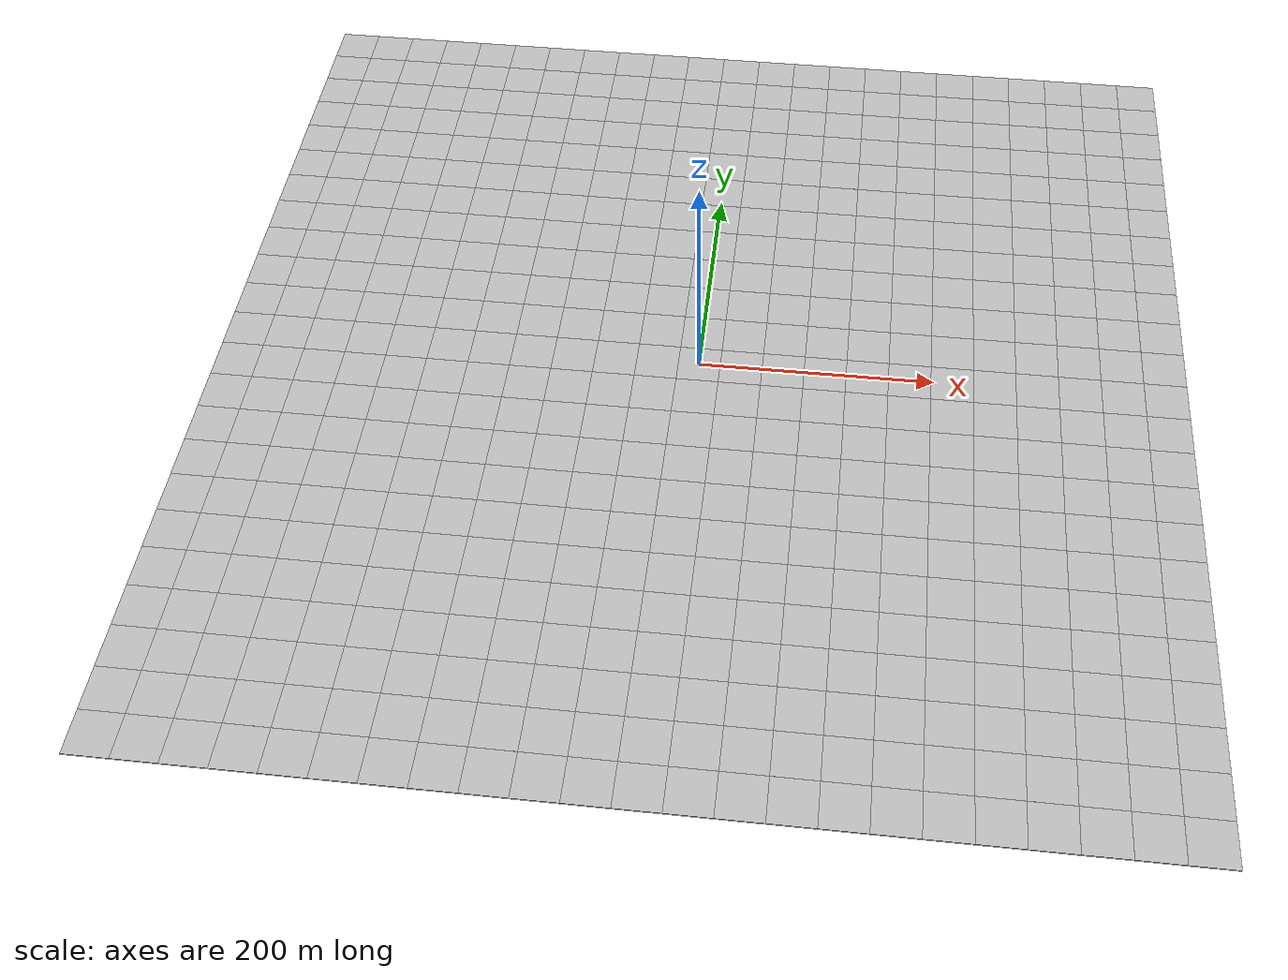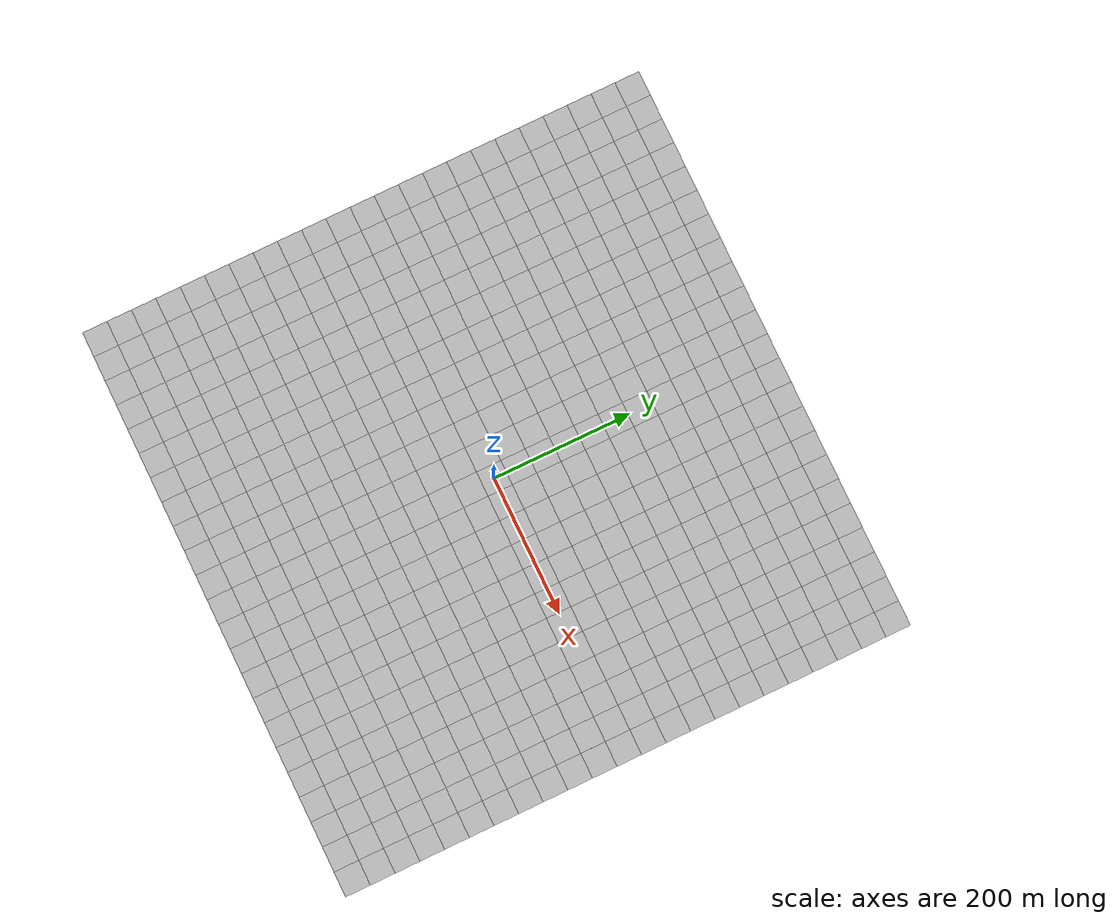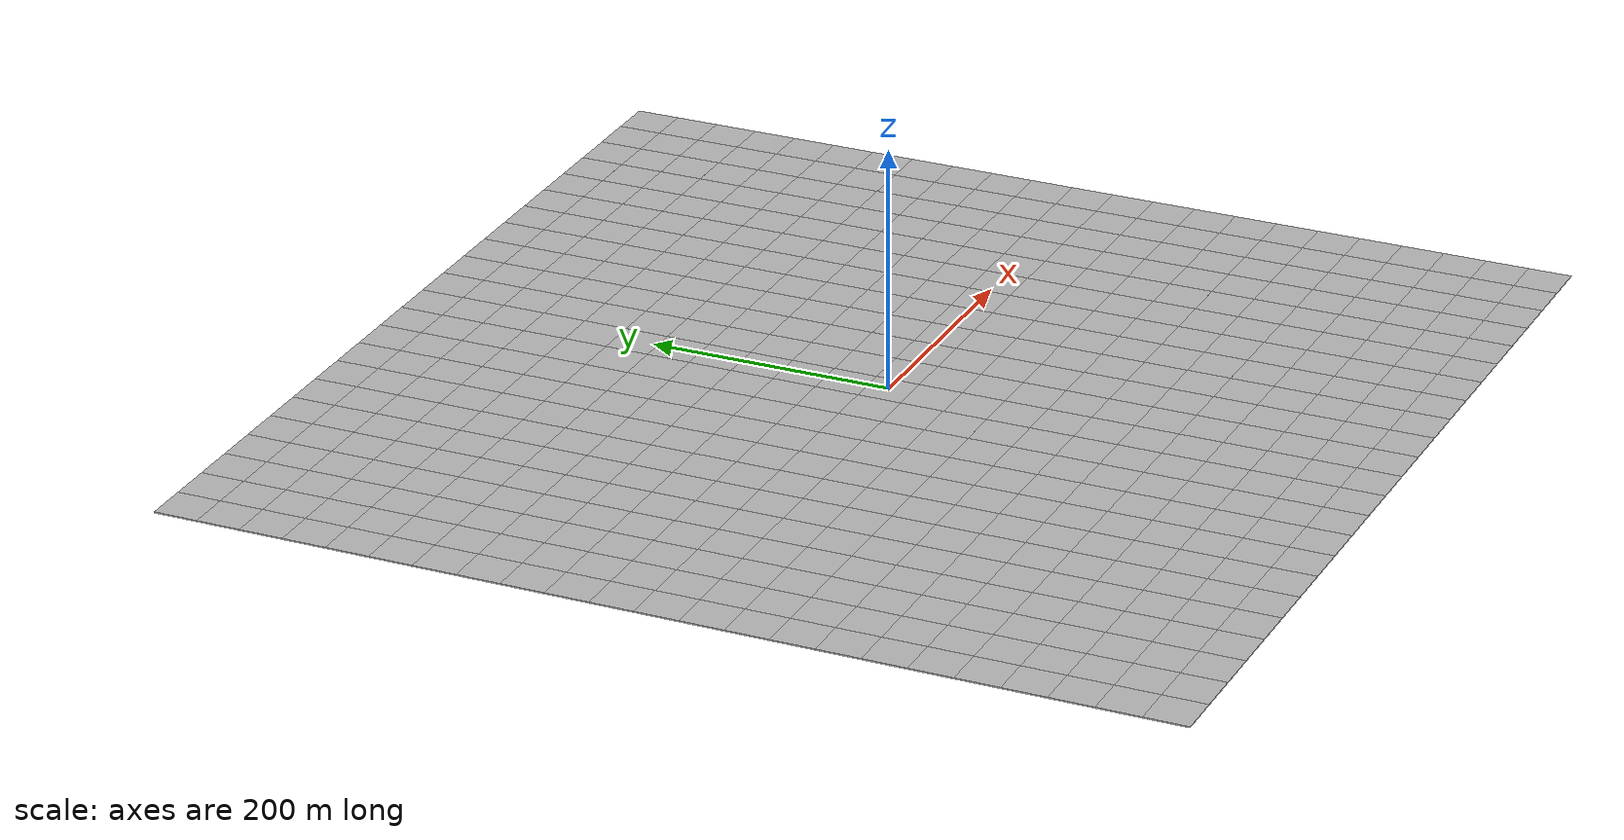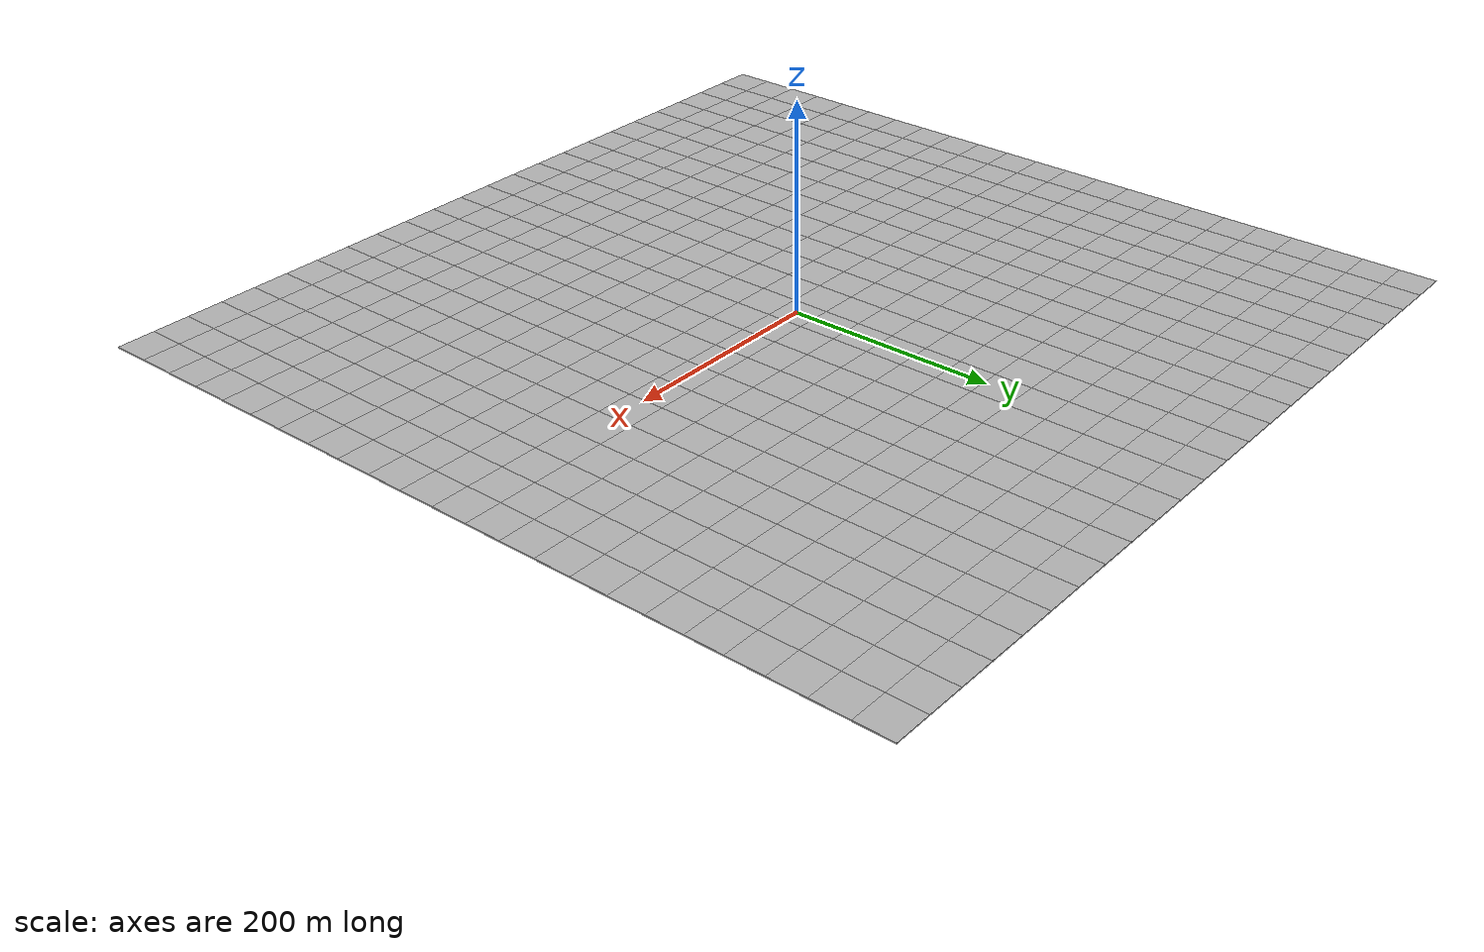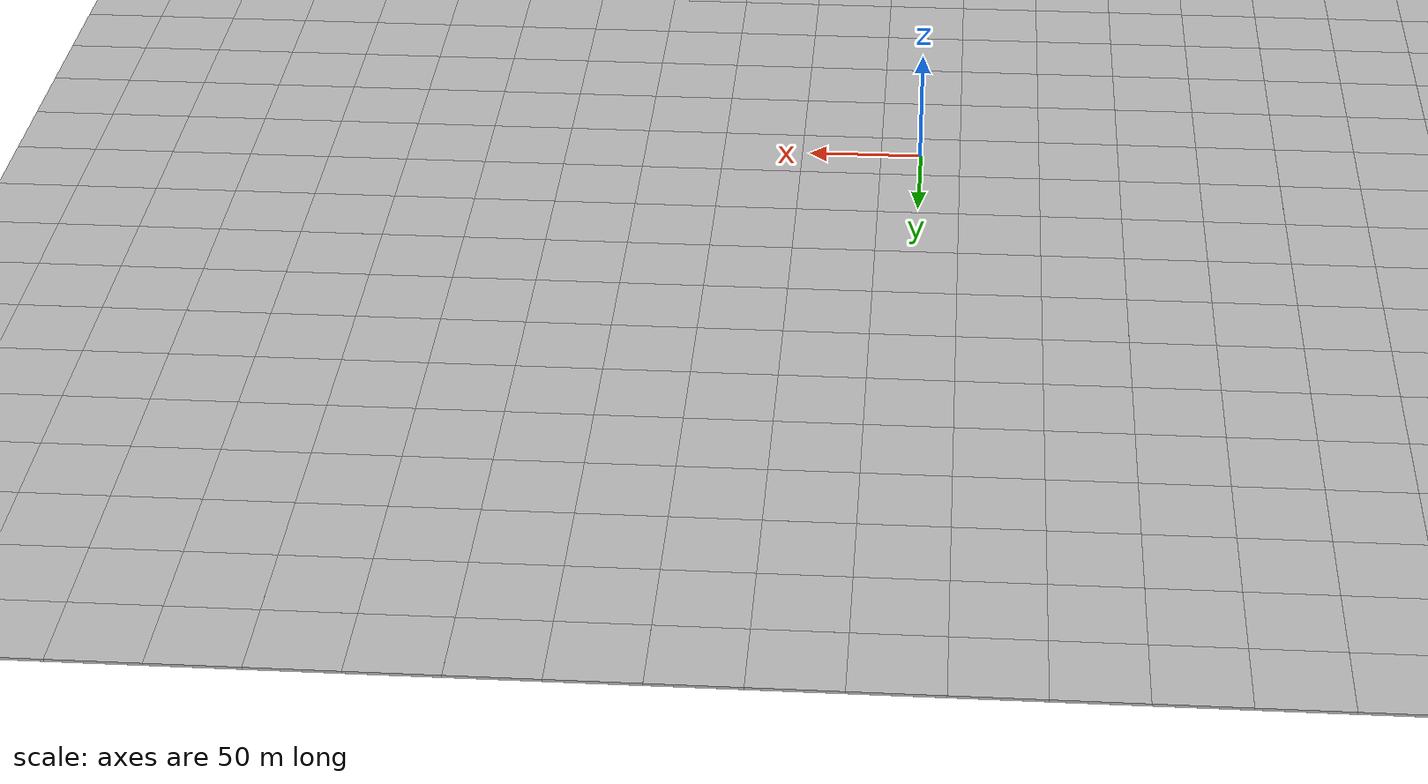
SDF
<sdf version='1.7'>
<model name='map_satellite_41.372171_-72.09904_800_800'>
  <static>true</static>
  <link name='link'>
    <collision name='collision'>
      <pose>0 0 -0.5 0 0 0</pose>
      <geometry>
        <box>
          <size>824.562 824.562 1</size>
        </box>
      </geometry>
    </collision>
    <visual name='visual0_0'>
      <pose>-394.356 394.356 -0.5 0 0 1.5708</pose>
      <geometry>
        <box>
          <size>35.8505 35.8505 1</size>
        </box>
      </geometry>
      <material>
        <script>
          <uri>model://map_satellite_41.372171_-72.09904_800_800/materials/scripts</uri>
          <uri>model://map_satellite_41.372171_-72.09904_800_800/materials/textures</uri>
          <name>map_satellite_41.372171_-72.09904_800_800/0_0</name>
        </script>
      </material>
    </visual>
    <visual name='visual0_1'>
      <pose>-358.505 394.356 -0.5 0 0 1.5708</pose>
      <geometry>
        <box>
          <size>35.8505 35.8505 1</size>
        </box>
      </geometry>
      <material>
        <script>
          <uri>model://map_satellite_41.372171_-72.09904_800_800/materials/scripts</uri>
          <uri>model://map_satellite_41.372171_-72.09904_800_800/materials/textures</uri>
          <name>map_satellite_41.372171_-72.09904_800_800/0_1</name>
        </script>
      </material>
    </visual>
    <visual name='visual0_2'>
      <pose>-322.655 394.356 -0.5 0 0 1.5708</pose>
      <geometry>
        <box>
          <size>35.8505 35.8505 1</size>
        </box>
      </geometry>
      <material>
        <script>
          <uri>model://map_satellite_41.372171_-72.09904_800_800/materials/scripts</uri>
          <uri>model://map_satellite_41.372171_-72.09904_800_800/materials/textures</uri>
          <name>map_satellite_41.372171_-72.09904_800_800/0_2</name>
        </script>
      </material>
    </visual>
    <visual name='visual0_3'>
      <pose>-286.804 394.356 -0.5 0 0 1.5708</pose>
      <geometry>
        <box>
          <size>35.8505 35.8505 1</size>
        </box>
      </geometry>
      <material>
        <script>
          <uri>model://map_satellite_41.372171_-72.09904_800_800/materials/scripts</uri>
          <uri>model://map_satellite_41.372171_-72.09904_800_800/materials/textures</uri>
          <name>map_satellite_41.372171_-72.09904_800_800/0_3</name>
        </script>
      </material>
    </visual>
    <visual name='visual0_4'>
      <pose>-250.954 394.356 -0.5 0 0 1.5708</pose>
      <geometry>
        <box>
          <size>35.8505 35.8505 1</size>
        </box>
      </geometry>
      <material>
        <script>
          <uri>model://map_satellite_41.372171_-72.09904_800_800/materials/scripts</uri>
          <uri>model://map_satellite_41.372171_-72.09904_800_800/materials/textures</uri>
          <name>map_satellite_41.372171_-72.09904_800_800/0_4</name>
        </script>
      </material>
    </visual>
    <visual name='visual0_5'>
      <pose>-215.103 394.356 -0.5 0 0 1.5708</pose>
      <geometry>
        <box>
          <size>35.8505 35.8505 1</size>
        </box>
      </geometry>
      <material>
        <script>
          <uri>model://map_satellite_41.372171_-72.09904_800_800/materials/scripts</uri>
          <uri>model://map_satellite_41.372171_-72.09904_800_800/materials/textures</uri>
          <name>map_satellite_41.372171_-72.09904_800_800/0_5</name>
        </script>
      </material>
    </visual>
    <visual name='visual0_6'>
      <pose>-179.253 394.356 -0.5 0 0 1.5708</pose>
      <geometry>
        <box>
          <size>35.8505 35.8505 1</size>
        </box>
      </geometry>
      <material>
        <script>
          <uri>model://map_satellite_41.372171_-72.09904_800_800/materials/scripts</uri>
          <uri>model://map_satellite_41.372171_-72.09904_800_800/materials/textures</uri>
          <name>map_satellite_41.372171_-72.09904_800_800/0_6</name>
        </script>
      </material>
    </visual>
    <visual name='visual0_7'>
      <pose>-143.402 394.356 -0.5 0 0 1.5708</pose>
      <geometry>
        <box>
          <size>35.8505 35.8505 1</size>
        </box>
      </geometry>
      <material>
        <script>
          <uri>model://map_satellite_41.372171_-72.09904_800_800/materials/scripts</uri>
          <uri>model://map_satellite_41.372171_-72.09904_800_800/materials/textures</uri>
          <name>map_satellite_41.372171_-72.09904_800_800/0_7</name>
        </script>
      </material>
    </visual>
    <visual name='visual0_8'>
      <pose>-107.552 394.356 -0.5 0 0 1.5708</pose>
      <geometry>
        <box>
          <size>35.8505 35.8505 1</size>
        </box>
      </geometry>
      <material>
        <script>
          <uri>model://map_satellite_41.372171_-72.09904_800_800/materials/scripts</uri>
          <uri>model://map_satellite_41.372171_-72.09904_800_800/materials/textures</uri>
          <name>map_satellite_41.372171_-72.09904_800_800/0_8</name>
        </script>
      </material>
    </visual>
    <visual name='visual0_9'>
      <pose>-71.701 394.356 -0.5 0 0 1.5708</pose>
      <geometry>
        <box>
          <size>35.8505 35.8505 1</size>
        </box>
      </geometry>
      <material>
        <script>
          <uri>model://map_satellite_41.372171_-72.09904_800_800/materials/scripts</uri>
          <uri>model://map_satellite_41.372171_-72.09904_800_800/materials/textures</uri>
          <name>map_satellite_41.372171_-72.09904_800_800/0_9</name>
        </script>
      </material>
    </visual>
    <visual name='visual0_10'>
      <pose>-35.8505 394.356 -0.5 0 0 1.5708</pose>
      <geometry>
        <box>
          <size>35.8505 35.8505 1</size>
        </box>
      </geometry>
      <material>
        <script>
          <uri>model://map_satellite_41.372171_-72.09904_800_800/materials/scripts</uri>
          <uri>model://map_satellite_41.372171_-72.09904_800_800/materials/textures</uri>
          <name>map_satellite_41.372171_-72.09904_800_800/0_10</name>
        </script>
      </material>
    </visual>
    <visual name='visual0_11'>
      <pose>-1.42109e-14 394.356 -0.5 0 0 1.5708</pose>
      <geometry>
        <box>
          <size>35.8505 35.8505 1</size>
        </box>
      </geometry>
      <material>
        <script>
          <uri>model://map_satellite_41.372171_-72.09904_800_800/materials/scripts</uri>
          <uri>model://map_satellite_41.372171_-72.09904_800_800/materials/textures</uri>
          <name>map_satellite_41.372171_-72.09904_800_800/0_11</name>
        </script>
      </material>
    </visual>
    <visual name='visual0_12'>
      <pose>35.8505 394.356 -0.5 0 0 1.5708</pose>
      <geometry>
        <box>
          <size>35.8505 35.8505 1</size>
        </box>
      </geometry>
      <material>
        <script>
          <uri>model://map_satellite_41.372171_-72.09904_800_800/materials/scripts</uri>
          <uri>model://map_satellite_41.372171_-72.09904_800_800/materials/textures</uri>
          <name>map_satellite_41.372171_-72.09904_800_800/0_12</name>
        </script>
      </material>
    </visual>
    <visual name='visual0_13'>
      <pose>71.701 394.356 -0.5 0 0 1.5708</pose>
      <geometry>
        <box>
          <size>35.8505 35.8505 1</size>
        </box>
      </geometry>
      <material>
        <script>
          <uri>model://map_satellite_41.372171_-72.09904_800_800/materials/scripts</uri>
          <uri>model://map_satellite_41.372171_-72.09904_800_800/materials/textures</uri>
          <name>map_satellite_41.372171_-72.09904_800_800/0_13</name>
        </script>
      </material>
    </visual>
    <visual name='visual0_14'>
      <pose>107.552 394.356 -0.5 0 0 1.5708</pose>
      <geometry>
        <box>
          <size>35.8505 35.8505 1</size>
        </box>
      </geometry>
      <material>
        <script>
          <uri>model://map_satellite_41.372171_-72.09904_800_800/materials/scripts</uri>
          <uri>model://map_satellite_41.372171_-72.09904_800_800/materials/textures</uri>
          <name>map_satellite_41.372171_-72.09904_800_800/0_14</name>
        </script>
      </material>
    </visual>
    <visual name='visual0_15'>
      <pose>143.402 394.356 -0.5 0 0 1.5708</pose>
      <geometry>
        <box>
          <size>35.8505 35.8505 1</size>
        </box>
      </geometry>
      <material>
        <script>
          <uri>model://map_satellite_41.372171_-72.09904_800_800/materials/scripts</uri>
          <uri>model://map_satellite_41.372171_-72.09904_800_800/materials/textures</uri>
          <name>map_satellite_41.372171_-72.09904_800_800/0_15</name>
        </script>
      </material>
    </visual>
    <visual name='visual0_16'>
      <pose>179.253 394.356 -0.5 0 0 1.5708</pose>
      <geometry>
        <box>
          <size>35.8505 35.8505 1</size>
        </box>
      </geometry>
      <material>
        <script>
          <uri>model://map_satellite_41.372171_-72.09904_800_800/materials/scripts</uri>
          <uri>model://map_satellite_41.372171_-72.09904_800_800/materials/textures</uri>
          <name>map_satellite_41.372171_-72.09904_800_800/0_16</name>
        </script>
      </material>
    </visual>
    <visual name='visual0_17'>
      <pose>215.103 394.356 -0.5 0 0 1.5708</pose>
      <geometry>
        <box>
          <size>35.8505 35.8505 1</size>
        </box>
      </geometry>
      <material>
        <script>
          <uri>model://map_satellite_41.372171_-72.09904_800_800/materials/scripts</uri>
          <uri>model://map_satellite_41.372171_-72.09904_800_800/materials/textures</uri>
          <name>map_satellite_41.372171_-72.09904_800_800/0_17</name>
        </script>
      </material>
    </visual>
    <visual name='visual0_18'>
      <pose>250.954 394.356 -0.5 0 0 1.5708</pose>
      <geometry>
        <box>
          <size>35.8505 35.8505 1</size>
        </box>
      </geometry>
      <material>
        <script>
          <uri>model://map_satellite_41.372171_-72.09904_800_800/materials/scripts</uri>
          <uri>model://map_satellite_41.372171_-72.09904_800_800/materials/textures</uri>
          <name>map_satellite_41.372171_-72.09904_800_800/0_18</name>
        </script>
      </material>
    </visual>
    <visual name='visual0_19'>
      <pose>286.804 394.356 -0.5 0 0 1.5708</pose>
      <geometry>
        <box>
          <size>35.8505 35.8505 1</size>
        </box>
      </geometry>
      <material>
        <script>
          <uri>model://map_satellite_41.372171_-72.09904_800_800/materials/scripts</uri>
          <uri>model://map_satellite_41.372171_-72.09904_800_800/materials/textures</uri>
          <name>map_satellite_41.372171_-72.09904_800_800/0_19</name>
        </script>
      </material>
    </visual>
    <visual name='visual0_20'>
      <pose>322.655 394.356 -0.5 0 0 1.5708</pose>
      <geometry>
        <box>
          <size>35.8505 35.8505 1</size>
        </box>
      </geometry>
      <material>
        <script>
          <uri>model://map_satellite_41.372171_-72.09904_800_800/materials/scripts</uri>
          <uri>model://map_satellite_41.372171_-72.09904_800_800/materials/textures</uri>
          <name>map_satellite_41.372171_-72.09904_800_800/0_20</name>
        </script>
      </material>
    </visual>
    <visual name='visual0_21'>
      <pose>358.505 394.356 -0.5 0 0 1.5708</pose>
      <geometry>
        <box>
          <size>35.8505 35.8505 1</size>
        </box>
      </geometry>
      <material>
        <script>
          <uri>model://map_satellite_41.372171_-72.09904_800_800/materials/scripts</uri>
          <uri>model://map_satellite_41.372171_-72.09904_800_800/materials/textures</uri>
          <name>map_satellite_41.372171_-72.09904_800_800/0_21</name>
        </script>
      </material>
    </visual>
    <visual name='visual0_22'>
      <pose>394.356 394.356 -0.5 0 0 1.5708</pose>
      <geometry>
        <box>
          <size>35.8505 35.8505 1</size>
        </box>
      </geometry>
      <material>
        <script>
          <uri>model://map_satellite_41.372171_-72.09904_800_800/materials/scripts</uri>
          <uri>model://map_satellite_41.372171_-72.09904_800_800/materials/textures</uri>
          <name>map_satellite_41.372171_-72.09904_800_800/0_22</name>
        </script>
      </material>
    </visual>
    <visual name='visual1_0'>
      <pose>-394.356 358.505 -0.5 0 0 1.5708</pose>
      <geometry>
        <box>
          <size>35.8505 35.8505 1</size>
        </box>
      </geometry>
      <material>
        <script>
          <uri>model://map_satellite_41.372171_-72.09904_800_800/materials/scripts</uri>
          <uri>model://map_satellite_41.372171_-72.09904_800_800/materials/textures</uri>
          <name>map_satellite_41.372171_-72.09904_800_800/1_0</name>
        </script>
      </material>
    </visual>
    <visual name='visual1_1'>
      <pose>-358.505 358.505 -0.5 0 0 1.5708</pose>
      <geometry>
        <box>
          <size>35.8505 35.8505 1</size>
        </box>
      </geometry>
      <material>
        <script>
          <uri>model://map_satellite_41.372171_-72.09904_800_800/materials/scripts</uri>
          <uri>model://map_satellite_41.372171_-72.09904_800_800/materials/textures</uri>
          <name>map_satellite_41.372171_-72.09904_800_800/1_1</name>
        </script>
      </material>
    </visual>
    <visual name='visual1_2'>
      <pose>-322.655 358.505 -0.5 0 0 1.5708</pose>
      <geometry>
        <box>
          <size>35.8505 35.8505 1</size>
        </box>
      </geometry>
      <material>
        <script>
          <uri>model://map_satellite_41.372171_-72.09904_800_800/materials/scripts</uri>
          <uri>model://map_satellite_41.372171_-72.09904_800_800/materials/textures</uri>
          <name>map_satellite_41.372171_-72.09904_800_800/1_2</name>
        </script>
      </material>
    </visual>
    <visual name='visual1_3'>
      <pose>-286.804 358.505 -0.5 0 0 1.5708</pose>
      <geometry>
        <box>
          <size>35.8505 35.8505 1</size>
        </box>
      </geometry>
      <material>
        <script>
          <uri>model://map_satellite_41.372171_-72.09904_800_800/materials/scripts</uri>
          <uri>model://map_satellite_41.372171_-72.09904_800_800/materials/textures</uri>
          <name>map_satellite_41.372171_-72.09904_800_800/1_3</name>
        </script>
      </material>
    </visual>
    <visual name='visual1_4'>
      <pose>-250.954 358.505 -0.5 0 0 1.5708</pose>
      <geometry>
        <box>
          <size>35.8505 35.8505 1</size>
        </box>
      </geometry>
      <material>
        <script>
          <uri>model://map_satellite_41.372171_-72.09904_800_800/materials/scripts</uri>
          <uri>model://map_satellite_41.372171_-72.09904_800_800/materials/textures</uri>
          <name>map_satellite_41.372171_-72.09904_800_800/1_4</name>
        </script>
      </material>
    </visual>
    <visual name='visual1_5'>
      <pose>-215.103 358.505 -0.5 0 0 1.5708</pose>
      <geometry>
        <box>
          <size>35.8505 35.8505 1</size>
        </box>
      </geometry>
      <material>
        <script>
          <uri>model://map_satellite_41.372171_-72.09904_800_800/materials/scripts</uri>
          <uri>model://map_satellite_41.372171_-72.09904_800_800/materials/textures</uri>
          <name>map_satellite_41.372171_-72.09904_800_800/1_5</name>
        </script>
      </material>
    </visual>
    <visual name='visual1_6'>
      <pose>-179.253 358.505 -0.5 0 0 1.5708</pose>
      <geometry>
        <box>
          <size>35.8505 35.8505 1</size>
        </box>
      </geometry>
      <material>
        <script>
          <uri>model://map_satellite_41.372171_-72.09904_800_800/materials/scripts</uri>
          <uri>model://map_satellite_41.372171_-72.09904_800_800/materials/textures</uri>
          <name>map_satellite_41.372171_-72.09904_800_800/1_6</name>
        </script>
      </material>
    </visual>
    <visual name='visual1_7'>
      <pose>-143.402 358.505 -0.5 0 0 1.5708</pose>
      <geometry>
        <box>
          <size>35.8505 35.8505 1</size>
        </box>
      </geometry>
      <material>
        <script>
          <uri>model://map_satellite_41.372171_-72.09904_800_800/materials/scripts</uri>
          <uri>model://map_satellite_41.372171_-72.09904_800_800/materials/textures</uri>
          <name>map_satellite_41.372171_-72.09904_800_800/1_7</name>
        </script>
      </material>
    </visual>
    <visual name='visual1_8'>
      <pose>-107.552 358.505 -0.5 0 0 1.5708</pose>
      <geometry>
        <box>
          <size>35.8505 35.8505 1</size>
        </box>
      </geometry>
      <material>
        <script>
          <uri>model://map_satellite_41.372171_-72.09904_800_800/materials/scripts</uri>
          <uri>model://map_satellite_41.372171_-72.09904_800_800/materials/textures</uri>
          <name>map_satellite_41.372171_-72.09904_800_800/1_8</name>
        </script>
      </material>
    </visual>
    <visual name='visual1_9'>
      <pose>-71.701 358.505 -0.5 0 0 1.5708</pose>
      <geometry>
        <box>
          <size>35.8505 35.8505 1</size>
        </box>
      </geometry>
      <material>
        <script>
          <uri>model://map_satellite_41.372171_-72.09904_800_800/materials/scripts</uri>
          <uri>model://map_satellite_41.372171_-72.09904_800_800/materials/textures</uri>
          <name>map_satellite_41.372171_-72.09904_800_800/1_9</name>
        </script>
      </material>
    </visual>
    <visual name='visual1_10'>
      <pose>-35.8505 358.505 -0.5 0 0 1.5708</pose>
      <geometry>
        <box>
          <size>35.8505 35.8505 1</size>
        </box>
      </geometry>
      <material>
        <script>
          <uri>model://map_satellite_41.372171_-72.09904_800_800/materials/scripts</uri>
          <uri>model://map_satellite_41.372171_-72.09904_800_800/materials/textures</uri>
          <name>map_satellite_41.372171_-72.09904_800_800/1_10</name>
        </script>
      </material>
    </visual>
    <visual name='visual1_11'>
      <pose>-1.42109e-14 358.505 -0.5 0 0 1.5708</pose>
      <geometry>
        <box>
          <size>35.8505 35.8505 1</size>
        </box>
      </geometry>
      <material>
        <script>
          <uri>model://map_satellite_41.372171_-72.09904_800_800/materials/scripts</uri>
          <uri>model://map_satellite_41.372171_-72.09904_800_800/materials/textures</uri>
          <name>map_satellite_41.372171_-72.09904_800_800/1_11</name>
        </script>
      </material>
    </visual>
    <visual name='visual1_12'>
      <pose>35.8505 358.505 -0.5 0 0 1.5708</pose>
      <geometry>
        <box>
          <size>35.8505 35.8505 1</size>
        </box>
      </geometry>
      <material>
        <script>
          <uri>model://map_satellite_41.372171_-72.09904_800_800/materials/scripts</uri>
          <uri>model://map_satellite_41.372171_-72.09904_800_800/materials/textures</uri>
          <name>map_satellite_41.372171_-72.09904_800_800/1_12</name>
        </script>
      </material>
    </visual>
    <visual name='visual1_13'>
      <pose>71.701 358.505 -0.5 0 0 1.5708</pose>
      <geometry>
        <box>
          <size>35.8505 35.8505 1</size>
        </box>
      </geometry>
      <material>
        <script>
          <uri>model://map_satellite_41.372171_-72.09904_800_800/materials/scripts</uri>
          <uri>model://map_satellite_41.372171_-72.09904_800_800/materials/textures</uri>
          <name>map_satellite_41.372171_-72.09904_800_800/1_13</name>
        </script>
      </material>
    </visual>
    <visual name='visual1_14'>
      <pose>107.552 358.505 -0.5 0 0 1.5708</pose>
      <geometry>
        <box>
          <size>35.8505 35.8505 1</size>
        </box>
      </geometry>
      <material>
        <script>
          <uri>model://map_satellite_41.372171_-72.09904_800_800/materials/scripts</uri>
          <uri>model://map_satellite_41.372171_-72.09904_800_800/materials/textures</uri>
          <name>map_satellite_41.372171_-72.09904_800_800/1_14</name>
        </script>
      </material>
    </visual>
    <visual name='visual1_15'>
      <pose>143.402 358.505 -0.5 0 0 1.5708</pose>
      <geometry>
        <box>
          <size>35.8505 35.8505 1</size>
        </box>
      </geometry>
      <material>
        <script>
          <uri>model://map_satellite_41.372171_-72.09904_800_800/materials/scripts</uri>
          <uri>model://map_satellite_41.372171_-72.09904_800_800/materials/textures</uri>
          <name>map_satellite_41.372171_-72.09904_800_800/1_15</name>
        </script>
      </material>
    </visual>
    <visual name='visual1_16'>
      <pose>179.253 358.505 -0.5 0 0 1.5708</pose>
      <geometry>
        <box>
          <size>35.8505 35.8505 1</size>
        </box>
      </geometry>
      <material>
        <script>
          <uri>model://map_satellite_41.372171_-72.09904_800_800/materials/scripts</uri>
          <uri>model://map_satellite_41.372171_-72.09904_800_800/materials/textures</uri>
          <name>map_satellite_41.372171_-72.09904_800_800/1_16</name>
        </script>
      </material>
    </visual>
    <visual name='visual1_17'>
      <pose>215.103 358.505 -0.5 0 0 1.5708</pose>
      <geometry>
        <box>
          <size>35.8505 35.8505 1</size>
        </box>
      </geometry>
      <material>
        <script>
          <uri>model://map_satellite_41.372171_-72.09904_800_800/materials/scripts</uri>
          <uri>model://map_satellite_41.372171_-72.09904_800_800/materials/textures</uri>
          <name>map_satellite_41.372171_-72.09904_800_800/1_17</name>
        </script>
      </material>
    </visual>
    <visual name='visual1_18'>
      <pose>250.954 358.505 -0.5 0 0 1.5708</pose>
      <geometry>
        <box>
          <size>35.8505 35.8505 1</size>
        </box>
      </geometry>
      <material>
        <script>
          <uri>model://map_satellite_41.372171_-72.09904_800_800/materials/scripts</uri>
          <uri>model://map_satellite_41.372171_-72.09904_800_800/materials/textures</uri>
          <name>map_satellite_41.372171_-72.09904_800_800/1_18</name>
        </script>
      </material>
    </visual>
    <visual name='visual1_19'>
      <pose>286.804 358.505 -0.5 0 0 1.5708</pose>
      <geometry>
        <box>
          <size>35.8505 35.8505 1</size>
        </box>
      </geometry>
      <material>
        <script>
          <uri>model://map_satellite_41.372171_-72.09904_800_800/materials/scripts</uri>
          <uri>model://map_satellite_41.372171_-72.09904_800_800/materials/textures</uri>
          <name>map_satellite_41.372171_-72.09904_800_800/1_19</name>
        </script>
      </material>
    </visual>
    <visual name='visual1_20'>
      <pose>322.655 358.505 -0.5 0 0 1.5708</pose>
      <geometry>
        <box>
          <size>35.8505 35.8505 1</size>
        </box>
      </geometry>
      <material>
        <script>
          <uri>model://map_satellite_41.372171_-72.09904_800_800/materials/scripts</uri>
          <uri>model://map_satellite_41.372171_-72.09904_800_800/materials/textures</uri>
          <name>map_satellite_41.372171_-72.09904_800_800/1_20</name>
        </script>
      </material>
    </visual>
    <visual name='visual1_21'>
      <pose>358.505 358.505 -0.5 0 0 1.5708</pose>
      <geometry>
        <box>
          <size>35.8505 35.8505 1</size>
        </box>
      </geometry>
      <material>
        <script>
          <uri>model://map_satellite_41.372171_-72.09904_800_800/materials/scripts</uri>
          <uri>model://map_satellite_41.372171_-72.09904_800_800/materials/textures</uri>
          <name>map_satellite_41.372171_-72.09904_800_800/1_21</name>
        </script>
      </material>
    </visual>
    <visual name='visual1_22'>
      <pose>394.356 358.505 -0.5 0 0 1.5708</pose>
      <geometry>
        <box>
          <size>35.8505 35.8505 1</size>
        </box>
      </geometry>
      <material>
        <script>
          <uri>model://map_satellite_41.372171_-72.09904_800_800/materials/scripts</uri>
          <uri>model://map_satellite_41.372171_-72.09904_800_800/materials/textures</uri>
          <name>map_satellite_41.372171_-72.09904_800_800/1_22</name>
        </script>
      </material>
    </visual>
    <visual name='visual2_0'>
      <pose>-394.356 322.655 -0.5 0 0 1.5708</pose>
      <geometry>
        <box>
          <size>35.8505 35.8505 1</size>
        </box>
      </geometry>
      <material>
        <script>
          <uri>model://map_satellite_41.372171_-72.09904_800_800/materials/scripts</uri>
          <uri>model://map_satellite_41.372171_-72.09904_800_800/materials/textures</uri>
          <name>map_satellite_41.372171_-72.09904_800_800/2_0</name>
        </script>
      </material>
    </visual>
    <visual name='visual2_1'>
      <pose>-358.505 322.655 -0.5 0 0 1.5708</pose>
      <geometry>
        <box>
          <size>35.8505 35.8505 1</size>
        </box>
      </geometry>
      <material>
        <script>
          <uri>model://map_satellite_41.372171_-72.09904_800_800/materials/scripts</uri>
          <uri>model://map_satellite_41.372171_-72.09904_800_800/materials/textures</uri>
          <name>map_satellite_41.372171_-72.09904_800_800/2_1</name>
        </script>
      </material>
    </visual>
    <visual name='visual2_2'>
      <pose>-322.655 322.655 -0.5 0 0 1.5708</pose>
      <geometry>
        <box>
          <size>35.8505 35.8505 1</size>
        </box>
      </geometry>
      <material>
        <script>
          <uri>model://map_satellite_41.372171_-72.09904_800_800/materials/scripts</uri>
          <uri>model://map_satellite_41.372171_-72.09904_800_800/materials/textures</uri>
          <name>map_satellite_41.372171_-72.09904_800_800/2_2</name>
        </script>
      </material>
    </visual>
    <visual name='visual2_3'>
      <pose>-286.804 322.655 -0.5 0 0 1.5708</pose>
      <geometry>
        <box>
          <size>35.8505 35.8505 1</size>
        </box>
      </geometry>
      <material>
        <script>
          <uri>model://map_satellite_41.372171_-72.09904_800_800/materials/scripts</uri>
          <uri>model://map_satellite_41.372171_-72.09904_800_800/materials/textures</uri>
          <name>map_satellite_41.372171_-72.09904_800_800/2_3</name>
        </script>
      </material>
    </visual>
    <visual name='visual2_4'>
      <pose>-250.954 322.655 -0.5 0 0 1.5708</pose>
      <geometry>
        <box>
          <size>35.8505 35.8505 1</size>
        </box>
      </geometry>
      <material>
        <script>
          <uri>model://map_satellite_41.372171_-72.09904_800_800/materials/scripts</uri>
          <uri>model://map_satellite_41.372171_-72.09904_800_800/materials/textures</uri>
          <name>map_satellite_41.372171_-72.09904_800_800/2_4</name>
        </script>
      </material>
    </visual>
    <visual name='visual2_5'>
      <pose>-215.103 322.655 -0.5 0 0 1.5708</pose>
      <geometry>
        <box>
          <size>35.8505 35.8505 1</size>
        </box>
      </geometry>
      <material>
        <script>
          <uri>model://map_satellite_41.372171_-72.09904_800_800/materials/scripts</uri>
          <uri>model://map_satellite_41.372171_-72.09904_800_800/materials/textures</uri>
          <name>map_satellite_41.372171_-72.09904_800_800/2_5</name>
        </script>
      </material>
    </visual>
    <visual name='visual2_6'>
      <pose>-179.253 322.655 -0.5 0 0 1.5708</pose>
      <geometry>
        <box>
          <size>35.8505 35.8505 1</size>
        </box>
      </geometry>
      <material>
        <script>
          <uri>model://map_satellite_41.372171_-72.09904_800_800/materials/scripts</uri>
          <uri>model://map_satellite_41.372171_-72.09904_800_800/materials/textures</uri>
          <name>map_satellite_41.372171_-72.09904_800_800/2_6</name>
        </script>
      </material>
    </visual>
    <visual name='visual2_7'>
      <pose>-143.402 322.655 -0.5 0 0 1.5708</pose>
      <geometry>
        <box>
          <size>35.8505 35.8505 1</size>
        </box>
      </geometry>
      <material>
        <script>
          <uri>model://map_satellite_41.372171_-72.09904_800_800/materials/scripts</uri>
          <uri>model://map_satellite_41.372171_-72.09904_800_800/materials/textures</uri>
          <name>map_satellite_41.372171_-72.09904_800_800/2_7</name>
        </script>
      </material>
    </visual>
    <visual name='visual2_8'>
      <pose>-107.552 322.655 -0.5 0 0 1.5708</pose>
      <geometry>
        <box>
          <size>35.8505 35.8505 1</size>
        </box>
      </geometry>
      <material>
        <script>
          <uri>model://map_satellite_41.372171_-72.09904_800_800/materials/scripts</uri>
          <uri>model://map_satellite_41.372171_-72.09904_800_800/materials/textures</uri>
          <name>map_satellite_41.372171_-72.09904_800_800/2_8</name>
        </script>
      </material>
    </visual>
    <visual name='visual2_9'>
      <pose>-71.701 322.655 -0.5 0 0 1.5708</pose>
      <geometry>
        <box>
          <size>35.8505 35.8505 1</size>
        </box>
      </geometry>
      <material>
        <script>
          <uri>model://map_satellite_41.372171_-72.09904_800_800/materials/scripts</uri>
          <uri>model://map_satellite_41.372171_-72.09904_800_800/materials/textures</uri>
          <name>map_satellite_41.372171_-72.09904_800_800/2_9</name>
        </script>
      </material>
    </visual>
    <visual name='visual2_10'>
      <pose>-35.8505 322.655 -0.5 0 0 1.5708</pose>
      <geometry>
        <box>
          <size>35.8505 35.8505 1</size>
        </box>
      </geometry>
      <material>
        <script>
          <uri>model://map_satellite_41.372171_-72.09904_800_800/materials/scripts</uri>
          <uri>model://map_satellite_41.372171_-72.09904_800_800/materials/textures</uri>
          <name>map_satellite_41.372171_-72.09904_800_800/2_10</name>
        </script>
      </material>
    </visual>
    <visual name='visual2_11'>
      <pose>-1.42109e-14 322.655 -0.5 0 0 1.5708</pose>
      <geometry>
        <box>
          <size>35.8505 35.8505 1</size>
        </box>
      </geometry>
      <material>
        <script>
          <uri>model://map_satellite_41.372171_-72.09904_800_800/materials/scripts</uri>
          <uri>model://map_satellite_41.372171_-72.09904_800_800/materials/textures</uri>
          <name>map_satellite_41.372171_-72.09904_800_800/2_11</name>
        </script>
      </material>
    </visual>
    <visual name='visual2_12'>
      <pose>35.8505 322.655 -0.5 0 0 1.5708</pose>
      <geometry>
        <box>
          <size>35.8505 35.8505 1</size>
        </box>
      </geometry>
      <material>
        <script>
          <uri>model://map_satellite_41.372171_-72.09904_800_800/materials/scripts</uri>
          <uri>model://map_satellite_41.372171_-72.09904_800_800/materials/textures</uri>
          <name>map_satellite_41.372171_-72.09904_800_800/2_12</name>
        </script>
      </material>
    </visual>
    <visual name='visual2_13'>
      <pose>71.701 322.655 -0.5 0 0 1.5708</pose>
      <geometry>
        <box>
          <size>35.8505 35.8505 1</size>
        </box>
      </geometry>
      <material>
        <script>
          <uri>model://map_satellite_41.372171_-72.09904_800_800/materials/scripts</uri>
          <uri>model://map_satellite_41.372171_-72.09904_800_800/materials/textures</uri>
          <name>map_satellite_41.372171_-72.09904_800_800/2_13</name>
        </script>
      </material>
    </visual>
    <visual name='visual2_14'>
      <pose>107.552 322.655 -0.5 0 0 1.5708</pose>
      <geometry>
        <box>
          <size>35.8505 35.8505 1</size>
        </box>
      </geometry>
      <material>
        <script>
          <uri>model://map_satellite_41.372171_-72.09904_800_800/materials/scripts</uri>
          <uri>model://map_satellite_41.372171_-72.09904_800_800/materials/textures</uri>
          <name>map_satellite_41.372171_-72.09904_800_800/2_14</name>
        </script>
      </material>
    </visual>
    <visual name='visual2_15'>
      <pose>143.402 322.655 -0.5 0 0 1.5708</pose>
      <geometry>
        <box>
          <size>35.8505 35.8505 1</size>
        </box>
      </geometry>
      <material>
        <script>
          <uri>model://map_satellite_41.372171_-72.09904_800_800/materials/scripts</uri>
          <uri>model://map_satellite_41.372171_-72.09904_800_800/materials/textures</uri>
          <name>map_satellite_41.372171_-72.09904_800_800/2_15</name>
        </script>
      </material>
    </visual>
    <visual name='visual2_16'>
      <pose>179.253 322.655 -0.5 0 0 1.5708</pose>
      <geometry>
        <box>
          <size>35.8505 35.8505 1</size>
        </box>
      </geometry>
      <material>
        <script>
          <uri>model://map_satellite_41.372171_-72.09904_800_800/materials/scripts</uri>
          <uri>model://map_satellite_41.372171_-72.09904_800_800/materials/textures</uri>
          <name>map_satellite_41.372171_-72.09904_800_800/2_16</name>
        </script>
      </material>
    </visual>
    <visual name='visual2_17'>
      <pose>215.103 322.655 -0.5 0 0 1.5708</pose>
      <geometry>
        <box>
          <size>35.8505 35.8505 1</size>
        </box>
      </geometry>
      <material>
        <script>
          <uri>model://map_satellite_41.372171_-72.09904_800_800/materials/scripts</uri>
          <uri>model://map_satellite_41.372171_-72.09904_800_800/materials/textures</uri>
          <name>map_satellite_41.372171_-72.09904_800_800/2_17</name>
        </script>
      </material>
    </visual>
    <visual name='visual2_18'>
      <pose>250.954 322.655 -0.5 0 0 1.5708</pose>
      <geometry>
        <box>
          <size>35.8505 35.8505 1</size>
        </box>
      </geometry>
      <material>
        <script>
          <uri>model://map_satellite_41.372171_-72.09904_800_800/materials/scripts</uri>
          <uri>model://map_satellite_41.372171_-72.09904_800_800/materials/textures</uri>
          <name>map_satellite_41.372171_-72.09904_800_800/2_18</name>
        </script>
      </material>
    </visual>
    <visual name='visual2_19'>
      <pose>286.804 322.655 -0.5 0 0 1.5708</pose>
      <geometry>
        <box>
          <size>35.8505 35.8505 1</size>
        </box>
      </geometry>
      <material>
        <script>
          <uri>model://map_satellite_41.372171_-72.09904_800_800/materials/scripts</uri>
          <uri>model://map_satellite_41.372171_-72.09904_800_800/materials/textures</uri>
          <name>map_satellite_41.372171_-72.09904_800_800/2_19</name>
        </script>
      </material>
    </visual>
    <visual name='visual2_20'>
      <pose>322.655 322.655 -0.5 0 0 1.5708</pose>
      <geometry>
        <box>
          <size>35.8505 35.8505 1</size>
        </box>
      </geometry>
      <material>
        <script>
          <uri>model://map_satellite_41.372171_-72.09904_800_800/materials/scripts</uri>
          <uri>model://map_satellite_41.372171_-72.09904_800_800/materials/textures</uri>
          <name>map_satellite_41.372171_-72.09904_800_800/2_20</name>
        </script>
      </material>
    </visual>
    <visual name='visual2_21'>
      <pose>358.505 322.655 -0.5 0 0 1.5708</pose>
      <geometry>
        <box>
          <size>35.8505 35.8505 1</size>
        </box>
      </geometry>
      <material>
        <script>
          <uri>model://map_satellite_41.372171_-72.09904_800_800/materials/scripts</uri>
          <uri>model://map_satellite_41.372171_-72.09904_800_800/materials/textures</uri>
          <name>map_satellite_41.372171_-72.09904_800_800/2_21</name>
        </script>
      </material>
    </visual>
    <visual name='visual2_22'>
      <pose>394.356 322.655 -0.5 0 0 1.5708</pose>
      <geometry>
        <box>
          <size>35.8505 35.8505 1</size>
        </box>
      </geometry>
      <material>
        <script>
          <uri>model://map_satellite_41.372171_-72.09904_800_800/materials/scripts</uri>
          <uri>model://map_satellite_41.372171_-72.09904_800_800/materials/textures</uri>
          <name>map_satellite_41.372171_-72.09904_800_800/2_22</name>
        </script>
      </material>
    </visual>
    <visual name='visual3_0'>
      <pose>-394.356 286.804 -0.5 0 0 1.5708</pose>
      <geometry>
        <box>
          <size>35.8505 35.8505 1</size>
        </box>
      </geometry>
      <material>
        <script>
          <uri>model://map_satellite_41.372171_-72.09904_800_800/materials/scripts</uri>
          <uri>model://map_satellite_41.372171_-72.09904_800_800/materials/textures</uri>
          <name>map_satellite_41.372171_-72.09904_800_800/3_0</name>
        </script>
      </material>
    </visual>
    <visual name='visual3_1'>
      <pose>-358.505 286.804 -0.5 0 0 1.5708</pose>
      <geometry>
        <box>
          <size>35.8505 35.8505 1</size>
        </box>
      </geometry>
      <material>
        <script>
          <uri>model://map_satellite_41.372171_-72.09904_800_800/materials/scripts</uri>
          <uri>model://map_satellite_41.372171_-72.09904_800_800/materials/textures</uri>
          <name>map_satellite_41.372171_-72.09904_800_800/3_1</name>
        </script>
      </material>
    </visual>
    <visual name='visual3_2'>
      <pose>-322.655 286.804 -0.5 0 0 1.5708</pose>
      <geometry>
        <box>
          <size>35.8505 35.8505 1</size>
        </box>
      </geometry>
      <material>
        <script>
          <uri>model://map_satellite_41.372171_-72.09904_800_800/materials/scripts</uri>
          <uri>model://map_satellite_41.372171_-72.09904_800_800/materials/textures</uri>
          <name>map_satellite_41.372171_-72.09904_800_800/3_2</name>
        </script>
      </material>
    </visual>
    <visual name='visual3_3'>
      <pose>-286.804 286.804 -0.5 0 0 1.5708</pose>
      <geometry>
        <box>
          <size>35.8505 35.8505 1</size>
        </box>
      </geometry>
      <material>
        <script>
          <uri>model://map_satellite_41.372171_-72.09904_800_800/materials/scripts</uri>
          <uri>model://map_satellite_41.372171_-72.09904_800_800/materials/textures</uri>
          <name>map_satellite_41.372171_-72.09904_800_800/3_3</name>
        </script>
      </material>
    </visual>
    <visual name='visual3_4'>
      <pose>-250.954 286.804 -0.5 0 0 1.5708</pose>
      <geometry>
        <box>
          <size>35.8505 35.8505 1</size>
        </box>
      </geometry>
      <material>
        <script>
          <uri>model://map_satellite_41.372171_-72.09904_800_800/materials/scripts</uri>
          <uri>model://map_satellite_41.372171_-72.09904_800_800/materials/textures</uri>
          <name>map_satellite_41.372171_-72.09904_800_800/3_4</name>
        </script>
      </material>
    </visual>
    <visual name='visual3_5'>
      <pose>-215.103 286.804 -0.5 0 0 1.5708</pose>
      <geometry>
        <box>
          <size>35.8505 35.8505 1</size>
        </box>
      </geometry>
      <material>
        <script>
          <uri>model://map_satellite_41.372171_-72.09904_800_800/materials/scripts</uri>
          <uri>model://map_satellite_41.372171_-72.09904_800_800/materials/textures</uri>
          <name>map_satellite_41.372171_-72.09904_800_800/3_5</name>
        </script>
      </material>
    </visual>
    <visual name='visual3_6'>
      <pose>-179.253 286.804 -0.5 0 0 1.5708</pose>
      <geometry>
        <box>
          <size>35.8505 35.8505 1</size>
        </box>
      </geometry>
      <material>
        <script>
          <uri>model://map_satellite_41.372171_-72.09904_800_800/materials/scripts</uri>
          <uri>model://map_satellite_41.372171_-72.09904_800_800/materials/textures</uri>
          <name>map_satellite_41.372171_-72.09904_800_800/3_6</name>
        </script>
      </material>
    </visual>
    <visual name='visual3_7'>
      <pose>-143.402 286.804 -0.5 0 0 1.5708</pose>
      <geometry>
        <box>
          <size>35.8505 35.8505 1</size>
        </box>
      </geometry>
      <material>
        <script>
          <uri>model://map_satellite_41.372171_-72.09904_800_800/materials/scripts</uri>
          <uri>model://map_satellite_41.372171_-72.09904_800_800/materials/textures</uri>
          <name>map_satellite_41.372171_-72.09904_800_800/3_7</name>
        </script>
      </material>
    </visual>
    <visual name='visual3_8'>
      <pose>-107.552 286.804 -0.5 0 0 1.5708</pose>
      <geometry>
        <box>
          <size>35.8505 35.8505 1</size>
        </box>
      </geometry>
      <material>
        <script>
          <uri>model://map_satellite_41.372171_-72.09904_800_800/materials/scripts</uri>
          <uri>model://map_satellite_41.372171_-72.09904_800_800/materials/textures</uri>
          <name>map_satellite_41.372171_-72.09904_800_800/3_8</name>
        </script>
      </material>
    </visual>
    <visual name='visual3_9'>
      <pose>-71.701 286.804 -0.5 0 0 1.5708</pose>
      <geometry>
        <box>
          <size>35.8505 35.8505 1</size>
        </box>
      </geometry>
      <material>
        <script>
          <uri>model://map_satellite_41.372171_-72.09904_800_800/materials/scripts</uri>
          <uri>model://map_satellite_41.372171_-72.09904_800_800/materials/textures</uri>
          <name>map_satellite_41.372171_-72.09904_800_800/3_9</name>
        </script>
      </material>
    </visual>
    <visual name='visual3_10'>
      <pose>-35.8505 286.804 -0.5 0 0 1.5708</pose>
      <geometry>
        <box>
          <size>35.8505 35.8505 1</size>
        </box>
      </geometry>
      <material>
        <script>
          <uri>model://map_satellite_41.372171_-72.09904_800_800/materials/scripts</uri>
          <uri>model://map_satellite_41.372171_-72.09904_800_800/materials/textures</uri>
          <name>map_satellite_41.372171_-72.09904_800_800/3_10</name>
        </script>
      </material>
    </visual>
    <visual name='visual3_11'>
      <pose>-1.42109e-14 286.804 -0.5 0 0 1.5708</pose>
      <geometry>
        <box>
          <size>35.8505 35.8505 1</size>
        </box>
      </geometry>
      <material>
        <script>
          <uri>model://map_satellite_41.372171_-72.09904_800_800/materials/scripts</uri>
          <uri>model://map_satellite_41.372171_-72.09904_800_800/materials/textures</uri>
          <name>map_satellite_41.372171_-72.09904_800_800/3_11</name>
        </script>
      </material>
    </visual>
    <visual name='visual3_12'>
      <pose>35.8505 286.804 -0.5 0 0 1.5708</pose>
      <geometry>
        <box>
          <size>35.8505 35.8505 1</size>
        </box>
      </geometry>
      <material>
        <script>
          <uri>model://map_satellite_41.372171_-72.09904_800_800/materials/scripts</uri>
          <uri>model://map_satellite_41.372171_-72.09904_800_800/materials/textures</uri>
          <name>map_satellite_41.372171_-72.09904_800_800/3_12</name>
        </script>
      </material>
    </visual>
    <visual name='visual3_13'>
      <pose>71.701 286.804 -0.5 0 0 1.5708</pose>
      <geometry>
        <box>
          <size>35.8505 35.8505 1</size>
        </box>
      </geometry>
      <material>
        <script>
          <uri>model://map_satellite_41.372171_-72.09904_800_800/materials/scripts</uri>
          <uri>model://map_satellite_41.372171_-72.09904_800_800/materials/textures</uri>
          <name>map_satellite_41.372171_-72.09904_800_800/3_13</name>
        </script>
      </material>
    </visual>
    <visual name='visual3_14'>
      <pose>107.552 286.804 -0.5 0 0 1.5708</pose>
      <geometry>
        <box>
          <size>35.8505 35.8505 1</size>
        </box>
      </geometry>
      <material>
        <script>
          <uri>model://map_satellite_41.372171_-72.09904_800_800/materials/scripts</uri>
          <uri>model://map_satellite_41.372171_-72.09904_800_800/materials/textures</uri>
          <name>map_satellite_41.372171_-72.09904_800_800/3_14</name>
        </script>
      </material>
    </visual>
    <visual name='visual3_15'>
      <pose>143.402 286.804 -0.5 0 0 1.5708</pose>
      <geometry>
        <box>
          <size>35.8505 35.8505 1</size>
        </box>
      </geometry>
      <material>
        <script>
          <uri>model://map_satellite_41.372171_-72.09904_800_800/materials/scripts</uri>
          <uri>model://map_satellite_41.372171_-72.09904_800_800/materials/textures</uri>
          <name>map_satellite_41.372171_-72.09904_800_800/3_15</name>
        </script>
      </material>
    </visual>
    <visual name='visual3_16'>
      <pose>179.253 286.804 -0.5 0 0 1.5708</pose>
      <geometry>
        <box>
          <size>35.8505 35.8505 1</size>
        </box>
      </geometry>
      <material>
        <script>
          <uri>model://map_satellite_41.372171_-72.09904_800_800/materials/scripts</uri>
          <uri>model://map_satellite_41.372171_-72.09904_800_800/materials/textures</uri>
          <name>map_satellite_41.372171_-72.09904_800_800/3_16</name>
        </script>
      </material>
    </visual>
    <visual name='visual3_17'>
      <pose>215.103 286.804 -0.5 0 0 1.5708</pose>
      <geometry>
        <box>
          <size>35.8505 35.8505 1</size>
        </box>
      </geometry>
      <material>
        <script>
          <uri>model://map_satellite_41.372171_-72.09904_800_800/materials/scripts</uri>
          <uri>model://map_satellite_41.372171_-72.09904_800_800/materials/textures</uri>
          <name>map_satellite_41.372171_-72.09904_800_800/3_17</name>
        </script>
      </material>
    </visual>
    <visual name='visual3_18'>
      <pose>250.954 286.804 -0.5 0 0 1.5708</pose>
      <geometry>
        <box>
          <size>35.8505 35.8505 1</size>
        </box>
      </geometry>
      <material>
        <script>
          <uri>model://map_satellite_41.372171_-72.09904_800_800/materials/scripts</uri>
          <uri>model://map_satellite_41.372171_-72.09904_800_800/materials/textures</uri>
          <name>map_satellite_41.372171_-72.09904_800_800/3_18</name>
        </script>
      </material>
    </visual>
    <visual name='visual3_19'>
      <pose>286.804 286.804 -0.5 0 0 1.5708</pose>
      <geometry>
        <box>
          <size>35.8505 35.8505 1</size>
        </box>
      </geometry>
      <material>
        <script>
          <uri>model://map_satellite_41.372171_-72.09904_800_800/materials/scripts</uri>
          <uri>model://map_satellite_41.372171_-72.09904_800_800/materials/textures</uri>
          <name>map_satellite_41.372171_-72.09904_800_800/3_19</name>
        </script>
      </material>
    </visual>
    <visual name='visual3_20'>
      <pose>322.655 286.804 -0.5 0 0 1.5708</pose>
      <geometry>
        <box>
          <size>35.8505 35.8505 1</size>
        </box>
      </geometry>
      <material>
        <script>
          <uri>model://map_satellite_41.372171_-72.09904_800_800/materials/scripts</uri>
          <uri>model://map_satellite_41.372171_-72.09904_800_800/materials/textures</uri>
          <name>map_satellite_41.372171_-72.09904_800_800/3_20</name>
        </script>
      </material>
    </visual>
    <visual name='visual3_21'>
      <pose>358.505 286.804 -0.5 0 0 1.5708</pose>
      <geometry>
        <box>
          <size>35.8505 35.8505 1</size>
        </box>
      </geometry>
      <material>
        <script>
          <uri>model://map_satellite_41.372171_-72.09904_800_800/materials/scripts</uri>
          <uri>model://map_satellite_41.372171_-72.09904_800_800/materials/textures</uri>
          <name>map_satellite_41.372171_-72.09904_800_800/3_21</name>
        </script>
      </material>
    </visual>
    <visual name='visual3_22'>
      <pose>394.356 286.804 -0.5 0 0 1.5708</pose>
      <geometry>
        <box>
          <size>35.8505 35.8505 1</size>
        </box>
      </geometry>
      <material>
        <script>
          <uri>model://map_satellite_41.372171_-72.09904_800_800/materials/scripts</uri>
          <uri>model://map_satellite_41.372171_-72.09904_800_800/materials/textures</uri>
          <name>map_satellite_41.372171_-72.09904_800_800/3_22</name>
        </script>
      </material>
    </visual>
    <visual name='visual4_0'>
      <pose>-394.356 250.954 -0.5 0 0 1.5708</pose>
      <geometry>
        <box>
          <size>35.8505 35.8505 1</size>
        </box>
      </geometry>
      <material>
        <script>
          <uri>model://map_satellite_41.372171_-72.09904_800_800/materials/scripts</uri>
          <uri>model://map_satellite_41.372171_-72.09904_800_800/materials/textures</uri>
          <name>map_satellite_41.372171_-72.09904_800_800/4_0</name>
        </script>
      </material>
    </visual>
    <visual name='visual4_1'>
      <pose>-358.505 250.954 -0.5 0 0 1.5708</pose>
      <geometry>
        <box>
          <size>35.8505 35.8505 1</size>
        </box>
      </geometry>
      <material>
        <script>
          <uri>model://map_satellite_41.372171_-72.09904_800_800/materials/scripts</uri>
          <uri>model://map_satellite_41.372171_-72.09904_800_800/materials/textures</uri>
          <name>map_satellite_41.372171_-72.09904_800_800/4_1</name>
        </script>
      </material>
    </visual>
    <visual name='visual4_2'>
      <pose>-322.655 250.954 -0.5 0 0 1.5708</pose>
      <geometry>
        <box>
          <size>35.8505 35.8505 1</size>
        </box>
      </geometry>
      <material>
        <script>
          <uri>model://map_satellite_41.372171_-72.09904_800_800/materials/scripts</uri>
          <uri>model://map_satellite_41.372171_-72.09904_800_800/materials/textures</uri>
          <name>map_satellite_41.372171_-72.09904_800_800/4_2</name>
        </script>
      </material>
    </visual>
    <visual name='visual4_3'>
      <pose>-286.804 250.954 -0.5 0 0 1.5708</pose>
      <geometry>
        <box>
          <size>35.8505 35.8505 1</size>
        </box>
      </geometry>
      <material>
        <script>
          <uri>model://map_satellite_41.372171_-72.09904_800_800/materials/scripts</uri>
          <uri>model://map_satellite_41.372171_-72.09904_800_800/materials/textures</uri>
          <name>map_satellite_41.372171_-72.09904_800_800/4_3</name>
        </script>
      </material>
    </visual>
    <visual name='visual4_4'>
      <pose>-250.954 250.954 -0.5 0 0 1.5708</pose>
      <geometry>
        <box>
          <size>35.8505 35.8505 1</size>
        </box>
      </geometry>
      <material>
        <script>
          <uri>model://map_satellite_41.372171_-72.09904_800_800/materials/scripts</uri>
          <uri>model://map_satellite_41.372171_-72.09904_800_800/materials/textures</uri>
          <name>map_satellite_41.372171_-72.09904_800_800/4_4</name>
        </script>
      </material>
    </visual>
    <visual name='visual4_5'>
      <pose>-215.103 250.954 -0.5 0 0 1.5708</pose>
      <geometry>
        <box>
          <size>35.8505 35.8505 1</size>
        </box>
      </geometry>
      <material>
        <script>
          <uri>model://map_satellite_41.372171_-72.09904_800_800/materials/scripts</uri>
          <uri>model://map_satellite_41.372171_-72.09904_800_800/materials/textures</uri>
          <name>map_satellite_41.372171_-72.09904_800_800/4_5</name>
        </script>
      </material>
    </visual>
    <visual name='visual4_6'>
      <pose>-179.253 250.954 -0.5 0 0 1.5708</pose>
      <geometry>
        <box>
          <size>35.8505 35.8505 1</size>
        </box>
      </geometry>
      <material>
        <script>
          <uri>model://map_satellite_41.372171_-72.09904_800_800/materials/scripts</uri>
          <uri>model://map_satellite_41.372171_-72.09904_800_800/materials/textures</uri>
          <name>map_satellite_41.372171_-72.09904_800_800/4_6</name>
        </script>
      </material>
    </visual>
    <visual name='visual4_7'>
      <pose>-143.402 250.954 -0.5 0 0 1.5708</pose>
      <geometry>
        <box>
          <size>35.8505 35.8505 1</size>
        </box>
      </geometry>
      <material>
        <script>
          <uri>model://map_satellite_41.372171_-72.09904_800_800/materials/scripts</uri>
          <uri>model://map_satellite_41.372171_-72.09904_800_800/materials/textures</uri>
          <name>map_satellite_41.372171_-72.09904_800_800/4_7</name>
        </script>
      </material>
    </visual>
    <visual name='visual4_8'>
      <pose>-107.552 250.954 -0.5 0 0 1.5708</pose>
      <geometry>
        <box>
          <size>35.8505 35.8505 1</size>
        </box>
      </geometry>
      <material>
        <script>
          <uri>model://map_satellite_41.372171_-72.09904_800_800/materials/scripts</uri>
          <uri>model://map_satellite_41.372171_-72.09904_800_800/materials/textures</uri>
          <name>map_satellite_41.372171_-72.09904_800_800/4_8</name>
        </script>
      </material>
    </visual>
    <visual name='visual4_9'>
      <pose>-71.701 250.954 -0.5 0 0 1.5708</pose>
      <geometry>
        <box>
          <size>35.8505 35.8505 1</size>
        </box>
      </geometry>
      <material>
        <script>
          <uri>model://map_satellite_41.372171_-72.09904_800_800/materials/scripts</uri>
          <uri>model://map_satellite_41.372171_-72.09904_800_800/materials/textures</uri>
          <name>map_satellite_41.372171_-72.09904_800_800/4_9</name>
        </script>
      </material>
    </visual>
    <visual name='visual4_10'>
      <pose>-35.8505 250.954 -0.5 0 0 1.5708</pose>
      <geometry>
        <box>
          <size>35.8505 35.8505 1</size>
        </box>
      </geometry>
      <material>
        <script>
          <uri>model://map_satellite_41.372171_-72.09904_800_800/materials/scripts</uri>
          <uri>model://map_satellite_41.372171_-72.09904_800_800/materials/textures</uri>
          <name>map_satellite_41.372171_-72.09904_800_800/4_10</name>
        </script>
      </material>
    </visual>
    <visual name='visual4_11'>
      <pose>-1.42109e-14 250.954 -0.5 0 0 1.5708</pose>
      <geometry>
        <box>
          <size>35.8505 35.8505 1</size>
        </box>
      </geometry>
      <material>
        <script>
          <uri>model://map_satellite_41.372171_-72.09904_800_800/materials/scripts</uri>
          <uri>model://map_satellite_41.372171_-72.09904_800_800/materials/textures</uri>
          <name>map_satellite_41.372171_-72.09904_800_800/4_11</name>
        </script>
      </material>
    </visual>
    <visual name='visual4_12'>
      <pose>35.8505 250.954 -0.5 0 0 1.5708</pose>
      <geometry>
        <box>
          <size>35.8505 35.8505 1</size>
        </box>
      </geometry>
      <material>
        <script>
          <uri>model://map_satellite_41.372171_-72.09904_800_800/materials/scripts</uri>
          <uri>model://map_satellite_41.372171_-72.09904_800_800/materials/textures</uri>
          <name>map_satellite_41.372171_-72.09904_800_800/4_12</name>
        </script>
      </material>
    </visual>
    <visual name='visual4_13'>
      <pose>71.701 250.954 -0.5 0 0 1.5708</pose>
      <geometry>
        <box>
          <size>35.8505 35.8505 1</size>
        </box>
      </geometry>
      <material>
        <script>
          <uri>model://map_satellite_41.372171_-72.09904_800_800/materials/scripts</uri>
          <uri>model://map_satellite_41.372171_-72.09904_800_800/materials/textures</uri>
          <name>map_satellite_41.372171_-72.09904_800_800/4_13</name>
        </script>
      </material>
    </visual>
    <visual name='visual4_14'>
      <pose>107.552 250.954 -0.5 0 0 1.5708</pose>
      <geometry>
        <box>
          <size>35.8505 35.8505 1</size>
        </box>
      </geometry>
      <material>
        <script>
          <uri>model://map_satellite_41.372171_-72.09904_800_800/materials/scripts</uri>
          <uri>model://map_satellite_41.372171_-72.09904_800_800/materials/textures</uri>
          <name>map_satellite_41.372171_-72.09904_800_800/4_14</name>
        </script>
      </material>
    </visual>
    <visual name='visual4_15'>
      <pose>143.402 250.954 -0.5 0 0 1.5708</pose>
      <geometry>
        <box>
          <size>35.8505 35.8505 1</size>
        </box>
      </geometry>
      <material>
        <script>
          <uri>model://map_satellite_41.372171_-72.09904_800_800/materials/scripts</uri>
          <uri>model://map_satellite_41.372171_-72.09904_800_800/materials/textures</uri>
          <name>map_satellite_41.372171_-72.09904_800_800/4_15</name>
        </script>
      </material>
    </visual>
    <visual name='visual4_16'>
      <pose>179.253 250.954 -0.5 0 0 1.5708</pose>
      <geometry>
        <box>
          <size>35.8505 35.8505 1</size>
        </box>
      </geometry>
      <material>
        <script>
          <uri>model://map_satellite_41.372171_-72.09904_800_800/materials/scripts</uri>
          <uri>model://map_satellite_41.372171_-72.09904_800_800/materials/textures</uri>
          <name>map_satellite_41.372171_-72.09904_800_800/4_16</name>
        </script>
      </material>
    </visual>
    <visual name='visual4_17'>
      <pose>215.103 250.954 -0.5 0 0 1.5708</pose>
      <geometry>
        <box>
          <size>35.8505 35.8505 1</size>
        </box>
      </geometry>
      <material>
        <script>
          <uri>model://map_satellite_41.372171_-72.09904_800_800/materials/scripts</uri>
          <uri>model://map_satellite_41.372171_-72.09904_800_800/materials/textures</uri>
          <name>map_satellite_41.372171_-72.09904_800_800/4_17</name>
        </script>
      </material>
    </visual>
    <visual name='visual4_18'>
      <pose>250.954 250.954 -0.5 0 0 1.5708</pose>
      <geometry>
        <box>
          <size>35.8505 35.8505 1</size>
        </box>
      </geometry>
      <material>
        <script>
          <uri>model://map_satellite_41.372171_-72.09904_800_800/materials/scripts</uri>
          <uri>model://map_satellite_41.372171_-72.09904_800_800/materials/textures</uri>
          <name>map_satellite_41.372171_-72.09904_800_800/4_18</name>
        </script>
      </material>
    </visual>
    <visual name='visual4_19'>
      <pose>286.804 250.954 -0.5 0 0 1.5708</pose>
      <geometry>
        <box>
          <size>35.8505 35.8505 1</size>
        </box>
      </geometry>
      <material>
        <script>
          <uri>model://map_satellite_41.372171_-72.09904_800_800/materials/scripts</uri>
          <uri>model://map_satellite_41.372171_-72.09904_800_800/materials/textures</uri>
          <name>map_satellite_41.372171_-72.09904_800_800/4_19</name>
        </script>
      </material>
    </visual>
    <visual name='visual4_20'>
      <pose>322.655 250.954 -0.5 0 0 1.5708</pose>
      <geometry>
        <box>
          <size>35.8505 35.8505 1</size>
        </box>
      </geometry>
      <material>
        <script>
          <uri>model://map_satellite_41.372171_-72.09904_800_800/materials/scripts</uri>
          <uri>model://map_satellite_41.372171_-72.09904_800_800/materials/textures</uri>
          <name>map_satellite_41.372171_-72.09904_800_800/4_20</name>
        </script>
      </material>
    </visual>
    <visual name='visual4_21'>
      <pose>358.505 250.954 -0.5 0 0 1.5708</pose>
      <geometry>
        <box>
          <size>35.8505 35.8505 1</size>
        </box>
      </geometry>
      <material>
        <script>
          <uri>model://map_satellite_41.372171_-72.09904_800_800/materials/scripts</uri>
          <uri>model://map_satellite_41.372171_-72.09904_800_800/materials/textures</uri>
          <name>map_satellite_41.372171_-72.09904_800_800/4_21</name>
        </script>
      </material>
    </visual>
    <visual name='visual4_22'>
      <pose>394.356 250.954 -0.5 0 0 1.5708</pose>
      <geometry>
        <box>
          <size>35.8505 35.8505 1</size>
        </box>
      </geometry>
      <material>
        <script>
          <uri>model://map_satellite_41.372171_-72.09904_800_800/materials/scripts</uri>
          <uri>model://map_satellite_41.372171_-72.09904_800_800/materials/textures</uri>
          <name>map_satellite_41.372171_-72.09904_800_800/4_22</name>
        </script>
      </material>
    </visual>
    <visual name='visual5_0'>
      <pose>-394.356 215.103 -0.5 0 0 1.5708</pose>
      <geometry>
        <box>
          <size>35.8505 35.8505 1</size>
        </box>
      </geometry>
      <material>
        <script>
          <uri>model://map_satellite_41.372171_-72.09904_800_800/materials/scripts</uri>
          <uri>model://map_satellite_41.372171_-72.09904_800_800/materials/textures</uri>
          <name>map_satellite_41.372171_-72.09904_800_800/5_0</name>
        </script>
      </material>
    </visual>
    <visual name='visual5_1'>
      <pose>-358.505 215.103 -0.5 0 0 1.5708</pose>
      <geometry>
        <box>
          <size>35.8505 35.8505 1</size>
        </box>
      </geometry>
      <material>
        <script>
          <uri>model://map_satellite_41.372171_-72.09904_800_800/materials/scripts</uri>
          <uri>model://map_satellite_41.372171_-72.09904_800_800/materials/textures</uri>
          <name>map_satellite_41.372171_-72.09904_800_800/5_1</name>
        </script>
      </material>
    </visual>
    <visual name='visual5_2'>
      <pose>-322.655 215.103 -0.5 0 0 1.5708</pose>
      <geometry>
        <box>
          <size>35.8505 35.8505 1</size>
        </box>
      </geometry>
      <material>
        <script>
          <uri>model://map_satellite_41.372171_-72.09904_800_800/materials/scripts</uri>
          <uri>model://map_satellite_41.372171_-72.09904_800_800/materials/textures</uri>
          <name>map_satellite_41.372171_-72.09904_800_800/5_2</name>
        </script>
      </material>
    </visual>
    <visual name='visual5_3'>
      <pose>-286.804 215.103 -0.5 0 0 1.5708</pose>
      <geometry>
        <box>
          <size>35.8505 35.8505 1</size>
        </box>
      </geometry>
      <material>
        <script>
          <uri>model://map_satellite_41.372171_-72.09904_800_800/materials/scripts</uri>
          <uri>model://map_satellite_41.372171_-72.09904_800_800/materials/textures</uri>
          <name>map_satellite_41.372171_-72.09904_800_800/5_3</name>
        </script>
      </material>
    </visual>
    <visual name='visual5_4'>
      <pose>-250.954 215.103 -0.5 0 0 1.5708</pose>
      <geometry>
        <box>
          <size>35.8505 35.8505 1</size>
        </box>
      </geometry>
      <material>
        <script>
          <uri>model://map_satellite_41.372171_-72.09904_800_800/materials/scripts</uri>
          <uri>model://map_satellite_41.372171_-72.09904_800_800/materials/textures</uri>
          <name>map_satellite_41.372171_-72.09904_800_800/5_4</name>
        </script>
      </material>
    </visual>
    <visual name='visual5_5'>
      <pose>-215.103 215.103 -0.5 0 0 1.5708</pose>
      <geometry>
        <box>
          <size>35.8505 35.8505 1</size>
        </box>
      </geometry>
      <material>
        <script>
          <uri>model://map_satellite_41.372171_-72.09904_800_800/materials/scripts</uri>
          <uri>model://map_satellite_41.372171_-72.09904_800_800/materials/textures</uri>
          <name>map_satellite_41.372171_-72.09904_800_800/5_5</name>
        </script>
      </material>
    </visual>
    <visual name='visual5_6'>
      <pose>-179.253 215.103 -0.5 0 0 1.5708</pose>
      <geometry>
        <box>
          <size>35.8505 35.8505 1</size>
        </box>
      </geometry>
      <material>
        <script>
          <uri>model://map_satellite_41.372171_-72.09904_800_800/materials/scripts</uri>
          <uri>model://map_satellite_41.372171_-72.09904_800_800/materials/textures</uri>
          <name>map_satellite_41.372171_-72.09904_800_800/5_6</name>
        </script>
      </material>
    </visual>
    <visual name='visual5_7'>
      <pose>-143.402 215.103 -0.5 0 0 1.5708</pose>
      <geometry>
        <box>
          <size>35.8505 35.8505 1</size>
        </box>
      </geometry>
      <material>
        <script>
          <uri>model://map_satellite_41.372171_-72.09904_800_800/materials/scripts</uri>
          <uri>model://map_satellite_41.372171_-72.09904_800_800/materials/textures</uri>
          <name>map_satellite_41.372171_-72.09904_800_800/5_7</name>
        </script>
      </material>
    </visual>
    <visual name='visual5_8'>
      <pose>-107.552 215.103 -0.5 0 0 1.5708</pose>
      <geometry>
        <box>
          <size>35.8505 35.8505 1</size>
        </box>
      </geometry>
      <material>
        <script>
          <uri>model://map_satellite_41.372171_-72.09904_800_800/materials/scripts</uri>
          <uri>model://map_satellite_41.372171_-72.09904_800_800/materials/textures</uri>
          <name>map_satellite_41.372171_-72.09904_800_800/5_8</name>
        </script>
      </material>
    </visual>
    <visual name='visual5_9'>
      <pose>-71.701 215.103 -0.5 0 0 1.5708</pose>
      <geometry>
        <box>
          <size>35.8505 35.8505 1</size>
        </box>
      </geometry>
      <material>
        <script>
          <uri>model://map_satellite_41.372171_-72.09904_800_800/materials/scripts</uri>
          <uri>model://map_satellite_41.372171_-72.09904_800_800/materials/textures</uri>
          <name>map_satellite_41.372171_-72.09904_800_800/5_9</name>
        </script>
      </material>
    </visual>
    <visual name='visual5_10'>
      <pose>-35.8505 215.103 -0.5 0 0 1.5708</pose>
      <geometry>
        <box>
          <size>35.8505 35.8505 1</size>
        </box>
      </geometry>
      <material>
        <script>
          <uri>model://map_satellite_41.372171_-72.09904_800_800/materials/scripts</uri>
          <uri>model://map_satellite_41.372171_-72.09904_800_800/materials/textures</uri>
          <name>map_satellite_41.372171_-72.09904_800_800/5_10</name>
        </script>
      </material>
    </visual>
    <visual name='visual5_11'>
      <pose>-1.42109e-14 215.103 -0.5 0 0 1.5708</pose>
      <geometry>
        <box>
          <size>35.8505 35.8505 1</size>
        </box>
      </geometry>
      <material>
        <script>
          <uri>model://map_satellite_41.372171_-72.09904_800_800/materials/scripts</uri>
          <uri>model://map_satellite_41.372171_-72.09904_800_800/materials/textures</uri>
          <name>map_satellite_41.372171_-72.09904_800_800/5_11</name>
        </script>
      </material>
    </visual>
    <visual name='visual5_12'>
      <pose>35.8505 215.103 -0.5 0 0 1.5708</pose>
      <geometry>
        <box>
          <size>35.8505 35.8505 1</size>
        </box>
      </geometry>
      <material>
        <script>
          <uri>model://map_satellite_41.372171_-72.09904_800_800/materials/scripts</uri>
          <uri>model://map_satellite_41.372171_-72.09904_800_800/materials/textures</uri>
          <name>map_satellite_41.372171_-72.09904_800_800/5_12</name>
        </script>
      </material>
    </visual>
    <visual name='visual5_13'>
      <pose>71.701 215.103 -0.5 0 0 1.5708</pose>
      <geometry>
        <box>
          <size>35.8505 35.8505 1</size>
        </box>
      </geometry>
      <material>
        <script>
          <uri>model://map_satellite_41.372171_-72.09904_800_800/materials/scripts</uri>
          <uri>model://map_satellite_41.372171_-72.09904_800_800/materials/textures</uri>
          <name>map_satellite_41.372171_-72.09904_800_800/5_13</name>
        </script>
      </material>
    </visual>
    <visual name='visual5_14'>
      <pose>107.552 215.103 -0.5 0 0 1.5708</pose>
      <geometry>
        <box>
          <size>35.8505 35.8505 1</size>
        </box>
      </geometry>
      <material>
        <script>
          <uri>model://map_satellite_41.372171_-72.09904_800_800/materials/scripts</uri>
          <uri>model://map_satellite_41.372171_-72.09904_800_800/materials/textures</uri>
          <name>map_satellite_41.372171_-72.09904_800_800/5_14</name>
        </script>
      </material>
    </visual>
    <visual name='visual5_15'>
      <pose>143.402 215.103 -0.5 0 0 1.5708</pose>
      <geometry>
        <box>
          <size>35.8505 35.8505 1</size>
        </box>
      </geometry>
      <material>
        <script>
          <uri>model://map_satellite_41.372171_-72.09904_800_800/materials/scripts</uri>
          <uri>model://map_satellite_41.372171_-72.09904_800_800/materials/textures</uri>
          <name>map_satellite_41.372171_-72.09904_800_800/5_15</name>
        </script>
      </material>
    </visual>
    <visual name='visual5_16'>
      <pose>179.253 215.103 -0.5 0 0 1.5708</pose>
      <geometry>
        <box>
          <size>35.8505 35.8505 1</size>
        </box>
      </geometry>
      <material>
        <script>
          <uri>model://map_satellite_41.372171_-72.09904_800_800/materials/scripts</uri>
          <uri>model://map_satellite_41.372171_-72.09904_800_800/materials/textures</uri>
          <name>map_satellite_41.372171_-72.09904_800_800/5_16</name>
        </script>
      </material>
    </visual>
    <visual name='visual5_17'>
      <pose>215.103 215.103 -0.5 0 0 1.5708</pose>
      <geometry>
        <box>
          <size>35.8505 35.8505 1</size>
        </box>
      </geometry>
      <material>
        <script>
          <uri>model://map_satellite_41.372171_-72.09904_800_800/materials/scripts</uri>
          <uri>model://map_satellite_41.372171_-72.09904_800_800/materials/textures</uri>
          <name>map_satellite_41.372171_-72.09904_800_800/5_17</name>
        </script>
      </material>
    </visual>
    <visual name='visual5_18'>
      <pose>250.954 215.103 -0.5 0 0 1.5708</pose>
      <geometry>
        <box>
          <size>35.8505 35.8505 1</size>
        </box>
      </geometry>
      <material>
        <script>
          <uri>model://map_satellite_41.372171_-72.09904_800_800/materials/scripts</uri>
          <uri>model://map_satellite_41.372171_-72.09904_800_800/materials/textures</uri>
          <name>map_satellite_41.372171_-72.09904_800_800/5_18</name>
        </script>
      </material>
    </visual>
    <visual name='visual5_19'>
      <pose>286.804 215.103 -0.5 0 0 1.5708</pose>
      <geometry>
        <box>
          <size>35.8505 35.8505 1</size>
        </box>
      </geometry>
      <material>
        <script>
          <uri>model://map_satellite_41.372171_-72.09904_800_800/materials/scripts</uri>
          <uri>model://map_satellite_41.372171_-72.09904_800_800/materials/textures</uri>
          <name>map_satellite_41.372171_-72.09904_800_800/5_19</name>
        </script>
      </material>
    </visual>
    <visual name='visual5_20'>
      <pose>322.655 215.103 -0.5 0 0 1.5708</pose>
      <geometry>
        <box>
          <size>35.8505 35.8505 1</size>
        </box>
      </geometry>
      <material>
        <script>
          <uri>model://map_satellite_41.372171_-72.09904_800_800/materials/scripts</uri>
          <uri>model://map_satellite_41.372171_-72.09904_800_800/materials/textures</uri>
          <name>map_satellite_41.372171_-72.09904_800_800/5_20</name>
        </script>
      </material>
    </visual>
    <visual name='visual5_21'>
      <pose>358.505 215.103 -0.5 0 0 1.5708</pose>
      <geometry>
        <box>
          <size>35.8505 35.8505 1</size>
        </box>
      </geometry>
      <material>
        <script>
          <uri>model://map_satellite_41.372171_-72.09904_800_800/materials/scripts</uri>
          <uri>model://map_satellite_41.372171_-72.09904_800_800/materials/textures</uri>
          <name>map_satellite_41.372171_-72.09904_800_800/5_21</name>
        </script>
      </material>
    </visual>
    <visual name='visual5_22'>
      <pose>394.356 215.103 -0.5 0 0 1.5708</pose>
      <geometry>
        <box>
          <size>35.8505 35.8505 1</size>
        </box>
      </geometry>
      <material>
        <script>
          <uri>model://map_satellite_41.372171_-72.09904_800_800/materials/scripts</uri>
          <uri>model://map_satellite_41.372171_-72.09904_800_800/materials/textures</uri>
          <name>map_satellite_41.372171_-72.09904_800_800/5_22</name>
        </script>
      </material>
    </visual>
    <visual name='visual6_0'>
      <pose>-394.356 179.253 -0.5 0 0 1.5708</pose>
      <geometry>
        <box>
          <size>35.8505 35.8505 1</size>
        </box>
      </geometry>
      <material>
        <script>
          <uri>model://map_satellite_41.372171_-72.09904_800_800/materials/scripts</uri>
          <uri>model://map_satellite_41.372171_-72.09904_800_800/materials/textures</uri>
          <name>map_satellite_41.372171_-72.09904_800_800/6_0</name>
        </script>
      </material>
    </visual>
    <visual name='visual6_1'>
      <pose>-358.505 179.253 -0.5 0 0 1.5708</pose>
      <geometry>
        <box>
          <size>35.8505 35.8505 1</size>
        </box>
      </geometry>
      <material>
        <script>
          <uri>model://map_satellite_41.372171_-72.09904_800_800/materials/scripts</uri>
          <uri>model://map_satellite_41.372171_-72.09904_800_800/materials/textures</uri>
          <name>map_satellite_41.372171_-72.09904_800_800/6_1</name>
        </script>
      </material>
    </visual>
    <visual name='visual6_2'>
      <pose>-322.655 179.253 -0.5 0 0 1.5708</pose>
      <geometry>
        <box>
          <size>35.8505 35.8505 1</size>
        </box>
      </geometry>
      <material>
        <script>
          <uri>model://map_satellite_41.372171_-72.09904_800_800/materials/scripts</uri>
          <uri>model://map_satellite_41.372171_-72.09904_800_800/materials/textures</uri>
          <name>map_satellite_41.372171_-72.09904_800_800/6_2</name>
        </script>
      </material>
    </visual>
    <visual name='visual6_3'>
      <pose>-286.804 179.253 -0.5 0 0 1.5708</pose>
      <geometry>
        <box>
          <size>35.8505 35.8505 1</size>
        </box>
      </geometry>
      <material>
        <script>
          <uri>model://map_satellite_41.372171_-72.09904_800_800/materials/scripts</uri>
          <uri>model://map_satellite_41.372171_-72.09904_800_800/materials/textures</uri>
          <name>map_satellite_41.372171_-72.09904_800_800/6_3</name>
        </script>
      </material>
    </visual>
    <visual name='visual6_4'>
      <pose>-250.954 179.253 -0.5 0 0 1.5708</pose>
      <geometry>
        <box>
          <size>35.8505 35.8505 1</size>
        </box>
      </geometry>
      <material>
        <script>
          <uri>model://map_satellite_41.372171_-72.09904_800_800/materials/scripts</uri>
          <uri>model://map_satellite_41.372171_-72.09904_800_800/materials/textures</uri>
          <name>map_satellite_41.372171_-72.09904_800_800/6_4</name>
        </script>
      </material>
    </visual>
    <visual name='visual6_5'>
      <pose>-215.103 179.253 -0.5 0 0 1.5708</pose>
      <geometry>
        <box>
          <size>35.8505 35.8505 1</size>
        </box>
      </geometry>
      <material>
        <script>
          <uri>model://map_satellite_41.372171_-72.09904_800_800/materials/scripts</uri>
          <uri>model://map_satellite_41.372171_-72.09904_800_800/materials/textures</uri>
          <name>map_satellite_41.372171_-72.09904_800_800/6_5</name>
        </script>
      </material>
    </visual>
    <visual name='visual6_6'>
      <pose>-179.253 179.253 -0.5 0 0 1.5708</pose>
      <geometry>
        <box>
          <size>35.8505 35.8505 1</size>
        </box>
      </geometry>
      <material>
        <script>
          <uri>model://map_satellite_41.372171_-72.09904_800_800/materials/scripts</uri>
          <uri>model://map_satellite_41.372171_-72.09904_800_800/materials/textures</uri>
          <name>map_satellite_41.372171_-72.09904_800_800/6_6</name>
        </script>
      </material>
    </visual>
    <visual name='visual6_7'>
      <pose>-143.402 179.253 -0.5 0 0 1.5708</pose>
      <geometry>
        <box>
          <size>35.8505 35.8505 1</size>
        </box>
      </geometry>
      <material>
        <script>
          <uri>model://map_satellite_41.372171_-72.09904_800_800/materials/scripts</uri>
          <uri>model://map_satellite_41.372171_-72.09904_800_800/materials/textures</uri>
          <name>map_satellite_41.372171_-72.09904_800_800/6_7</name>
        </script>
      </material>
    </visual>
    <visual name='visual6_8'>
      <pose>-107.552 179.253 -0.5 0 0 1.5708</pose>
      <geometry>
        <box>
          <size>35.8505 35.8505 1</size>
        </box>
      </geometry>
      <material>
        <script>
          <uri>model://map_satellite_41.372171_-72.09904_800_800/materials/scripts</uri>
          <uri>model://map_satellite_41.372171_-72.09904_800_800/materials/textures</uri>
          <name>map_satellite_41.372171_-72.09904_800_800/6_8</name>
        </script>
      </material>
    </visual>
    <visual name='visual6_9'>
      <pose>-71.701 179.253 -0.5 0 0 1.5708</pose>
      <geometry>
        <box>
          <size>35.8505 35.8505 1</size>
        </box>
      </geometry>
      <material>
        <script>
          <uri>model://map_satellite_41.372171_-72.09904_800_800/materials/scripts</uri>
          <uri>model://map_satellite_41.372171_-72.09904_800_800/materials/textures</uri>
          <name>map_satellite_41.372171_-72.09904_800_800/6_9</name>
        </script>
      </material>
    </visual>
    <visual name='visual6_10'>
      <pose>-35.8505 179.253 -0.5 0 0 1.5708</pose>
      <geometry>
        <box>
          <size>35.8505 35.8505 1</size>
        </box>
      </geometry>
      <material>
        <script>
          <uri>model://map_satellite_41.372171_-72.09904_800_800/materials/scripts</uri>
          <uri>model://map_satellite_41.372171_-72.09904_800_800/materials/textures</uri>
          <name>map_satellite_41.372171_-72.09904_800_800/6_10</name>
        </script>
      </material>
    </visual>
    <visual name='visual6_11'>
      <pose>-1.42109e-14 179.253 -0.5 0 0 1.5708</pose>
      <geometry>
        <box>
          <size>35.8505 35.8505 1</size>
        </box>
      </geometry>
      <material>
        <script>
          <uri>model://map_satellite_41.372171_-72.09904_800_800/materials/scripts</uri>
          <uri>model://map_satellite_41.372171_-72.09904_800_800/materials/textures</uri>
          <name>map_satellite_41.372171_-72.09904_800_800/6_11</name>
        </script>
      </material>
    </visual>
    <visual name='visual6_12'>
      <pose>35.8505 179.253 -0.5 0 0 1.5708</pose>
      <geometry>
        <box>
          <size>35.8505 35.8505 1</size>
        </box>
      </geometry>
      <material>
        <script>
          <uri>model://map_satellite_41.372171_-72.09904_800_800/materials/scripts</uri>
          <uri>model://map_satellite_41.372171_-72.09904_800_800/materials/textures</uri>
          <name>map_satellite_41.372171_-72.09904_800_800/6_12</name>
        </script>
      </material>
    </visual>
    <visual name='visual6_13'>
      <pose>71.701 179.253 -0.5 0 0 1.5708</pose>
      <geometry>
        <box>
          <size>35.8505 35.8505 1</size>
        </box>
      </geometry>
      <material>
        <script>
          <uri>model://map_satellite_41.372171_-72.09904_800_800/materials/scripts</uri>
          <uri>model://map_satellite_41.372171_-72.09904_800_800/materials/textures</uri>
          <name>map_satellite_41.372171_-72.09904_800_800/6_13</name>
        </script>
      </material>
    </visual>
    <visual name='visual6_14'>
      <pose>107.552 179.253 -0.5 0 0 1.5708</pose>
      <geometry>
        <box>
          <size>35.8505 35.8505 1</size>
        </box>
      </geometry>
      <material>
        <script>
          <uri>model://map_satellite_41.372171_-72.09904_800_800/materials/scripts</uri>
          <uri>model://map_satellite_41.372171_-72.09904_800_800/materials/textures</uri>
          <name>map_satellite_41.372171_-72.09904_800_800/6_14</name>
        </script>
      </material>
    </visual>
    <visual name='visual6_15'>
      <pose>143.402 179.253 -0.5 0 0 1.5708</pose>
      <geometry>
        <box>
          <size>35.8505 35.8505 1</size>
        </box>
      </geometry>
      <material>
        <script>
          <uri>model://map_satellite_41.372171_-72.09904_800_800/materials/scripts</uri>
          <uri>model://map_satellite_41.372171_-72.09904_800_800/materials/textures</uri>
          <name>map_satellite_41.372171_-72.09904_800_800/6_15</name>
        </script>
      </material>
    </visual>
    <visual name='visual6_16'>
      <pose>179.253 179.253 -0.5 0 0 1.5708</pose>
      <geometry>
        <box>
          <size>35.8505 35.8505 1</size>
        </box>
      </geometry>
      <material>
        <script>
          <uri>model://map_satellite_41.372171_-72.09904_800_800/materials/scripts</uri>
          <uri>model://map_satellite_41.372171_-72.09904_800_800/materials/textures</uri>
          <name>map_satellite_41.372171_-72.09904_800_800/6_16</name>
        </script>
      </material>
    </visual>
    <visual name='visual6_17'>
      <pose>215.103 179.253 -0.5 0 0 1.5708</pose>
      <geometry>
        <box>
          <size>35.8505 35.8505 1</size>
        </box>
      </geometry>
      <material>
        <script>
          <uri>model://map_satellite_41.372171_-72.09904_800_800/materials/scripts</uri>
          <uri>model://map_satellite_41.372171_-72.09904_800_800/materials/textures</uri>
          <name>map_satellite_41.372171_-72.09904_800_800/6_17</name>
        </script>
      </material>
    </visual>
    <visual name='visual6_18'>
      <pose>250.954 179.253 -0.5 0 0 1.5708</pose>
      <geometry>
        <box>
          <size>35.8505 35.8505 1</size>
        </box>
      </geometry>
      <material>
        <script>
          <uri>model://map_satellite_41.372171_-72.09904_800_800/materials/scripts</uri>
          <uri>model://map_satellite_41.372171_-72.09904_800_800/materials/textures</uri>
          <name>map_satellite_41.372171_-72.09904_800_800/6_18</name>
        </script>
      </material>
    </visual>
    <visual name='visual6_19'>
      <pose>286.804 179.253 -0.5 0 0 1.5708</pose>
      <geometry>
        <box>
          <size>35.8505 35.8505 1</size>
        </box>
      </geometry>
      <material>
        <script>
          <uri>model://map_satellite_41.372171_-72.09904_800_800/materials/scripts</uri>
          <uri>model://map_satellite_41.372171_-72.09904_800_800/materials/textures</uri>
          <name>map_satellite_41.372171_-72.09904_800_800/6_19</name>
        </script>
      </material>
    </visual>
    <visual name='visual6_20'>
      <pose>322.655 179.253 -0.5 0 0 1.5708</pose>
      <geometry>
        <box>
          <size>35.8505 35.8505 1</size>
        </box>
      </geometry>
      <material>
        <script>
          <uri>model://map_satellite_41.372171_-72.09904_800_800/materials/scripts</uri>
          <uri>model://map_satellite_41.372171_-72.09904_800_800/materials/textures</uri>
          <name>map_satellite_41.372171_-72.09904_800_800/6_20</name>
        </script>
      </material>
    </visual>
    <visual name='visual6_21'>
      <pose>358.505 179.253 -0.5 0 0 1.5708</pose>
      <geometry>
        <box>
          <size>35.8505 35.8505 1</size>
        </box>
      </geometry>
      <material>
        <script>
          <uri>model://map_satellite_41.372171_-72.09904_800_800/materials/scripts</uri>
          <uri>model://map_satellite_41.372171_-72.09904_800_800/materials/textures</uri>
          <name>map_satellite_41.372171_-72.09904_800_800/6_21</name>
        </script>
      </material>
    </visual>
    <visual name='visual6_22'>
      <pose>394.356 179.253 -0.5 0 0 1.5708</pose>
      <geometry>
        <box>
          <size>35.8505 35.8505 1</size>
        </box>
      </geometry>
      <material>
        <script>
          <uri>model://map_satellite_41.372171_-72.09904_800_800/materials/scripts</uri>
          <uri>model://map_satellite_41.372171_-72.09904_800_800/materials/textures</uri>
          <name>map_satellite_41.372171_-72.09904_800_800/6_22</name>
        </script>
      </material>
    </visual>
    <visual name='visual7_0'>
      <pose>-394.356 143.402 -0.5 0 0 1.5708</pose>
      <geometry>
        <box>
          <size>35.8505 35.8505 1</size>
        </box>
      </geometry>
      <material>
        <script>
          <uri>model://map_satellite_41.372171_-72.09904_800_800/materials/scripts</uri>
          <uri>model://map_satellite_41.372171_-72.09904_800_800/materials/textures</uri>
          <name>map_satellite_41.372171_-72.09904_800_800/7_0</name>
        </script>
      </material>
    </visual>
    <visual name='visual7_1'>
      <pose>-358.505 143.402 -0.5 0 0 1.5708</pose>
      <geometry>
        <box>
          <size>35.8505 35.8505 1</size>
        </box>
      </geometry>
      <material>
        <script>
          <uri>model://map_satellite_41.372171_-72.09904_800_800/materials/scripts</uri>
          <uri>model://map_satellite_41.372171_-72.09904_800_800/materials/textures</uri>
          <name>map_satellite_41.372171_-72.09904_800_800/7_1</name>
        </script>
      </material>
    </visual>
    <visual name='visual7_2'>
      <pose>-322.655 143.402 -0.5 0 0 1.5708</pose>
      <geometry>
        <box>
          <size>35.8505 35.8505 1</size>
        </box>
      </geometry>
      <material>
        <script>
          <uri>model://map_satellite_41.372171_-72.09904_800_800/materials/scripts</uri>
          <uri>model://map_satellite_41.372171_-72.09904_800_800/materials/textures</uri>
          <name>map_satellite_41.372171_-72.09904_800_800/7_2</name>
        </script>
      </material>
    </visual>
    <visual name='visual7_3'>
      <pose>-286.804 143.402 -0.5 0 0 1.5708</pose>
      <geometry>
        <box>
          <size>35.8505 35.8505 1</size>
        </box>
      </geometry>
      <material>
        <script>
          <uri>model://map_satellite_41.372171_-72.09904_800_800/materials/scripts</uri>
          <uri>model://map_satellite_41.372171_-72.09904_800_800/materials/textures</uri>
          <name>map_satellite_41.372171_-72.09904_800_800/7_3</name>
        </script>
      </material>
    </visual>
    <visual name='visual7_4'>
      <pose>-250.954 143.402 -0.5 0 0 1.5708</pose>
      <geometry>
        <box>
          <size>35.8505 35.8505 1</size>
        </box>
      </geometry>
      <material>
        <script>
          <uri>model://map_satellite_41.372171_-72.09904_800_800/materials/scripts</uri>
          <uri>model://map_satellite_41.372171_-72.09904_800_800/materials/textures</uri>
          <name>map_satellite_41.372171_-72.09904_800_800/7_4</name>
        </script>
      </material>
    </visual>
    <visual name='visual7_5'>
      <pose>-215.103 143.402 -0.5 0 0 1.5708</pose>
      <geometry>
        <box>
          <size>35.8505 35.8505 1</size>
        </box>
      </geometry>
      <material>
        <script>
          <uri>model://map_satellite_41.372171_-72.09904_800_800/materials/scripts</uri>
          <uri>model://map_satellite_41.372171_-72.09904_800_800/materials/textures</uri>
          <name>map_satellite_41.372171_-72.09904_800_800/7_5</name>
        </script>
      </material>
    </visual>
    <visual name='visual7_6'>
      <pose>-179.253 143.402 -0.5 0 0 1.5708</pose>
      <geometry>
        <box>
          <size>35.8505 35.8505 1</size>
        </box>
      </geometry>
      <material>
        <script>
          <uri>model://map_satellite_41.372171_-72.09904_800_800/materials/scripts</uri>
          <uri>model://map_satellite_41.372171_-72.09904_800_800/materials/textures</uri>
          <name>map_satellite_41.372171_-72.09904_800_800/7_6</name>
        </script>
      </material>
    </visual>
    <visual name='visual7_7'>
      <pose>-143.402 143.402 -0.5 0 0 1.5708</pose>
      <geometry>
        <box>
          <size>35.8505 35.8505 1</size>
        </box>
      </geometry>
      <material>
        <script>
          <uri>model://map_satellite_41.372171_-72.09904_800_800/materials/scripts</uri>
          <uri>model://map_satellite_41.372171_-72.09904_800_800/materials/textures</uri>
          <name>map_satellite_41.372171_-72.09904_800_800/7_7</name>
        </script>
      </material>
    </visual>
    <visual name='visual7_8'>
      <pose>-107.552 143.402 -0.5 0 0 1.5708</pose>
      <geometry>
        <box>
          <size>35.8505 35.8505 1</size>
        </box>
      </geometry>
      <material>
        <script>
          <uri>model://map_satellite_41.372171_-72.09904_800_800/materials/scripts</uri>
          <uri>model://map_satellite_41.372171_-72.09904_800_800/materials/textures</uri>
          <name>map_satellite_41.372171_-72.09904_800_800/7_8</name>
        </script>
      </material>
    </visual>
    <visual name='visual7_9'>
      <pose>-71.701 143.402 -0.5 0 0 1.5708</pose>
      <geometry>
        <box>
          <size>35.8505 35.8505 1</size>
        </box>
      </geometry>
      <material>
        <script>
          <uri>model://map_satellite_41.372171_-72.09904_800_800/materials/scripts</uri>
          <uri>model://map_satellite_41.372171_-72.09904_800_800/materials/textures</uri>
          <name>map_satellite_41.372171_-72.09904_800_800/7_9</name>
        </script>
      </material>
    </visual>
    <visual name='visual7_10'>
      <pose>-35.8505 143.402 -0.5 0 0 1.5708</pose>
      <geometry>
        <box>
          <size>35.8505 35.8505 1</size>
        </box>
      </geometry>
      <material>
        <script>
          <uri>model://map_satellite_41.372171_-72.09904_800_800/materials/scripts</uri>
          <uri>model://map_satellite_41.372171_-72.09904_800_800/materials/textures</uri>
          <name>map_satellite_41.372171_-72.09904_800_800/7_10</name>
        </script>
      </material>
    </visual>
    <visual name='visual7_11'>
      <pose>-1.42109e-14 143.402 -0.5 0 0 1.5708</pose>
      <geometry>
        <box>
          <size>35.8505 35.8505 1</size>
        </box>
      </geometry>
      <material>
        <script>
          <uri>model://map_satellite_41.372171_-72.09904_800_800/materials/scripts</uri>
          <uri>model://map_satellite_41.372171_-72.09904_800_800/materials/textures</uri>
          <name>map_satellite_41.372171_-72.09904_800_800/7_11</name>
        </script>
      </material>
    </visual>
    <visual name='visual7_12'>
      <pose>35.8505 143.402 -0.5 0 0 1.5708</pose>
      <geometry>
        <box>
          <size>35.8505 35.8505 1</size>
        </box>
      </geometry>
      <material>
        <script>
          <uri>model://map_satellite_41.372171_-72.09904_800_800/materials/scripts</uri>
          <uri>model://map_satellite_41.372171_-72.09904_800_800/materials/textures</uri>
          <name>map_satellite_41.372171_-72.09904_800_800/7_12</name>
        </script>
      </material>
    </visual>
    <visual name='visual7_13'>
      <pose>71.701 143.402 -0.5 0 0 1.5708</pose>
      <geometry>
        <box>
          <size>35.8505 35.8505 1</size>
        </box>
      </geometry>
      <material>
        <script>
          <uri>model://map_satellite_41.372171_-72.09904_800_800/materials/scripts</uri>
          <uri>model://map_satellite_41.372171_-72.09904_800_800/materials/textures</uri>
          <name>map_satellite_41.372171_-72.09904_800_800/7_13</name>
        </script>
      </material>
    </visual>
    <visual name='visual7_14'>
      <pose>107.552 143.402 -0.5 0 0 1.5708</pose>
      <geometry>
        <box>
          <size>35.8505 35.8505 1</size>
        </box>
      </geometry>
      <material>
        <script>
          <uri>model://map_satellite_41.372171_-72.09904_800_800/materials/scripts</uri>
          <uri>model://map_satellite_41.372171_-72.09904_800_800/materials/textures</uri>
          <name>map_satellite_41.372171_-72.09904_800_800/7_14</name>
        </script>
      </material>
    </visual>
    <visual name='visual7_15'>
      <pose>143.402 143.402 -0.5 0 0 1.5708</pose>
      <geometry>
        <box>
          <size>35.8505 35.8505 1</size>
        </box>
      </geometry>
      <material>
        <script>
          <uri>model://map_satellite_41.372171_-72.09904_800_800/materials/scripts</uri>
          <uri>model://map_satellite_41.372171_-72.09904_800_800/materials/textures</uri>
          <name>map_satellite_41.372171_-72.09904_800_800/7_15</name>
        </script>
      </material>
    </visual>
    <visual name='visual7_16'>
      <pose>179.253 143.402 -0.5 0 0 1.5708</pose>
      <geometry>
        <box>
          <size>35.8505 35.8505 1</size>
        </box>
      </geometry>
      <material>
        <script>
          <uri>model://map_satellite_41.372171_-72.09904_800_800/materials/scripts</uri>
          <uri>model://map_satellite_41.372171_-72.09904_800_800/materials/textures</uri>
          <name>map_satellite_41.372171_-72.09904_800_800/7_16</name>
        </script>
      </material>
    </visual>
    <visual name='visual7_17'>
      <pose>215.103 143.402 -0.5 0 0 1.5708</pose>
      <geometry>
        <box>
          <size>35.8505 35.8505 1</size>
        </box>
      </geometry>
      <material>
        <script>
          <uri>model://map_satellite_41.372171_-72.09904_800_800/materials/scripts</uri>
          <uri>model://map_satellite_41.372171_-72.09904_800_800/materials/textures</uri>
          <name>map_satellite_41.372171_-72.09904_800_800/7_17</name>
        </script>
      </material>
    </visual>
    <visual name='visual7_18'>
      <pose>250.954 143.402 -0.5 0 0 1.5708</pose>
      <geometry>
        <box>
          <size>35.8505 35.8505 1</size>
        </box>
      </geometry>
      <material>
        <script>
          <uri>model://map_satellite_41.372171_-72.09904_800_800/materials/scripts</uri>
          <uri>model://map_satellite_41.372171_-72.09904_800_800/materials/textures</uri>
          <name>map_satellite_41.372171_-72.09904_800_800/7_18</name>
        </script>
      </material>
    </visual>
    <visual name='visual7_19'>
      <pose>286.804 143.402 -0.5 0 0 1.5708</pose>
      <geometry>
        <box>
          <size>35.8505 35.8505 1</size>
        </box>
      </geometry>
      <material>
        <script>
          <uri>model://map_satellite_41.372171_-72.09904_800_800/materials/scripts</uri>
          <uri>model://map_satellite_41.372171_-72.09904_800_800/materials/textures</uri>
          <name>map_satellite_41.372171_-72.09904_800_800/7_19</name>
        </script>
      </material>
    </visual>
    <visual name='visual7_20'>
      <pose>322.655 143.402 -0.5 0 0 1.5708</pose>
      <geometry>
        <box>
          <size>35.8505 35.8505 1</size>
        </box>
      </geometry>
      <material>
        <script>
          <uri>model://map_satellite_41.372171_-72.09904_800_800/materials/scripts</uri>
          <uri>model://map_satellite_41.372171_-72.09904_800_800/materials/textures</uri>
          <name>map_satellite_41.372171_-72.09904_800_800/7_20</name>
        </script>
      </material>
    </visual>
    <visual name='visual7_21'>
      <pose>358.505 143.402 -0.5 0 0 1.5708</pose>
      <geometry>
        <box>
          <size>35.8505 35.8505 1</size>
        </box>
      </geometry>
      <material>
        <script>
          <uri>model://map_satellite_41.372171_-72.09904_800_800/materials/scripts</uri>
          <uri>model://map_satellite_41.372171_-72.09904_800_800/materials/textures</uri>
          <name>map_satellite_41.372171_-72.09904_800_800/7_21</name>
        </script>
      </material>
    </visual>
    <visual name='visual7_22'>
      <pose>394.356 143.402 -0.5 0 0 1.5708</pose>
      <geometry>
        <box>
          <size>35.8505 35.8505 1</size>
        </box>
      </geometry>
      <material>
        <script>
          <uri>model://map_satellite_41.372171_-72.09904_800_800/materials/scripts</uri>
          <uri>model://map_satellite_41.372171_-72.09904_800_800/materials/textures</uri>
          <name>map_satellite_41.372171_-72.09904_800_800/7_22</name>
        </script>
      </material>
    </visual>
    <visual name='visual8_0'>
      <pose>-394.356 107.552 -0.5 0 0 1.5708</pose>
      <geometry>
        <box>
          <size>35.8505 35.8505 1</size>
        </box>
      </geometry>
      <material>
        <script>
          <uri>model://map_satellite_41.372171_-72.09904_800_800/materials/scripts</uri>
          <uri>model://map_satellite_41.372171_-72.09904_800_800/materials/textures</uri>
          <name>map_satellite_41.372171_-72.09904_800_800/8_0</name>
        </script>
      </material>
    </visual>
    <visual name='visual8_1'>
      <pose>-358.505 107.552 -0.5 0 0 1.5708</pose>
      <geometry>
        <box>
          <size>35.8505 35.8505 1</size>
        </box>
      </geometry>
      <material>
        <script>
          <uri>model://map_satellite_41.372171_-72.09904_800_800/materials/scripts</uri>
          <uri>model://map_satellite_41.372171_-72.09904_800_800/materials/textures</uri>
          <name>map_satellite_41.372171_-72.09904_800_800/8_1</name>
        </script>
      </material>
    </visual>
    <visual name='visual8_2'>
      <pose>-322.655 107.552 -0.5 0 0 1.5708</pose>
      <geometry>
        <box>
          <size>35.8505 35.8505 1</size>
        </box>
      </geometry>
      <material>
        <script>
          <uri>model://map_satellite_41.372171_-72.09904_800_800/materials/scripts</uri>
          <uri>model://map_satellite_41.372171_-72.09904_800_800/materials/textures</uri>
          <name>map_satellite_41.372171_-72.09904_800_800/8_2</name>
        </script>
      </material>
    </visual>
    <visual name='visual8_3'>
      <pose>-286.804 107.552 -0.5 0 0 1.5708</pose>
      <geometry>
        <box>
          <size>35.8505 35.8505 1</size>
        </box>
      </geometry>
      <material>
        <script>
          <uri>model://map_satellite_41.372171_-72.09904_800_800/materials/scripts</uri>
          <uri>model://map_satellite_41.372171_-72.09904_800_800/materials/textures</uri>
          <name>map_satellite_41.372171_-72.09904_800_800/8_3</name>
        </script>
      </material>
    </visual>
    <visual name='visual8_4'>
      <pose>-250.954 107.552 -0.5 0 0 1.5708</pose>
      <geometry>
        <box>
          <size>35.8505 35.8505 1</size>
        </box>
      </geometry>
      <material>
        <script>
          <uri>model://map_satellite_41.372171_-72.09904_800_800/materials/scripts</uri>
          <uri>model://map_satellite_41.372171_-72.09904_800_800/materials/textures</uri>
          <name>map_satellite_41.372171_-72.09904_800_800/8_4</name>
        </script>
      </material>
    </visual>
    <visual name='visual8_5'>
      <pose>-215.103 107.552 -0.5 0 0 1.5708</pose>
      <geometry>
        <box>
          <size>35.8505 35.8505 1</size>
        </box>
      </geometry>
      <material>
        <script>
          <uri>model://map_satellite_41.372171_-72.09904_800_800/materials/scripts</uri>
          <uri>model://map_satellite_41.372171_-72.09904_800_800/materials/textures</uri>
          <name>map_satellite_41.372171_-72.09904_800_800/8_5</name>
        </script>
      </material>
    </visual>
    <visual name='visual8_6'>
      <pose>-179.253 107.552 -0.5 0 0 1.5708</pose>
      <geometry>
        <box>
          <size>35.8505 35.8505 1</size>
        </box>
      </geometry>
      <material>
        <script>
          <uri>model://map_satellite_41.372171_-72.09904_800_800/materials/scripts</uri>
          <uri>model://map_satellite_41.372171_-72.09904_800_800/materials/textures</uri>
          <name>map_satellite_41.372171_-72.09904_800_800/8_6</name>
        </script>
      </material>
    </visual>
    <visual name='visual8_7'>
      <pose>-143.402 107.552 -0.5 0 0 1.5708</pose>
      <geometry>
        <box>
          <size>35.8505 35.8505 1</size>
        </box>
      </geometry>
      <material>
        <script>
          <uri>model://map_satellite_41.372171_-72.09904_800_800/materials/scripts</uri>
          <uri>model://map_satellite_41.372171_-72.09904_800_800/materials/textures</uri>
          <name>map_satellite_41.372171_-72.09904_800_800/8_7</name>
        </script>
      </material>
    </visual>
    <visual name='visual8_8'>
      <pose>-107.552 107.552 -0.5 0 0 1.5708</pose>
      <geometry>
        <box>
          <size>35.8505 35.8505 1</size>
        </box>
      </geometry>
      <material>
        <script>
          <uri>model://map_satellite_41.372171_-72.09904_800_800/materials/scripts</uri>
          <uri>model://map_satellite_41.372171_-72.09904_800_800/materials/textures</uri>
          <name>map_satellite_41.372171_-72.09904_800_800/8_8</name>
        </script>
      </material>
    </visual>
    <visual name='visual8_9'>
      <pose>-71.701 107.552 -0.5 0 0 1.5708</pose>
      <geometry>
        <box>
          <size>35.8505 35.8505 1</size>
        </box>
      </geometry>
      <material>
        <script>
          <uri>model://map_satellite_41.372171_-72.09904_800_800/materials/scripts</uri>
          <uri>model://map_satellite_41.372171_-72.09904_800_800/materials/textures</uri>
          <name>map_satellite_41.372171_-72.09904_800_800/8_9</name>
        </script>
      </material>
    </visual>
    <visual name='visual8_10'>
      <pose>-35.8505 107.552 -0.5 0 0 1.5708</pose>
      <geometry>
        <box>
          <size>35.8505 35.8505 1</size>
        </box>
      </geometry>
      <material>
        <script>
          <uri>model://map_satellite_41.372171_-72.09904_800_800/materials/scripts</uri>
          <uri>model://map_satellite_41.372171_-72.09904_800_800/materials/textures</uri>
          <name>map_satellite_41.372171_-72.09904_800_800/8_10</name>
        </script>
      </material>
    </visual>
    <visual name='visual8_11'>
      <pose>-1.42109e-14 107.552 -0.5 0 0 1.5708</pose>
      <geometry>
        <box>
          <size>35.8505 35.8505 1</size>
        </box>
      </geometry>
      <material>
        <script>
          <uri>model://map_satellite_41.372171_-72.09904_800_800/materials/scripts</uri>
          <uri>model://map_satellite_41.372171_-72.09904_800_800/materials/textures</uri>
          <name>map_satellite_41.372171_-72.09904_800_800/8_11</name>
        </script>
      </material>
    </visual>
    <visual name='visual8_12'>
      <pose>35.8505 107.552 -0.5 0 0 1.5708</pose>
      <geometry>
        <box>
          <size>35.8505 35.8505 1</size>
        </box>
      </geometry>
      <material>
        <script>
          <uri>model://map_satellite_41.372171_-72.09904_800_800/materials/scripts</uri>
          <uri>model://map_satellite_41.372171_-72.09904_800_800/materials/textures</uri>
          <name>map_satellite_41.372171_-72.09904_800_800/8_12</name>
        </script>
      </material>
    </visual>
    <visual name='visual8_13'>
      <pose>71.701 107.552 -0.5 0 0 1.5708</pose>
      <geometry>
        <box>
          <size>35.8505 35.8505 1</size>
        </box>
      </geometry>
      <material>
        <script>
          <uri>model://map_satellite_41.372171_-72.09904_800_800/materials/scripts</uri>
          <uri>model://map_satellite_41.372171_-72.09904_800_800/materials/textures</uri>
          <name>map_satellite_41.372171_-72.09904_800_800/8_13</name>
        </script>
      </material>
    </visual>
    <visual name='visual8_14'>
      <pose>107.552 107.552 -0.5 0 0 1.5708</pose>
      <geometry>
        <box>
          <size>35.8505 35.8505 1</size>
        </box>
      </geometry>
      <material>
        <script>
          <uri>model://map_satellite_41.372171_-72.09904_800_800/materials/scripts</uri>
          <uri>model://map_satellite_41.372171_-72.09904_800_800/materials/textures</uri>
          <name>map_satellite_41.372171_-72.09904_800_800/8_14</name>
        </script>
      </material>
    </visual>
    <visual name='visual8_15'>
      <pose>143.402 107.552 -0.5 0 0 1.5708</pose>
      <geometry>
        <box>
          <size>35.8505 35.8505 1</size>
        </box>
      </geometry>
      <material>
        <script>
          <uri>model://map_satellite_41.372171_-72.09904_800_800/materials/scripts</uri>
          <uri>model://map_satellite_41.372171_-72.09904_800_800/materials/textures</uri>
          <name>map_satellite_41.372171_-72.09904_800_800/8_15</name>
        </script>
      </material>
    </visual>
    <visual name='visual8_16'>
      <pose>179.253 107.552 -0.5 0 0 1.5708</pose>
      <geometry>
        <box>
          <size>35.8505 35.8505 1</size>
        </box>
      </geometry>
      <material>
        <script>
          <uri>model://map_satellite_41.372171_-72.09904_800_800/materials/scripts</uri>
          <uri>model://map_satellite_41.372171_-72.09904_800_800/materials/textures</uri>
          <name>map_satellite_41.372171_-72.09904_800_800/8_16</name>
        </script>
      </material>
    </visual>
    <visual name='visual8_17'>
      <pose>215.103 107.552 -0.5 0 0 1.5708</pose>
      <geometry>
        <box>
          <size>35.8505 35.8505 1</size>
        </box>
      </geometry>
      <material>
        <script>
          <uri>model://map_satellite_41.372171_-72.09904_800_800/materials/scripts</uri>
          <uri>model://map_satellite_41.372171_-72.09904_800_800/materials/textures</uri>
          <name>map_satellite_41.372171_-72.09904_800_800/8_17</name>
        </script>
      </material>
    </visual>
    <visual name='visual8_18'>
      <pose>250.954 107.552 -0.5 0 0 1.5708</pose>
      <geometry>
        <box>
          <size>35.8505 35.8505 1</size>
        </box>
      </geometry>
      <material>
        <script>
          <uri>model://map_satellite_41.372171_-72.09904_800_800/materials/scripts</uri>
          <uri>model://map_satellite_41.372171_-72.09904_800_800/materials/textures</uri>
          <name>map_satellite_41.372171_-72.09904_800_800/8_18</name>
        </script>
      </material>
    </visual>
    <visual name='visual8_19'>
      <pose>286.804 107.552 -0.5 0 0 1.5708</pose>
      <geometry>
        <box>
          <size>35.8505 35.8505 1</size>
        </box>
      </geometry>
      <material>
        <script>
          <uri>model://map_satellite_41.372171_-72.09904_800_800/materials/scripts</uri>
          <uri>model://map_satellite_41.372171_-72.09904_800_800/materials/textures</uri>
          <name>map_satellite_41.372171_-72.09904_800_800/8_19</name>
        </script>
      </material>
    </visual>
    <visual name='visual8_20'>
      <pose>322.655 107.552 -0.5 0 0 1.5708</pose>
      <geometry>
        <box>
          <size>35.8505 35.8505 1</size>
        </box>
      </geometry>
      <material>
        <script>
          <uri>model://map_satellite_41.372171_-72.09904_800_800/materials/scripts</uri>
          <uri>model://map_satellite_41.372171_-72.09904_800_800/materials/textures</uri>
          <name>map_satellite_41.372171_-72.09904_800_800/8_20</name>
        </script>
      </material>
    </visual>
    <visual name='visual8_21'>
      <pose>358.505 107.552 -0.5 0 0 1.5708</pose>
      <geometry>
        <box>
          <size>35.8505 35.8505 1</size>
        </box>
      </geometry>
      <material>
        <script>
          <uri>model://map_satellite_41.372171_-72.09904_800_800/materials/scripts</uri>
          <uri>model://map_satellite_41.372171_-72.09904_800_800/materials/textures</uri>
          <name>map_satellite_41.372171_-72.09904_800_800/8_21</name>
        </script>
      </material>
    </visual>
    <visual name='visual8_22'>
      <pose>394.356 107.552 -0.5 0 0 1.5708</pose>
      <geometry>
        <box>
          <size>35.8505 35.8505 1</size>
        </box>
      </geometry>
      <material>
        <script>
          <uri>model://map_satellite_41.372171_-72.09904_800_800/materials/scripts</uri>
          <uri>model://map_satellite_41.372171_-72.09904_800_800/materials/textures</uri>
          <name>map_satellite_41.372171_-72.09904_800_800/8_22</name>
        </script>
      </material>
    </visual>
    <visual name='visual9_0'>
      <pose>-394.356 71.701 -0.5 0 0 1.5708</pose>
      <geometry>
        <box>
          <size>35.8505 35.8505 1</size>
        </box>
      </geometry>
      <material>
        <script>
          <uri>model://map_satellite_41.372171_-72.09904_800_800/materials/scripts</uri>
          <uri>model://map_satellite_41.372171_-72.09904_800_800/materials/textures</uri>
          <name>map_satellite_41.372171_-72.09904_800_800/9_0</name>
        </script>
      </material>
    </visual>
    <visual name='visual9_1'>
      <pose>-358.505 71.701 -0.5 0 0 1.5708</pose>
      <geometry>
        <box>
          <size>35.8505 35.8505 1</size>
        </box>
      </geometry>
      <material>
        <script>
          <uri>model://map_satellite_41.372171_-72.09904_800_800/materials/scripts</uri>
          <uri>model://map_satellite_41.372171_-72.09904_800_800/materials/textures</uri>
          <name>map_satellite_41.372171_-72.09904_800_800/9_1</name>
        </script>
      </material>
    </visual>
    <visual name='visual9_2'>
      <pose>-322.655 71.701 -0.5 0 0 1.5708</pose>
      <geometry>
        <box>
          <size>35.8505 35.8505 1</size>
        </box>
      </geometry>
      <material>
        <script>
          <uri>model://map_satellite_41.372171_-72.09904_800_800/materials/scripts</uri>
          <uri>model://map_satellite_41.372171_-72.09904_800_800/materials/textures</uri>
          <name>map_satellite_41.372171_-72.09904_800_800/9_2</name>
        </script>
      </material>
    </visual>
    <visual name='visual9_3'>
      <pose>-286.804 71.701 -0.5 0 0 1.5708</pose>
      <geometry>
        <box>
          <size>35.8505 35.8505 1</size>
        </box>
      </geometry>
      <material>
        <script>
          <uri>model://map_satellite_41.372171_-72.09904_800_800/materials/scripts</uri>
          <uri>model://map_satellite_41.372171_-72.09904_800_800/materials/textures</uri>
          <name>map_satellite_41.372171_-72.09904_800_800/9_3</name>
        </script>
      </material>
    </visual>
    <visual name='visual9_4'>
      <pose>-250.954 71.701 -0.5 0 0 1.5708</pose>
      <geometry>
        <box>
          <size>35.8505 35.8505 1</size>
        </box>
      </geometry>
      <material>
        <script>
          <uri>model://map_satellite_41.372171_-72.09904_800_800/materials/scripts</uri>
          <uri>model://map_satellite_41.372171_-72.09904_800_800/materials/textures</uri>
          <name>map_satellite_41.372171_-72.09904_800_800/9_4</name>
        </script>
      </material>
    </visual>
    <visual name='visual9_5'>
      <pose>-215.103 71.701 -0.5 0 0 1.5708</pose>
      <geometry>
        <box>
          <size>35.8505 35.8505 1</size>
        </box>
      </geometry>
      <material>
        <script>
          <uri>model://map_satellite_41.372171_-72.09904_800_800/materials/scripts</uri>
          <uri>model://map_satellite_41.372171_-72.09904_800_800/materials/textures</uri>
          <name>map_satellite_41.372171_-72.09904_800_800/9_5</name>
        </script>
      </material>
    </visual>
    <visual name='visual9_6'>
      <pose>-179.253 71.701 -0.5 0 0 1.5708</pose>
      <geometry>
        <box>
          <size>35.8505 35.8505 1</size>
        </box>
      </geometry>
      <material>
        <script>
          <uri>model://map_satellite_41.372171_-72.09904_800_800/materials/scripts</uri>
          <uri>model://map_satellite_41.372171_-72.09904_800_800/materials/textures</uri>
          <name>map_satellite_41.372171_-72.09904_800_800/9_6</name>
        </script>
      </material>
    </visual>
    <visual name='visual9_7'>
      <pose>-143.402 71.701 -0.5 0 0 1.5708</pose>
      <geometry>
        <box>
          <size>35.8505 35.8505 1</size>
        </box>
      </geometry>
      <material>
        <script>
          <uri>model://map_satellite_41.372171_-72.09904_800_800/materials/scripts</uri>
          <uri>model://map_satellite_41.372171_-72.09904_800_800/materials/textures</uri>
          <name>map_satellite_41.372171_-72.09904_800_800/9_7</name>
        </script>
      </material>
    </visual>
    <visual name='visual9_8'>
      <pose>-107.552 71.701 -0.5 0 0 1.5708</pose>
      <geometry>
        <box>
          <size>35.8505 35.8505 1</size>
        </box>
      </geometry>
      <material>
        <script>
          <uri>model://map_satellite_41.372171_-72.09904_800_800/materials/scripts</uri>
          <uri>model://map_satellite_41.372171_-72.09904_800_800/materials/textures</uri>
          <name>map_satellite_41.372171_-72.09904_800_800/9_8</name>
        </script>
      </material>
    </visual>
    <visual name='visual9_9'>
      <pose>-71.701 71.701 -0.5 0 0 1.5708</pose>
      <geometry>
        <box>
          <size>35.8505 35.8505 1</size>
        </box>
      </geometry>
      <material>
        <script>
          <uri>model://map_satellite_41.372171_-72.09904_800_800/materials/scripts</uri>
          <uri>model://map_satellite_41.372171_-72.09904_800_800/materials/textures</uri>
          <name>map_satellite_41.372171_-72.09904_800_800/9_9</name>
        </script>
      </material>
    </visual>
    <visual name='visual9_10'>
      <pose>-35.8505 71.701 -0.5 0 0 1.5708</pose>
      <geometry>
        <box>
          <size>35.8505 35.8505 1</size>
        </box>
      </geometry>
      <material>
        <script>
          <uri>model://map_satellite_41.372171_-72.09904_800_800/materials/scripts</uri>
          <uri>model://map_satellite_41.372171_-72.09904_800_800/materials/textures</uri>
          <name>map_satellite_41.372171_-72.09904_800_800/9_10</name>
        </script>
      </material>
    </visual>
    <visual name='visual9_11'>
      <pose>-1.42109e-14 71.701 -0.5 0 0 1.5708</pose>
      <geometry>
        <box>
          <size>35.8505 35.8505 1</size>
        </box>
      </geometry>
      <material>
        <script>
          <uri>model://map_satellite_41.372171_-72.09904_800_800/materials/scripts</uri>
          <uri>model://map_satellite_41.372171_-72.09904_800_800/materials/textures</uri>
          <name>map_satellite_41.372171_-72.09904_800_800/9_11</name>
        </script>
      </material>
    </visual>
    <visual name='visual9_12'>
      <pose>35.8505 71.701 -0.5 0 0 1.5708</pose>
      <geometry>
        <box>
          <size>35.8505 35.8505 1</size>
        </box>
      </geometry>
      <material>
        <script>
          <uri>model://map_satellite_41.372171_-72.09904_800_800/materials/scripts</uri>
          <uri>model://map_satellite_41.372171_-72.09904_800_800/materials/textures</uri>
          <name>map_satellite_41.372171_-72.09904_800_800/9_12</name>
        </script>
      </material>
    </visual>
    <visual name='visual9_13'>
      <pose>71.701 71.701 -0.5 0 0 1.5708</pose>
      <geometry>
        <box>
          <size>35.8505 35.8505 1</size>
        </box>
      </geometry>
      <material>
        <script>
          <uri>model://map_satellite_41.372171_-72.09904_800_800/materials/scripts</uri>
          <uri>model://map_satellite_41.372171_-72.09904_800_800/materials/textures</uri>
          <name>map_satellite_41.372171_-72.09904_800_800/9_13</name>
        </script>
      </material>
    </visual>
    <visual name='visual9_14'>
      <pose>107.552 71.701 -0.5 0 0 1.5708</pose>
      <geometry>
        <box>
          <size>35.8505 35.8505 1</size>
        </box>
      </geometry>
      <material>
        <script>
          <uri>model://map_satellite_41.372171_-72.09904_800_800/materials/scripts</uri>
          <uri>model://map_satellite_41.372171_-72.09904_800_800/materials/textures</uri>
          <name>map_satellite_41.372171_-72.09904_800_800/9_14</name>
        </script>
      </material>
    </visual>
    <visual name='visual9_15'>
      <pose>143.402 71.701 -0.5 0 0 1.5708</pose>
      <geometry>
        <box>
          <size>35.8505 35.8505 1</size>
        </box>
      </geometry>
      <material>
        <script>
          <uri>model://map_satellite_41.372171_-72.09904_800_800/materials/scripts</uri>
          <uri>model://map_satellite_41.372171_-72.09904_800_800/materials/textures</uri>
          <name>map_satellite_41.372171_-72.09904_800_800/9_15</name>
        </script>
      </material>
    </visual>
    <visual name='visual9_16'>
      <pose>179.253 71.701 -0.5 0 0 1.5708</pose>
      <geometry>
        <box>
          <size>35.8505 35.8505 1</size>
        </box>
      </geometry>
      <material>
        <script>
          <uri>model://map_satellite_41.372171_-72.09904_800_800/materials/scripts</uri>
          <uri>model://map_satellite_41.372171_-72.09904_800_800/materials/textures</uri>
          <name>map_satellite_41.372171_-72.09904_800_800/9_16</name>
        </script>
      </material>
    </visual>
    <visual name='visual9_17'>
      <pose>215.103 71.701 -0.5 0 0 1.5708</pose>
      <geometry>
        <box>
          <size>35.8505 35.8505 1</size>
        </box>
      </geometry>
      <material>
        <script>
          <uri>model://map_satellite_41.372171_-72.09904_800_800/materials/scripts</uri>
          <uri>model://map_satellite_41.372171_-72.09904_800_800/materials/textures</uri>
          <name>map_satellite_41.372171_-72.09904_800_800/9_17</name>
        </script>
      </material>
    </visual>
    <visual name='visual9_18'>
      <pose>250.954 71.701 -0.5 0 0 1.5708</pose>
      <geometry>
        <box>
          <size>35.8505 35.8505 1</size>
        </box>
      </geometry>
      <material>
        <script>
          <uri>model://map_satellite_41.372171_-72.09904_800_800/materials/scripts</uri>
          <uri>model://map_satellite_41.372171_-72.09904_800_800/materials/textures</uri>
          <name>map_satellite_41.372171_-72.09904_800_800/9_18</name>
        </script>
      </material>
    </visual>
    <visual name='visual9_19'>
      <pose>286.804 71.701 -0.5 0 0 1.5708</pose>
      <geometry>
        <box>
          <size>35.8505 35.8505 1</size>
        </box>
      </geometry>
      <material>
        <script>
          <uri>model://map_satellite_41.372171_-72.09904_800_800/materials/scripts</uri>
          <uri>model://map_satellite_41.372171_-72.09904_800_800/materials/textures</uri>
          <name>map_satellite_41.372171_-72.09904_800_800/9_19</name>
        </script>
      </material>
    </visual>
    <visual name='visual9_20'>
      <pose>322.655 71.701 -0.5 0 0 1.5708</pose>
      <geometry>
        <box>
          <size>35.8505 35.8505 1</size>
        </box>
      </geometry>
      <material>
        <script>
          <uri>model://map_satellite_41.372171_-72.09904_800_800/materials/scripts</uri>
          <uri>model://map_satellite_41.372171_-72.09904_800_800/materials/textures</uri>
          <name>map_satellite_41.372171_-72.09904_800_800/9_20</name>
        </script>
      </material>
    </visual>
    <visual name='visual9_21'>
      <pose>358.505 71.701 -0.5 0 0 1.5708</pose>
      <geometry>
        <box>
          <size>35.8505 35.8505 1</size>
        </box>
      </geometry>
      <material>
        <script>
          <uri>model://map_satellite_41.372171_-72.09904_800_800/materials/scripts</uri>
          <uri>model://map_satellite_41.372171_-72.09904_800_800/materials/textures</uri>
          <name>map_satellite_41.372171_-72.09904_800_800/9_21</name>
        </script>
      </material>
    </visual>
    <visual name='visual9_22'>
      <pose>394.356 71.701 -0.5 0 0 1.5708</pose>
      <geometry>
        <box>
          <size>35.8505 35.8505 1</size>
        </box>
      </geometry>
      <material>
        <script>
          <uri>model://map_satellite_41.372171_-72.09904_800_800/materials/scripts</uri>
          <uri>model://map_satellite_41.372171_-72.09904_800_800/materials/textures</uri>
          <name>map_satellite_41.372171_-72.09904_800_800/9_22</name>
        </script>
      </material>
    </visual>
    <visual name='visual10_0'>
      <pose>-394.356 35.8505 -0.5 0 0 1.5708</pose>
      <geometry>
        <box>
          <size>35.8505 35.8505 1</size>
        </box>
      </geometry>
      <material>
        <script>
          <uri>model://map_satellite_41.372171_-72.09904_800_800/materials/scripts</uri>
          <uri>model://map_satellite_41.372171_-72.09904_800_800/materials/textures</uri>
          <name>map_satellite_41.372171_-72.09904_800_800/10_0</name>
        </script>
      </material>
    </visual>
    <visual name='visual10_1'>
      <pose>-358.505 35.8505 -0.5 0 0 1.5708</pose>
      <geometry>
        <box>
          <size>35.8505 35.8505 1</size>
        </box>
      </geometry>
      <material>
        <script>
          <uri>model://map_satellite_41.372171_-72.09904_800_800/materials/scripts</uri>
          <uri>model://map_satellite_41.372171_-72.09904_800_800/materials/textures</uri>
          <name>map_satellite_41.372171_-72.09904_800_800/10_1</name>
        </script>
      </material>
    </visual>
    <visual name='visual10_2'>
      <pose>-322.655 35.8505 -0.5 0 0 1.5708</pose>
      <geometry>
        <box>
          <size>35.8505 35.8505 1</size>
        </box>
      </geometry>
      <material>
        <script>
          <uri>model://map_satellite_41.372171_-72.09904_800_800/materials/scripts</uri>
          <uri>model://map_satellite_41.372171_-72.09904_800_800/materials/textures</uri>
          <name>map_satellite_41.372171_-72.09904_800_800/10_2</name>
        </script>
      </material>
    </visual>
    <visual name='visual10_3'>
      <pose>-286.804 35.8505 -0.5 0 0 1.5708</pose>
      <geometry>
        <box>
          <size>35.8505 35.8505 1</size>
        </box>
      </geometry>
      <material>
        <script>
          <uri>model://map_satellite_41.372171_-72.09904_800_800/materials/scripts</uri>
          <uri>model://map_satellite_41.372171_-72.09904_800_800/materials/textures</uri>
          <name>map_satellite_41.372171_-72.09904_800_800/10_3</name>
        </script>
      </material>
    </visual>
    <visual name='visual10_4'>
      <pose>-250.954 35.8505 -0.5 0 0 1.5708</pose>
      <geometry>
        <box>
          <size>35.8505 35.8505 1</size>
        </box>
      </geometry>
      <material>
        <script>
          <uri>model://map_satellite_41.372171_-72.09904_800_800/materials/scripts</uri>
          <uri>model://map_satellite_41.372171_-72.09904_800_800/materials/textures</uri>
          <name>map_satellite_41.372171_-72.09904_800_800/10_4</name>
        </script>
      </material>
    </visual>
    <visual name='visual10_5'>
      <pose>-215.103 35.8505 -0.5 0 0 1.5708</pose>
      <geometry>
        <box>
          <size>35.8505 35.8505 1</size>
        </box>
      </geometry>
      <material>
        <script>
          <uri>model://map_satellite_41.372171_-72.09904_800_800/materials/scripts</uri>
          <uri>model://map_satellite_41.372171_-72.09904_800_800/materials/textures</uri>
          <name>map_satellite_41.372171_-72.09904_800_800/10_5</name>
        </script>
      </material>
    </visual>
    <visual name='visual10_6'>
      <pose>-179.253 35.8505 -0.5 0 0 1.5708</pose>
      <geometry>
        <box>
          <size>35.8505 35.8505 1</size>
        </box>
      </geometry>
      <material>
        <script>
          <uri>model://map_satellite_41.372171_-72.09904_800_800/materials/scripts</uri>
          <uri>model://map_satellite_41.372171_-72.09904_800_800/materials/textures</uri>
          <name>map_satellite_41.372171_-72.09904_800_800/10_6</name>
        </script>
      </material>
    </visual>
    <visual name='visual10_7'>
      <pose>-143.402 35.8505 -0.5 0 0 1.5708</pose>
      <geometry>
        <box>
          <size>35.8505 35.8505 1</size>
        </box>
      </geometry>
      <material>
        <script>
          <uri>model://map_satellite_41.372171_-72.09904_800_800/materials/scripts</uri>
          <uri>model://map_satellite_41.372171_-72.09904_800_800/materials/textures</uri>
          <name>map_satellite_41.372171_-72.09904_800_800/10_7</name>
        </script>
      </material>
    </visual>
    <visual name='visual10_8'>
      <pose>-107.552 35.8505 -0.5 0 0 1.5708</pose>
      <geometry>
        <box>
          <size>35.8505 35.8505 1</size>
        </box>
      </geometry>
      <material>
        <script>
          <uri>model://map_satellite_41.372171_-72.09904_800_800/materials/scripts</uri>
          <uri>model://map_satellite_41.372171_-72.09904_800_800/materials/textures</uri>
          <name>map_satellite_41.372171_-72.09904_800_800/10_8</name>
        </script>
      </material>
    </visual>
    <visual name='visual10_9'>
      <pose>-71.701 35.8505 -0.5 0 0 1.5708</pose>
      <geometry>
        <box>
          <size>35.8505 35.8505 1</size>
        </box>
      </geometry>
      <material>
        <script>
          <uri>model://map_satellite_41.372171_-72.09904_800_800/materials/scripts</uri>
          <uri>model://map_satellite_41.372171_-72.09904_800_800/materials/textures</uri>
          <name>map_satellite_41.372171_-72.09904_800_800/10_9</name>
        </script>
      </material>
    </visual>
    <visual name='visual10_10'>
      <pose>-35.8505 35.8505 -0.5 0 0 1.5708</pose>
      <geometry>
        <box>
          <size>35.8505 35.8505 1</size>
        </box>
      </geometry>
      <material>
        <script>
          <uri>model://map_satellite_41.372171_-72.09904_800_800/materials/scripts</uri>
          <uri>model://map_satellite_41.372171_-72.09904_800_800/materials/textures</uri>
          <name>map_satellite_41.372171_-72.09904_800_800/10_10</name>
        </script>
      </material>
    </visual>
    <visual name='visual10_11'>
      <pose>-1.42109e-14 35.8505 -0.5 0 0 1.5708</pose>
      <geometry>
        <box>
          <size>35.8505 35.8505 1</size>
        </box>
      </geometry>
      <material>
        <script>
          <uri>model://map_satellite_41.372171_-72.09904_800_800/materials/scripts</uri>
          <uri>model://map_satellite_41.372171_-72.09904_800_800/materials/textures</uri>
          <name>map_satellite_41.372171_-72.09904_800_800/10_11</name>
        </script>
      </material>
    </visual>
    <visual name='visual10_12'>
      <pose>35.8505 35.8505 -0.5 0 0 1.5708</pose>
      <geometry>
        <box>
          <size>35.8505 35.8505 1</size>
        </box>
      </geometry>
      <material>
        <script>
          <uri>model://map_satellite_41.372171_-72.09904_800_800/materials/scripts</uri>
          <uri>model://map_satellite_41.372171_-72.09904_800_800/materials/textures</uri>
          <name>map_satellite_41.372171_-72.09904_800_800/10_12</name>
        </script>
      </material>
    </visual>
    <visual name='visual10_13'>
      <pose>71.701 35.8505 -0.5 0 0 1.5708</pose>
      <geometry>
        <box>
          <size>35.8505 35.8505 1</size>
        </box>
      </geometry>
      <material>
        <script>
          <uri>model://map_satellite_41.372171_-72.09904_800_800/materials/scripts</uri>
          <uri>model://map_satellite_41.372171_-72.09904_800_800/materials/textures</uri>
          <name>map_satellite_41.372171_-72.09904_800_800/10_13</name>
        </script>
      </material>
    </visual>
    <visual name='visual10_14'>
      <pose>107.552 35.8505 -0.5 0 0 1.5708</pose>
      <geometry>
        <box>
          <size>35.8505 35.8505 1</size>
        </box>
      </geometry>
      <material>
        <script>
          <uri>model://map_satellite_41.372171_-72.09904_800_800/materials/scripts</uri>
          <uri>model://map_satellite_41.372171_-72.09904_800_800/materials/textures</uri>
          <name>map_satellite_41.372171_-72.09904_800_800/10_14</name>
        </script>
      </material>
    </visual>
    <visual name='visual10_15'>
      <pose>143.402 35.8505 -0.5 0 0 1.5708</pose>
      <geometry>
        <box>
          <size>35.8505 35.8505 1</size>
        </box>
      </geometry>
      <material>
        <script>
          <uri>model://map_satellite_41.372171_-72.09904_800_800/materials/scripts</uri>
          <uri>model://map_satellite_41.372171_-72.09904_800_800/materials/textures</uri>
          <name>map_satellite_41.372171_-72.09904_800_800/10_15</name>
        </script>
      </material>
    </visual>
    <visual name='visual10_16'>
      <pose>179.253 35.8505 -0.5 0 0 1.5708</pose>
      <geometry>
        <box>
          <size>35.8505 35.8505 1</size>
        </box>
      </geometry>
      <material>
        <script>
          <uri>model://map_satellite_41.372171_-72.09904_800_800/materials/scripts</uri>
          <uri>model://map_satellite_41.372171_-72.09904_800_800/materials/textures</uri>
          <name>map_satellite_41.372171_-72.09904_800_800/10_16</name>
        </script>
      </material>
    </visual>
    <visual name='visual10_17'>
      <pose>215.103 35.8505 -0.5 0 0 1.5708</pose>
      <geometry>
        <box>
          <size>35.8505 35.8505 1</size>
        </box>
      </geometry>
      <material>
        <script>
          <uri>model://map_satellite_41.372171_-72.09904_800_800/materials/scripts</uri>
          <uri>model://map_satellite_41.372171_-72.09904_800_800/materials/textures</uri>
          <name>map_satellite_41.372171_-72.09904_800_800/10_17</name>
        </script>
      </material>
    </visual>
    <visual name='visual10_18'>
      <pose>250.954 35.8505 -0.5 0 0 1.5708</pose>
      <geometry>
        <box>
          <size>35.8505 35.8505 1</size>
        </box>
      </geometry>
      <material>
        <script>
          <uri>model://map_satellite_41.372171_-72.09904_800_800/materials/scripts</uri>
          <uri>model://map_satellite_41.372171_-72.09904_800_800/materials/textures</uri>
          <name>map_satellite_41.372171_-72.09904_800_800/10_18</name>
        </script>
      </material>
    </visual>
    <visual name='visual10_19'>
      <pose>286.804 35.8505 -0.5 0 0 1.5708</pose>
      <geometry>
        <box>
          <size>35.8505 35.8505 1</size>
        </box>
      </geometry>
      <material>
        <script>
          <uri>model://map_satellite_41.372171_-72.09904_800_800/materials/scripts</uri>
          <uri>model://map_satellite_41.372171_-72.09904_800_800/materials/textures</uri>
          <name>map_satellite_41.372171_-72.09904_800_800/10_19</name>
        </script>
      </material>
    </visual>
    <visual name='visual10_20'>
      <pose>322.655 35.8505 -0.5 0 0 1.5708</pose>
      <geometry>
        <box>
          <size>35.8505 35.8505 1</size>
        </box>
      </geometry>
      <material>
        <script>
          <uri>model://map_satellite_41.372171_-72.09904_800_800/materials/scripts</uri>
          <uri>model://map_satellite_41.372171_-72.09904_800_800/materials/textures</uri>
          <name>map_satellite_41.372171_-72.09904_800_800/10_20</name>
        </script>
      </material>
    </visual>
    <visual name='visual10_21'>
      <pose>358.505 35.8505 -0.5 0 0 1.5708</pose>
      <geometry>
        <box>
          <size>35.8505 35.8505 1</size>
        </box>
      </geometry>
      <material>
        <script>
          <uri>model://map_satellite_41.372171_-72.09904_800_800/materials/scripts</uri>
          <uri>model://map_satellite_41.372171_-72.09904_800_800/materials/textures</uri>
          <name>map_satellite_41.372171_-72.09904_800_800/10_21</name>
        </script>
      </material>
    </visual>
    <visual name='visual10_22'>
      <pose>394.356 35.8505 -0.5 0 0 1.5708</pose>
      <geometry>
        <box>
          <size>35.8505 35.8505 1</size>
        </box>
      </geometry>
      <material>
        <script>
          <uri>model://map_satellite_41.372171_-72.09904_800_800/materials/scripts</uri>
          <uri>model://map_satellite_41.372171_-72.09904_800_800/materials/textures</uri>
          <name>map_satellite_41.372171_-72.09904_800_800/10_22</name>
        </script>
      </material>
    </visual>
    <visual name='visual11_0'>
      <pose>-394.356 1.42109e-14 -0.5 0 0 1.5708</pose>
      <geometry>
        <box>
          <size>35.8505 35.8505 1</size>
        </box>
      </geometry>
      <material>
        <script>
          <uri>model://map_satellite_41.372171_-72.09904_800_800/materials/scripts</uri>
          <uri>model://map_satellite_41.372171_-72.09904_800_800/materials/textures</uri>
          <name>map_satellite_41.372171_-72.09904_800_800/11_0</name>
        </script>
      </material>
    </visual>
    <visual name='visual11_1'>
      <pose>-358.505 1.42109e-14 -0.5 0 0 1.5708</pose>
      <geometry>
        <box>
          <size>35.8505 35.8505 1</size>
        </box>
      </geometry>
      <material>
        <script>
          <uri>model://map_satellite_41.372171_-72.09904_800_800/materials/scripts</uri>
          <uri>model://map_satellite_41.372171_-72.09904_800_800/materials/textures</uri>
          <name>map_satellite_41.372171_-72.09904_800_800/11_1</name>
        </script>
      </material>
    </visual>
    <visual name='visual11_2'>
      <pose>-322.655 1.42109e-14 -0.5 0 0 1.5708</pose>
      <geometry>
        <box>
          <size>35.8505 35.8505 1</size>
        </box>
      </geometry>
      <material>
        <script>
          <uri>model://map_satellite_41.372171_-72.09904_800_800/materials/scripts</uri>
          <uri>model://map_satellite_41.372171_-72.09904_800_800/materials/textures</uri>
          <name>map_satellite_41.372171_-72.09904_800_800/11_2</name>
        </script>
      </material>
    </visual>
    <visual name='visual11_3'>
      <pose>-286.804 1.42109e-14 -0.5 0 0 1.5708</pose>
      <geometry>
        <box>
          <size>35.8505 35.8505 1</size>
        </box>
      </geometry>
      <material>
        <script>
          <uri>model://map_satellite_41.372171_-72.09904_800_800/materials/scripts</uri>
          <uri>model://map_satellite_41.372171_-72.09904_800_800/materials/textures</uri>
          <name>map_satellite_41.372171_-72.09904_800_800/11_3</name>
        </script>
      </material>
    </visual>
    <visual name='visual11_4'>
      <pose>-250.954 1.42109e-14 -0.5 0 0 1.5708</pose>
      <geometry>
        <box>
          <size>35.8505 35.8505 1</size>
        </box>
      </geometry>
      <material>
        <script>
          <uri>model://map_satellite_41.372171_-72.09904_800_800/materials/scripts</uri>
          <uri>model://map_satellite_41.372171_-72.09904_800_800/materials/textures</uri>
          <name>map_satellite_41.372171_-72.09904_800_800/11_4</name>
        </script>
      </material>
    </visual>
    <visual name='visual11_5'>
      <pose>-215.103 1.42109e-14 -0.5 0 0 1.5708</pose>
      <geometry>
        <box>
          <size>35.8505 35.8505 1</size>
        </box>
      </geometry>
      <material>
        <script>
          <uri>model://map_satellite_41.372171_-72.09904_800_800/materials/scripts</uri>
          <uri>model://map_satellite_41.372171_-72.09904_800_800/materials/textures</uri>
          <name>map_satellite_41.372171_-72.09904_800_800/11_5</name>
        </script>
      </material>
    </visual>
    <visual name='visual11_6'>
      <pose>-179.253 1.42109e-14 -0.5 0 0 1.5708</pose>
      <geometry>
        <box>
          <size>35.8505 35.8505 1</size>
        </box>
      </geometry>
      <material>
        <script>
          <uri>model://map_satellite_41.372171_-72.09904_800_800/materials/scripts</uri>
          <uri>model://map_satellite_41.372171_-72.09904_800_800/materials/textures</uri>
          <name>map_satellite_41.372171_-72.09904_800_800/11_6</name>
        </script>
      </material>
    </visual>
    <visual name='visual11_7'>
      <pose>-143.402 1.42109e-14 -0.5 0 0 1.5708</pose>
      <geometry>
        <box>
          <size>35.8505 35.8505 1</size>
        </box>
      </geometry>
      <material>
        <script>
          <uri>model://map_satellite_41.372171_-72.09904_800_800/materials/scripts</uri>
          <uri>model://map_satellite_41.372171_-72.09904_800_800/materials/textures</uri>
          <name>map_satellite_41.372171_-72.09904_800_800/11_7</name>
        </script>
      </material>
    </visual>
    <visual name='visual11_8'>
      <pose>-107.552 1.42109e-14 -0.5 0 0 1.5708</pose>
      <geometry>
        <box>
          <size>35.8505 35.8505 1</size>
        </box>
      </geometry>
      <material>
        <script>
          <uri>model://map_satellite_41.372171_-72.09904_800_800/materials/scripts</uri>
          <uri>model://map_satellite_41.372171_-72.09904_800_800/materials/textures</uri>
          <name>map_satellite_41.372171_-72.09904_800_800/11_8</name>
        </script>
      </material>
    </visual>
    <visual name='visual11_9'>
      <pose>-71.701 1.42109e-14 -0.5 0 0 1.5708</pose>
      <geometry>
        <box>
          <size>35.8505 35.8505 1</size>
        </box>
      </geometry>
      <material>
        <script>
          <uri>model://map_satellite_41.372171_-72.09904_800_800/materials/scripts</uri>
          <uri>model://map_satellite_41.372171_-72.09904_800_800/materials/textures</uri>
          <name>map_satellite_41.372171_-72.09904_800_800/11_9</name>
        </script>
      </material>
    </visual>
    <visual name='visual11_10'>
      <pose>-35.8505 1.42109e-14 -0.5 0 0 1.5708</pose>
      <geometry>
        <box>
          <size>35.8505 35.8505 1</size>
        </box>
      </geometry>
      <material>
        <script>
          <uri>model://map_satellite_41.372171_-72.09904_800_800/materials/scripts</uri>
          <uri>model://map_satellite_41.372171_-72.09904_800_800/materials/textures</uri>
          <name>map_satellite_41.372171_-72.09904_800_800/11_10</name>
        </script>
      </material>
    </visual>
    <visual name='visual11_11'>
      <pose>-1.42109e-14 1.42109e-14 -0.5 0 0 1.5708</pose>
      <geometry>
        <box>
          <size>35.8505 35.8505 1</size>
        </box>
      </geometry>
      <material>
        <script>
          <uri>model://map_satellite_41.372171_-72.09904_800_800/materials/scripts</uri>
          <uri>model://map_satellite_41.372171_-72.09904_800_800/materials/textures</uri>
          <name>map_satellite_41.372171_-72.09904_800_800/11_11</name>
        </script>
      </material>
    </visual>
    <visual name='visual11_12'>
      <pose>35.8505 1.42109e-14 -0.5 0 0 1.5708</pose>
      <geometry>
        <box>
          <size>35.8505 35.8505 1</size>
        </box>
      </geometry>
      <material>
        <script>
          <uri>model://map_satellite_41.372171_-72.09904_800_800/materials/scripts</uri>
          <uri>model://map_satellite_41.372171_-72.09904_800_800/materials/textures</uri>
          <name>map_satellite_41.372171_-72.09904_800_800/11_12</name>
        </script>
      </material>
    </visual>
    <visual name='visual11_13'>
      <pose>71.701 1.42109e-14 -0.5 0 0 1.5708</pose>
      <geometry>
        <box>
          <size>35.8505 35.8505 1</size>
        </box>
      </geometry>
      <material>
        <script>
          <uri>model://map_satellite_41.372171_-72.09904_800_800/materials/scripts</uri>
          <uri>model://map_satellite_41.372171_-72.09904_800_800/materials/textures</uri>
          <name>map_satellite_41.372171_-72.09904_800_800/11_13</name>
        </script>
      </material>
    </visual>
    <visual name='visual11_14'>
      <pose>107.552 1.42109e-14 -0.5 0 0 1.5708</pose>
      <geometry>
        <box>
          <size>35.8505 35.8505 1</size>
        </box>
      </geometry>
      <material>
        <script>
          <uri>model://map_satellite_41.372171_-72.09904_800_800/materials/scripts</uri>
          <uri>model://map_satellite_41.372171_-72.09904_800_800/materials/textures</uri>
          <name>map_satellite_41.372171_-72.09904_800_800/11_14</name>
        </script>
      </material>
    </visual>
    <visual name='visual11_15'>
      <pose>143.402 1.42109e-14 -0.5 0 0 1.5708</pose>
      <geometry>
        <box>
          <size>35.8505 35.8505 1</size>
        </box>
      </geometry>
      <material>
        <script>
          <uri>model://map_satellite_41.372171_-72.09904_800_800/materials/scripts</uri>
          <uri>model://map_satellite_41.372171_-72.09904_800_800/materials/textures</uri>
          <name>map_satellite_41.372171_-72.09904_800_800/11_15</name>
        </script>
      </material>
    </visual>
    <visual name='visual11_16'>
      <pose>179.253 1.42109e-14 -0.5 0 0 1.5708</pose>
      <geometry>
        <box>
          <size>35.8505 35.8505 1</size>
        </box>
      </geometry>
      <material>
        <script>
          <uri>model://map_satellite_41.372171_-72.09904_800_800/materials/scripts</uri>
          <uri>model://map_satellite_41.372171_-72.09904_800_800/materials/textures</uri>
          <name>map_satellite_41.372171_-72.09904_800_800/11_16</name>
        </script>
      </material>
    </visual>
    <visual name='visual11_17'>
      <pose>215.103 1.42109e-14 -0.5 0 0 1.5708</pose>
      <geometry>
        <box>
          <size>35.8505 35.8505 1</size>
        </box>
      </geometry>
      <material>
        <script>
          <uri>model://map_satellite_41.372171_-72.09904_800_800/materials/scripts</uri>
          <uri>model://map_satellite_41.372171_-72.09904_800_800/materials/textures</uri>
          <name>map_satellite_41.372171_-72.09904_800_800/11_17</name>
        </script>
      </material>
    </visual>
    <visual name='visual11_18'>
      <pose>250.954 1.42109e-14 -0.5 0 0 1.5708</pose>
      <geometry>
        <box>
          <size>35.8505 35.8505 1</size>
        </box>
      </geometry>
      <material>
        <script>
          <uri>model://map_satellite_41.372171_-72.09904_800_800/materials/scripts</uri>
          <uri>model://map_satellite_41.372171_-72.09904_800_800/materials/textures</uri>
          <name>map_satellite_41.372171_-72.09904_800_800/11_18</name>
        </script>
      </material>
    </visual>
    <visual name='visual11_19'>
      <pose>286.804 1.42109e-14 -0.5 0 0 1.5708</pose>
      <geometry>
        <box>
          <size>35.8505 35.8505 1</size>
        </box>
      </geometry>
      <material>
        <script>
          <uri>model://map_satellite_41.372171_-72.09904_800_800/materials/scripts</uri>
          <uri>model://map_satellite_41.372171_-72.09904_800_800/materials/textures</uri>
          <name>map_satellite_41.372171_-72.09904_800_800/11_19</name>
        </script>
      </material>
    </visual>
    <visual name='visual11_20'>
      <pose>322.655 1.42109e-14 -0.5 0 0 1.5708</pose>
      <geometry>
        <box>
          <size>35.8505 35.8505 1</size>
        </box>
      </geometry>
      <material>
        <script>
          <uri>model://map_satellite_41.372171_-72.09904_800_800/materials/scripts</uri>
          <uri>model://map_satellite_41.372171_-72.09904_800_800/materials/textures</uri>
          <name>map_satellite_41.372171_-72.09904_800_800/11_20</name>
        </script>
      </material>
    </visual>
    <visual name='visual11_21'>
      <pose>358.505 1.42109e-14 -0.5 0 0 1.5708</pose>
      <geometry>
        <box>
          <size>35.8505 35.8505 1</size>
        </box>
      </geometry>
      <material>
        <script>
          <uri>model://map_satellite_41.372171_-72.09904_800_800/materials/scripts</uri>
          <uri>model://map_satellite_41.372171_-72.09904_800_800/materials/textures</uri>
          <name>map_satellite_41.372171_-72.09904_800_800/11_21</name>
        </script>
      </material>
    </visual>
    <visual name='visual11_22'>
      <pose>394.356 1.42109e-14 -0.5 0 0 1.5708</pose>
      <geometry>
        <box>
          <size>35.8505 35.8505 1</size>
        </box>
      </geometry>
      <material>
        <script>
          <uri>model://map_satellite_41.372171_-72.09904_800_800/materials/scripts</uri>
          <uri>model://map_satellite_41.372171_-72.09904_800_800/materials/textures</uri>
          <name>map_satellite_41.372171_-72.09904_800_800/11_22</name>
        </script>
      </material>
    </visual>
    <visual name='visual12_0'>
      <pose>-394.356 -35.8505 -0.5 0 0 1.5708</pose>
      <geometry>
        <box>
          <size>35.8505 35.8505 1</size>
        </box>
      </geometry>
      <material>
        <script>
          <uri>model://map_satellite_41.372171_-72.09904_800_800/materials/scripts</uri>
          <uri>model://map_satellite_41.372171_-72.09904_800_800/materials/textures</uri>
          <name>map_satellite_41.372171_-72.09904_800_800/12_0</name>
        </script>
      </material>
    </visual>
    <visual name='visual12_1'>
      <pose>-358.505 -35.8505 -0.5 0 0 1.5708</pose>
      <geometry>
        <box>
          <size>35.8505 35.8505 1</size>
        </box>
      </geometry>
      <material>
        <script>
          <uri>model://map_satellite_41.372171_-72.09904_800_800/materials/scripts</uri>
          <uri>model://map_satellite_41.372171_-72.09904_800_800/materials/textures</uri>
          <name>map_satellite_41.372171_-72.09904_800_800/12_1</name>
        </script>
      </material>
    </visual>
    <visual name='visual12_2'>
      <pose>-322.655 -35.8505 -0.5 0 0 1.5708</pose>
      <geometry>
        <box>
          <size>35.8505 35.8505 1</size>
        </box>
      </geometry>
      <material>
        <script>
          <uri>model://map_satellite_41.372171_-72.09904_800_800/materials/scripts</uri>
          <uri>model://map_satellite_41.372171_-72.09904_800_800/materials/textures</uri>
          <name>map_satellite_41.372171_-72.09904_800_800/12_2</name>
        </script>
      </material>
    </visual>
    <visual name='visual12_3'>
      <pose>-286.804 -35.8505 -0.5 0 0 1.5708</pose>
      <geometry>
        <box>
          <size>35.8505 35.8505 1</size>
        </box>
      </geometry>
      <material>
        <script>
          <uri>model://map_satellite_41.372171_-72.09904_800_800/materials/scripts</uri>
          <uri>model://map_satellite_41.372171_-72.09904_800_800/materials/textures</uri>
          <name>map_satellite_41.372171_-72.09904_800_800/12_3</name>
        </script>
      </material>
    </visual>
    <visual name='visual12_4'>
      <pose>-250.954 -35.8505 -0.5 0 0 1.5708</pose>
      <geometry>
        <box>
          <size>35.8505 35.8505 1</size>
        </box>
      </geometry>
      <material>
        <script>
          <uri>model://map_satellite_41.372171_-72.09904_800_800/materials/scripts</uri>
          <uri>model://map_satellite_41.372171_-72.09904_800_800/materials/textures</uri>
          <name>map_satellite_41.372171_-72.09904_800_800/12_4</name>
        </script>
      </material>
    </visual>
    <visual name='visual12_5'>
      <pose>-215.103 -35.8505 -0.5 0 0 1.5708</pose>
      <geometry>
        <box>
          <size>35.8505 35.8505 1</size>
        </box>
      </geometry>
      <material>
        <script>
          <uri>model://map_satellite_41.372171_-72.09904_800_800/materials/scripts</uri>
          <uri>model://map_satellite_41.372171_-72.09904_800_800/materials/textures</uri>
          <name>map_satellite_41.372171_-72.09904_800_800/12_5</name>
        </script>
      </material>
    </visual>
    <visual name='visual12_6'>
      <pose>-179.253 -35.8505 -0.5 0 0 1.5708</pose>
      <geometry>
        <box>
          <size>35.8505 35.8505 1</size>
        </box>
      </geometry>
      <material>
        <script>
          <uri>model://map_satellite_41.372171_-72.09904_800_800/materials/scripts</uri>
          <uri>model://map_satellite_41.372171_-72.09904_800_800/materials/textures</uri>
          <name>map_satellite_41.372171_-72.09904_800_800/12_6</name>
        </script>
      </material>
    </visual>
    <visual name='visual12_7'>
      <pose>-143.402 -35.8505 -0.5 0 0 1.5708</pose>
      <geometry>
        <box>
          <size>35.8505 35.8505 1</size>
        </box>
      </geometry>
      <material>
        <script>
          <uri>model://map_satellite_41.372171_-72.09904_800_800/materials/scripts</uri>
          <uri>model://map_satellite_41.372171_-72.09904_800_800/materials/textures</uri>
          <name>map_satellite_41.372171_-72.09904_800_800/12_7</name>
        </script>
      </material>
    </visual>
    <visual name='visual12_8'>
      <pose>-107.552 -35.8505 -0.5 0 0 1.5708</pose>
      <geometry>
        <box>
          <size>35.8505 35.8505 1</size>
        </box>
      </geometry>
      <material>
        <script>
          <uri>model://map_satellite_41.372171_-72.09904_800_800/materials/scripts</uri>
          <uri>model://map_satellite_41.372171_-72.09904_800_800/materials/textures</uri>
          <name>map_satellite_41.372171_-72.09904_800_800/12_8</name>
        </script>
      </material>
    </visual>
    <visual name='visual12_9'>
      <pose>-71.701 -35.8505 -0.5 0 0 1.5708</pose>
      <geometry>
        <box>
          <size>35.8505 35.8505 1</size>
        </box>
      </geometry>
      <material>
        <script>
          <uri>model://map_satellite_41.372171_-72.09904_800_800/materials/scripts</uri>
          <uri>model://map_satellite_41.372171_-72.09904_800_800/materials/textures</uri>
          <name>map_satellite_41.372171_-72.09904_800_800/12_9</name>
        </script>
      </material>
    </visual>
    <visual name='visual12_10'>
      <pose>-35.8505 -35.8505 -0.5 0 0 1.5708</pose>
      <geometry>
        <box>
          <size>35.8505 35.8505 1</size>
        </box>
      </geometry>
      <material>
        <script>
          <uri>model://map_satellite_41.372171_-72.09904_800_800/materials/scripts</uri>
          <uri>model://map_satellite_41.372171_-72.09904_800_800/materials/textures</uri>
          <name>map_satellite_41.372171_-72.09904_800_800/12_10</name>
        </script>
      </material>
    </visual>
    <visual name='visual12_11'>
      <pose>-1.42109e-14 -35.8505 -0.5 0 0 1.5708</pose>
      <geometry>
        <box>
          <size>35.8505 35.8505 1</size>
        </box>
      </geometry>
      <material>
        <script>
          <uri>model://map_satellite_41.372171_-72.09904_800_800/materials/scripts</uri>
          <uri>model://map_satellite_41.372171_-72.09904_800_800/materials/textures</uri>
          <name>map_satellite_41.372171_-72.09904_800_800/12_11</name>
        </script>
      </material>
    </visual>
    <visual name='visual12_12'>
      <pose>35.8505 -35.8505 -0.5 0 0 1.5708</pose>
      <geometry>
        <box>
          <size>35.8505 35.8505 1</size>
        </box>
      </geometry>
      <material>
        <script>
          <uri>model://map_satellite_41.372171_-72.09904_800_800/materials/scripts</uri>
          <uri>model://map_satellite_41.372171_-72.09904_800_800/materials/textures</uri>
          <name>map_satellite_41.372171_-72.09904_800_800/12_12</name>
        </script>
      </material>
    </visual>
    <visual name='visual12_13'>
      <pose>71.701 -35.8505 -0.5 0 0 1.5708</pose>
      <geometry>
        <box>
          <size>35.8505 35.8505 1</size>
        </box>
      </geometry>
      <material>
        <script>
          <uri>model://map_satellite_41.372171_-72.09904_800_800/materials/scripts</uri>
          <uri>model://map_satellite_41.372171_-72.09904_800_800/materials/textures</uri>
          <name>map_satellite_41.372171_-72.09904_800_800/12_13</name>
        </script>
      </material>
    </visual>
    <visual name='visual12_14'>
      <pose>107.552 -35.8505 -0.5 0 0 1.5708</pose>
      <geometry>
        <box>
          <size>35.8505 35.8505 1</size>
        </box>
      </geometry>
      <material>
        <script>
          <uri>model://map_satellite_41.372171_-72.09904_800_800/materials/scripts</uri>
          <uri>model://map_satellite_41.372171_-72.09904_800_800/materials/textures</uri>
          <name>map_satellite_41.372171_-72.09904_800_800/12_14</name>
        </script>
      </material>
    </visual>
    <visual name='visual12_15'>
      <pose>143.402 -35.8505 -0.5 0 0 1.5708</pose>
      <geometry>
        <box>
          <size>35.8505 35.8505 1</size>
        </box>
      </geometry>
      <material>
        <script>
          <uri>model://map_satellite_41.372171_-72.09904_800_800/materials/scripts</uri>
          <uri>model://map_satellite_41.372171_-72.09904_800_800/materials/textures</uri>
          <name>map_satellite_41.372171_-72.09904_800_800/12_15</name>
        </script>
      </material>
    </visual>
    <visual name='visual12_16'>
      <pose>179.253 -35.8505 -0.5 0 0 1.5708</pose>
      <geometry>
        <box>
          <size>35.8505 35.8505 1</size>
        </box>
      </geometry>
      <material>
        <script>
          <uri>model://map_satellite_41.372171_-72.09904_800_800/materials/scripts</uri>
          <uri>model://map_satellite_41.372171_-72.09904_800_800/materials/textures</uri>
          <name>map_satellite_41.372171_-72.09904_800_800/12_16</name>
        </script>
      </material>
    </visual>
    <visual name='visual12_17'>
      <pose>215.103 -35.8505 -0.5 0 0 1.5708</pose>
      <geometry>
        <box>
          <size>35.8505 35.8505 1</size>
        </box>
      </geometry>
      <material>
        <script>
          <uri>model://map_satellite_41.372171_-72.09904_800_800/materials/scripts</uri>
          <uri>model://map_satellite_41.372171_-72.09904_800_800/materials/textures</uri>
          <name>map_satellite_41.372171_-72.09904_800_800/12_17</name>
        </script>
      </material>
    </visual>
    <visual name='visual12_18'>
      <pose>250.954 -35.8505 -0.5 0 0 1.5708</pose>
      <geometry>
        <box>
          <size>35.8505 35.8505 1</size>
        </box>
      </geometry>
      <material>
        <script>
          <uri>model://map_satellite_41.372171_-72.09904_800_800/materials/scripts</uri>
          <uri>model://map_satellite_41.372171_-72.09904_800_800/materials/textures</uri>
          <name>map_satellite_41.372171_-72.09904_800_800/12_18</name>
        </script>
      </material>
    </visual>
    <visual name='visual12_19'>
      <pose>286.804 -35.8505 -0.5 0 0 1.5708</pose>
      <geometry>
        <box>
          <size>35.8505 35.8505 1</size>
        </box>
      </geometry>
      <material>
        <script>
          <uri>model://map_satellite_41.372171_-72.09904_800_800/materials/scripts</uri>
          <uri>model://map_satellite_41.372171_-72.09904_800_800/materials/textures</uri>
          <name>map_satellite_41.372171_-72.09904_800_800/12_19</name>
        </script>
      </material>
    </visual>
    <visual name='visual12_20'>
      <pose>322.655 -35.8505 -0.5 0 0 1.5708</pose>
      <geometry>
        <box>
          <size>35.8505 35.8505 1</size>
        </box>
      </geometry>
      <material>
        <script>
          <uri>model://map_satellite_41.372171_-72.09904_800_800/materials/scripts</uri>
          <uri>model://map_satellite_41.372171_-72.09904_800_800/materials/textures</uri>
          <name>map_satellite_41.372171_-72.09904_800_800/12_20</name>
        </script>
      </material>
    </visual>
    <visual name='visual12_21'>
      <pose>358.505 -35.8505 -0.5 0 0 1.5708</pose>
      <geometry>
        <box>
          <size>35.8505 35.8505 1</size>
        </box>
      </geometry>
      <material>
        <script>
          <uri>model://map_satellite_41.372171_-72.09904_800_800/materials/scripts</uri>
          <uri>model://map_satellite_41.372171_-72.09904_800_800/materials/textures</uri>
          <name>map_satellite_41.372171_-72.09904_800_800/12_21</name>
        </script>
      </material>
    </visual>
    <visual name='visual12_22'>
      <pose>394.356 -35.8505 -0.5 0 0 1.5708</pose>
      <geometry>
        <box>
          <size>35.8505 35.8505 1</size>
        </box>
      </geometry>
      <material>
        <script>
          <uri>model://map_satellite_41.372171_-72.09904_800_800/materials/scripts</uri>
          <uri>model://map_satellite_41.372171_-72.09904_800_800/materials/textures</uri>
          <name>map_satellite_41.372171_-72.09904_800_800/12_22</name>
        </script>
      </material>
    </visual>
    <visual name='visual13_0'>
      <pose>-394.356 -71.701 -0.5 0 0 1.5708</pose>
      <geometry>
        <box>
          <size>35.8505 35.8505 1</size>
        </box>
      </geometry>
      <material>
        <script>
          <uri>model://map_satellite_41.372171_-72.09904_800_800/materials/scripts</uri>
          <uri>model://map_satellite_41.372171_-72.09904_800_800/materials/textures</uri>
          <name>map_satellite_41.372171_-72.09904_800_800/13_0</name>
        </script>
      </material>
    </visual>
    <visual name='visual13_1'>
      <pose>-358.505 -71.701 -0.5 0 0 1.5708</pose>
      <geometry>
        <box>
          <size>35.8505 35.8505 1</size>
        </box>
      </geometry>
      <material>
        <script>
          <uri>model://map_satellite_41.372171_-72.09904_800_800/materials/scripts</uri>
          <uri>model://map_satellite_41.372171_-72.09904_800_800/materials/textures</uri>
          <name>map_satellite_41.372171_-72.09904_800_800/13_1</name>
        </script>
      </material>
    </visual>
    <visual name='visual13_2'>
      <pose>-322.655 -71.701 -0.5 0 0 1.5708</pose>
      <geometry>
        <box>
          <size>35.8505 35.8505 1</size>
        </box>
      </geometry>
      <material>
        <script>
          <uri>model://map_satellite_41.372171_-72.09904_800_800/materials/scripts</uri>
          <uri>model://map_satellite_41.372171_-72.09904_800_800/materials/textures</uri>
          <name>map_satellite_41.372171_-72.09904_800_800/13_2</name>
        </script>
      </material>
    </visual>
    <visual name='visual13_3'>
      <pose>-286.804 -71.701 -0.5 0 0 1.5708</pose>
      <geometry>
        <box>
          <size>35.8505 35.8505 1</size>
        </box>
      </geometry>
      <material>
        <script>
          <uri>model://map_satellite_41.372171_-72.09904_800_800/materials/scripts</uri>
          <uri>model://map_satellite_41.372171_-72.09904_800_800/materials/textures</uri>
          <name>map_satellite_41.372171_-72.09904_800_800/13_3</name>
        </script>
      </material>
    </visual>
    <visual name='visual13_4'>
      <pose>-250.954 -71.701 -0.5 0 0 1.5708</pose>
      <geometry>
        <box>
          <size>35.8505 35.8505 1</size>
        </box>
      </geometry>
      <material>
        <script>
          <uri>model://map_satellite_41.372171_-72.09904_800_800/materials/scripts</uri>
          <uri>model://map_satellite_41.372171_-72.09904_800_800/materials/textures</uri>
          <name>map_satellite_41.372171_-72.09904_800_800/13_4</name>
        </script>
      </material>
    </visual>
    <visual name='visual13_5'>
      <pose>-215.103 -71.701 -0.5 0 0 1.5708</pose>
      <geometry>
        <box>
          <size>35.8505 35.8505 1</size>
        </box>
      </geometry>
      <material>
        <script>
          <uri>model://map_satellite_41.372171_-72.09904_800_800/materials/scripts</uri>
          <uri>model://map_satellite_41.372171_-72.09904_800_800/materials/textures</uri>
          <name>map_satellite_41.372171_-72.09904_800_800/13_5</name>
        </script>
      </material>
    </visual>
    <visual name='visual13_6'>
      <pose>-179.253 -71.701 -0.5 0 0 1.5708</pose>
      <geometry>
        <box>
          <size>35.8505 35.8505 1</size>
        </box>
      </geometry>
      <material>
        <script>
          <uri>model://map_satellite_41.372171_-72.09904_800_800/materials/scripts</uri>
          <uri>model://map_satellite_41.372171_-72.09904_800_800/materials/textures</uri>
          <name>map_satellite_41.372171_-72.09904_800_800/13_6</name>
        </script>
      </material>
    </visual>
    <visual name='visual13_7'>
      <pose>-143.402 -71.701 -0.5 0 0 1.5708</pose>
      <geometry>
        <box>
          <size>35.8505 35.8505 1</size>
        </box>
      </geometry>
      <material>
        <script>
          <uri>model://map_satellite_41.372171_-72.09904_800_800/materials/scripts</uri>
          <uri>model://map_satellite_41.372171_-72.09904_800_800/materials/textures</uri>
          <name>map_satellite_41.372171_-72.09904_800_800/13_7</name>
        </script>
      </material>
    </visual>
    <visual name='visual13_8'>
      <pose>-107.552 -71.701 -0.5 0 0 1.5708</pose>
      <geometry>
        <box>
          <size>35.8505 35.8505 1</size>
        </box>
      </geometry>
      <material>
        <script>
          <uri>model://map_satellite_41.372171_-72.09904_800_800/materials/scripts</uri>
          <uri>model://map_satellite_41.372171_-72.09904_800_800/materials/textures</uri>
          <name>map_satellite_41.372171_-72.09904_800_800/13_8</name>
        </script>
      </material>
    </visual>
    <visual name='visual13_9'>
      <pose>-71.701 -71.701 -0.5 0 0 1.5708</pose>
      <geometry>
        <box>
          <size>35.8505 35.8505 1</size>
        </box>
      </geometry>
      <material>
        <script>
          <uri>model://map_satellite_41.372171_-72.09904_800_800/materials/scripts</uri>
          <uri>model://map_satellite_41.372171_-72.09904_800_800/materials/textures</uri>
          <name>map_satellite_41.372171_-72.09904_800_800/13_9</name>
        </script>
      </material>
    </visual>
    <visual name='visual13_10'>
      <pose>-35.8505 -71.701 -0.5 0 0 1.5708</pose>
      <geometry>
        <box>
          <size>35.8505 35.8505 1</size>
        </box>
      </geometry>
      <material>
        <script>
          <uri>model://map_satellite_41.372171_-72.09904_800_800/materials/scripts</uri>
          <uri>model://map_satellite_41.372171_-72.09904_800_800/materials/textures</uri>
          <name>map_satellite_41.372171_-72.09904_800_800/13_10</name>
        </script>
      </material>
    </visual>
    <visual name='visual13_11'>
      <pose>-1.42109e-14 -71.701 -0.5 0 0 1.5708</pose>
      <geometry>
        <box>
          <size>35.8505 35.8505 1</size>
        </box>
      </geometry>
      <material>
        <script>
          <uri>model://map_satellite_41.372171_-72.09904_800_800/materials/scripts</uri>
          <uri>model://map_satellite_41.372171_-72.09904_800_800/materials/textures</uri>
          <name>map_satellite_41.372171_-72.09904_800_800/13_11</name>
        </script>
      </material>
    </visual>
    <visual name='visual13_12'>
      <pose>35.8505 -71.701 -0.5 0 0 1.5708</pose>
      <geometry>
        <box>
          <size>35.8505 35.8505 1</size>
        </box>
      </geometry>
      <material>
        <script>
          <uri>model://map_satellite_41.372171_-72.09904_800_800/materials/scripts</uri>
          <uri>model://map_satellite_41.372171_-72.09904_800_800/materials/textures</uri>
          <name>map_satellite_41.372171_-72.09904_800_800/13_12</name>
        </script>
      </material>
    </visual>
    <visual name='visual13_13'>
      <pose>71.701 -71.701 -0.5 0 0 1.5708</pose>
      <geometry>
        <box>
          <size>35.8505 35.8505 1</size>
        </box>
      </geometry>
      <material>
        <script>
          <uri>model://map_satellite_41.372171_-72.09904_800_800/materials/scripts</uri>
          <uri>model://map_satellite_41.372171_-72.09904_800_800/materials/textures</uri>
          <name>map_satellite_41.372171_-72.09904_800_800/13_13</name>
        </script>
      </material>
    </visual>
    <visual name='visual13_14'>
      <pose>107.552 -71.701 -0.5 0 0 1.5708</pose>
      <geometry>
        <box>
          <size>35.8505 35.8505 1</size>
        </box>
      </geometry>
      <material>
        <script>
          <uri>model://map_satellite_41.372171_-72.09904_800_800/materials/scripts</uri>
          <uri>model://map_satellite_41.372171_-72.09904_800_800/materials/textures</uri>
          <name>map_satellite_41.372171_-72.09904_800_800/13_14</name>
        </script>
      </material>
    </visual>
    <visual name='visual13_15'>
      <pose>143.402 -71.701 -0.5 0 0 1.5708</pose>
      <geometry>
        <box>
          <size>35.8505 35.8505 1</size>
        </box>
      </geometry>
      <material>
        <script>
          <uri>model://map_satellite_41.372171_-72.09904_800_800/materials/scripts</uri>
          <uri>model://map_satellite_41.372171_-72.09904_800_800/materials/textures</uri>
          <name>map_satellite_41.372171_-72.09904_800_800/13_15</name>
        </script>
      </material>
    </visual>
    <visual name='visual13_16'>
      <pose>179.253 -71.701 -0.5 0 0 1.5708</pose>
      <geometry>
        <box>
          <size>35.8505 35.8505 1</size>
        </box>
      </geometry>
      <material>
        <script>
          <uri>model://map_satellite_41.372171_-72.09904_800_800/materials/scripts</uri>
          <uri>model://map_satellite_41.372171_-72.09904_800_800/materials/textures</uri>
          <name>map_satellite_41.372171_-72.09904_800_800/13_16</name>
        </script>
      </material>
    </visual>
    <visual name='visual13_17'>
      <pose>215.103 -71.701 -0.5 0 0 1.5708</pose>
      <geometry>
        <box>
          <size>35.8505 35.8505 1</size>
        </box>
      </geometry>
      <material>
        <script>
          <uri>model://map_satellite_41.372171_-72.09904_800_800/materials/scripts</uri>
          <uri>model://map_satellite_41.372171_-72.09904_800_800/materials/textures</uri>
          <name>map_satellite_41.372171_-72.09904_800_800/13_17</name>
        </script>
      </material>
    </visual>
    <visual name='visual13_18'>
      <pose>250.954 -71.701 -0.5 0 0 1.5708</pose>
      <geometry>
        <box>
          <size>35.8505 35.8505 1</size>
        </box>
      </geometry>
      <material>
        <script>
          <uri>model://map_satellite_41.372171_-72.09904_800_800/materials/scripts</uri>
          <uri>model://map_satellite_41.372171_-72.09904_800_800/materials/textures</uri>
          <name>map_satellite_41.372171_-72.09904_800_800/13_18</name>
        </script>
      </material>
    </visual>
    <visual name='visual13_19'>
      <pose>286.804 -71.701 -0.5 0 0 1.5708</pose>
      <geometry>
        <box>
          <size>35.8505 35.8505 1</size>
        </box>
      </geometry>
      <material>
        <script>
          <uri>model://map_satellite_41.372171_-72.09904_800_800/materials/scripts</uri>
          <uri>model://map_satellite_41.372171_-72.09904_800_800/materials/textures</uri>
          <name>map_satellite_41.372171_-72.09904_800_800/13_19</name>
        </script>
      </material>
    </visual>
    <visual name='visual13_20'>
      <pose>322.655 -71.701 -0.5 0 0 1.5708</pose>
      <geometry>
        <box>
          <size>35.8505 35.8505 1</size>
        </box>
      </geometry>
      <material>
        <script>
          <uri>model://map_satellite_41.372171_-72.09904_800_800/materials/scripts</uri>
          <uri>model://map_satellite_41.372171_-72.09904_800_800/materials/textures</uri>
          <name>map_satellite_41.372171_-72.09904_800_800/13_20</name>
        </script>
      </material>
    </visual>
    <visual name='visual13_21'>
      <pose>358.505 -71.701 -0.5 0 0 1.5708</pose>
      <geometry>
        <box>
          <size>35.8505 35.8505 1</size>
        </box>
      </geometry>
      <material>
        <script>
          <uri>model://map_satellite_41.372171_-72.09904_800_800/materials/scripts</uri>
          <uri>model://map_satellite_41.372171_-72.09904_800_800/materials/textures</uri>
          <name>map_satellite_41.372171_-72.09904_800_800/13_21</name>
        </script>
      </material>
    </visual>
    <visual name='visual13_22'>
      <pose>394.356 -71.701 -0.5 0 0 1.5708</pose>
      <geometry>
        <box>
          <size>35.8505 35.8505 1</size>
        </box>
      </geometry>
      <material>
        <script>
          <uri>model://map_satellite_41.372171_-72.09904_800_800/materials/scripts</uri>
          <uri>model://map_satellite_41.372171_-72.09904_800_800/materials/textures</uri>
          <name>map_satellite_41.372171_-72.09904_800_800/13_22</name>
        </script>
      </material>
    </visual>
    <visual name='visual14_0'>
      <pose>-394.356 -107.552 -0.5 0 0 1.5708</pose>
      <geometry>
        <box>
          <size>35.8505 35.8505 1</size>
        </box>
      </geometry>
      <material>
        <script>
          <uri>model://map_satellite_41.372171_-72.09904_800_800/materials/scripts</uri>
          <uri>model://map_satellite_41.372171_-72.09904_800_800/materials/textures</uri>
          <name>map_satellite_41.372171_-72.09904_800_800/14_0</name>
        </script>
      </material>
    </visual>
    <visual name='visual14_1'>
      <pose>-358.505 -107.552 -0.5 0 0 1.5708</pose>
      <geometry>
        <box>
          <size>35.8505 35.8505 1</size>
        </box>
      </geometry>
      <material>
        <script>
          <uri>model://map_satellite_41.372171_-72.09904_800_800/materials/scripts</uri>
          <uri>model://map_satellite_41.372171_-72.09904_800_800/materials/textures</uri>
          <name>map_satellite_41.372171_-72.09904_800_800/14_1</name>
        </script>
      </material>
    </visual>
    <visual name='visual14_2'>
      <pose>-322.655 -107.552 -0.5 0 0 1.5708</pose>
      <geometry>
        <box>
          <size>35.8505 35.8505 1</size>
        </box>
      </geometry>
      <material>
        <script>
          <uri>model://map_satellite_41.372171_-72.09904_800_800/materials/scripts</uri>
          <uri>model://map_satellite_41.372171_-72.09904_800_800/materials/textures</uri>
          <name>map_satellite_41.372171_-72.09904_800_800/14_2</name>
        </script>
      </material>
    </visual>
    <visual name='visual14_3'>
      <pose>-286.804 -107.552 -0.5 0 0 1.5708</pose>
      <geometry>
        <box>
          <size>35.8505 35.8505 1</size>
        </box>
      </geometry>
      <material>
        <script>
          <uri>model://map_satellite_41.372171_-72.09904_800_800/materials/scripts</uri>
          <uri>model://map_satellite_41.372171_-72.09904_800_800/materials/textures</uri>
          <name>map_satellite_41.372171_-72.09904_800_800/14_3</name>
        </script>
      </material>
    </visual>
    <visual name='visual14_4'>
      <pose>-250.954 -107.552 -0.5 0 0 1.5708</pose>
      <geometry>
        <box>
          <size>35.8505 35.8505 1</size>
        </box>
      </geometry>
      <material>
        <script>
          <uri>model://map_satellite_41.372171_-72.09904_800_800/materials/scripts</uri>
          <uri>model://map_satellite_41.372171_-72.09904_800_800/materials/textures</uri>
          <name>map_satellite_41.372171_-72.09904_800_800/14_4</name>
        </script>
      </material>
    </visual>
    <visual name='visual14_5'>
      <pose>-215.103 -107.552 -0.5 0 0 1.5708</pose>
      <geometry>
        <box>
          <size>35.8505 35.8505 1</size>
        </box>
      </geometry>
      <material>
        <script>
          <uri>model://map_satellite_41.372171_-72.09904_800_800/materials/scripts</uri>
          <uri>model://map_satellite_41.372171_-72.09904_800_800/materials/textures</uri>
          <name>map_satellite_41.372171_-72.09904_800_800/14_5</name>
        </script>
      </material>
    </visual>
    <visual name='visual14_6'>
      <pose>-179.253 -107.552 -0.5 0 0 1.5708</pose>
      <geometry>
        <box>
          <size>35.8505 35.8505 1</size>
        </box>
      </geometry>
      <material>
        <script>
          <uri>model://map_satellite_41.372171_-72.09904_800_800/materials/scripts</uri>
          <uri>model://map_satellite_41.372171_-72.09904_800_800/materials/textures</uri>
          <name>map_satellite_41.372171_-72.09904_800_800/14_6</name>
        </script>
      </material>
    </visual>
    <visual name='visual14_7'>
      <pose>-143.402 -107.552 -0.5 0 0 1.5708</pose>
      <geometry>
        <box>
          <size>35.8505 35.8505 1</size>
        </box>
      </geometry>
      <material>
        <script>
          <uri>model://map_satellite_41.372171_-72.09904_800_800/materials/scripts</uri>
          <uri>model://map_satellite_41.372171_-72.09904_800_800/materials/textures</uri>
          <name>map_satellite_41.372171_-72.09904_800_800/14_7</name>
        </script>
      </material>
    </visual>
    <visual name='visual14_8'>
      <pose>-107.552 -107.552 -0.5 0 0 1.5708</pose>
      <geometry>
        <box>
          <size>35.8505 35.8505 1</size>
        </box>
      </geometry>
      <material>
        <script>
          <uri>model://map_satellite_41.372171_-72.09904_800_800/materials/scripts</uri>
          <uri>model://map_satellite_41.372171_-72.09904_800_800/materials/textures</uri>
          <name>map_satellite_41.372171_-72.09904_800_800/14_8</name>
        </script>
      </material>
    </visual>
    <visual name='visual14_9'>
      <pose>-71.701 -107.552 -0.5 0 0 1.5708</pose>
      <geometry>
        <box>
          <size>35.8505 35.8505 1</size>
        </box>
      </geometry>
      <material>
        <script>
          <uri>model://map_satellite_41.372171_-72.09904_800_800/materials/scripts</uri>
          <uri>model://map_satellite_41.372171_-72.09904_800_800/materials/textures</uri>
          <name>map_satellite_41.372171_-72.09904_800_800/14_9</name>
        </script>
      </material>
    </visual>
    <visual name='visual14_10'>
      <pose>-35.8505 -107.552 -0.5 0 0 1.5708</pose>
      <geometry>
        <box>
          <size>35.8505 35.8505 1</size>
        </box>
      </geometry>
      <material>
        <script>
          <uri>model://map_satellite_41.372171_-72.09904_800_800/materials/scripts</uri>
          <uri>model://map_satellite_41.372171_-72.09904_800_800/materials/textures</uri>
          <name>map_satellite_41.372171_-72.09904_800_800/14_10</name>
        </script>
      </material>
    </visual>
    <visual name='visual14_11'>
      <pose>-1.42109e-14 -107.552 -0.5 0 0 1.5708</pose>
      <geometry>
        <box>
          <size>35.8505 35.8505 1</size>
        </box>
      </geometry>
      <material>
        <script>
          <uri>model://map_satellite_41.372171_-72.09904_800_800/materials/scripts</uri>
          <uri>model://map_satellite_41.372171_-72.09904_800_800/materials/textures</uri>
          <name>map_satellite_41.372171_-72.09904_800_800/14_11</name>
        </script>
      </material>
    </visual>
    <visual name='visual14_12'>
      <pose>35.8505 -107.552 -0.5 0 0 1.5708</pose>
      <geometry>
        <box>
          <size>35.8505 35.8505 1</size>
        </box>
      </geometry>
      <material>
        <script>
          <uri>model://map_satellite_41.372171_-72.09904_800_800/materials/scripts</uri>
          <uri>model://map_satellite_41.372171_-72.09904_800_800/materials/textures</uri>
          <name>map_satellite_41.372171_-72.09904_800_800/14_12</name>
        </script>
      </material>
    </visual>
    <visual name='visual14_13'>
      <pose>71.701 -107.552 -0.5 0 0 1.5708</pose>
      <geometry>
        <box>
          <size>35.8505 35.8505 1</size>
        </box>
      </geometry>
      <material>
        <script>
          <uri>model://map_satellite_41.372171_-72.09904_800_800/materials/scripts</uri>
          <uri>model://map_satellite_41.372171_-72.09904_800_800/materials/textures</uri>
          <name>map_satellite_41.372171_-72.09904_800_800/14_13</name>
        </script>
      </material>
    </visual>
    <visual name='visual14_14'>
      <pose>107.552 -107.552 -0.5 0 0 1.5708</pose>
      <geometry>
        <box>
          <size>35.8505 35.8505 1</size>
        </box>
      </geometry>
      <material>
        <script>
          <uri>model://map_satellite_41.372171_-72.09904_800_800/materials/scripts</uri>
          <uri>model://map_satellite_41.372171_-72.09904_800_800/materials/textures</uri>
          <name>map_satellite_41.372171_-72.09904_800_800/14_14</name>
        </script>
      </material>
    </visual>
    <visual name='visual14_15'>
      <pose>143.402 -107.552 -0.5 0 0 1.5708</pose>
      <geometry>
        <box>
          <size>35.8505 35.8505 1</size>
        </box>
      </geometry>
      <material>
        <script>
          <uri>model://map_satellite_41.372171_-72.09904_800_800/materials/scripts</uri>
          <uri>model://map_satellite_41.372171_-72.09904_800_800/materials/textures</uri>
          <name>map_satellite_41.372171_-72.09904_800_800/14_15</name>
        </script>
      </material>
    </visual>
    <visual name='visual14_16'>
      <pose>179.253 -107.552 -0.5 0 0 1.5708</pose>
      <geometry>
        <box>
          <size>35.8505 35.8505 1</size>
        </box>
      </geometry>
      <material>
        <script>
          <uri>model://map_satellite_41.372171_-72.09904_800_800/materials/scripts</uri>
          <uri>model://map_satellite_41.372171_-72.09904_800_800/materials/textures</uri>
          <name>map_satellite_41.372171_-72.09904_800_800/14_16</name>
        </script>
      </material>
    </visual>
    <visual name='visual14_17'>
      <pose>215.103 -107.552 -0.5 0 0 1.5708</pose>
      <geometry>
        <box>
          <size>35.8505 35.8505 1</size>
        </box>
      </geometry>
      <material>
        <script>
          <uri>model://map_satellite_41.372171_-72.09904_800_800/materials/scripts</uri>
          <uri>model://map_satellite_41.372171_-72.09904_800_800/materials/textures</uri>
          <name>map_satellite_41.372171_-72.09904_800_800/14_17</name>
        </script>
      </material>
    </visual>
    <visual name='visual14_18'>
      <pose>250.954 -107.552 -0.5 0 0 1.5708</pose>
      <geometry>
        <box>
          <size>35.8505 35.8505 1</size>
        </box>
      </geometry>
      <material>
        <script>
          <uri>model://map_satellite_41.372171_-72.09904_800_800/materials/scripts</uri>
          <uri>model://map_satellite_41.372171_-72.09904_800_800/materials/textures</uri>
          <name>map_satellite_41.372171_-72.09904_800_800/14_18</name>
        </script>
      </material>
    </visual>
    <visual name='visual14_19'>
      <pose>286.804 -107.552 -0.5 0 0 1.5708</pose>
      <geometry>
        <box>
          <size>35.8505 35.8505 1</size>
        </box>
      </geometry>
      <material>
        <script>
          <uri>model://map_satellite_41.372171_-72.09904_800_800/materials/scripts</uri>
          <uri>model://map_satellite_41.372171_-72.09904_800_800/materials/textures</uri>
          <name>map_satellite_41.372171_-72.09904_800_800/14_19</name>
        </script>
      </material>
    </visual>
    <visual name='visual14_20'>
      <pose>322.655 -107.552 -0.5 0 0 1.5708</pose>
      <geometry>
        <box>
          <size>35.8505 35.8505 1</size>
        </box>
      </geometry>
      <material>
        <script>
          <uri>model://map_satellite_41.372171_-72.09904_800_800/materials/scripts</uri>
          <uri>model://map_satellite_41.372171_-72.09904_800_800/materials/textures</uri>
          <name>map_satellite_41.372171_-72.09904_800_800/14_20</name>
        </script>
      </material>
    </visual>
    <visual name='visual14_21'>
      <pose>358.505 -107.552 -0.5 0 0 1.5708</pose>
      <geometry>
        <box>
          <size>35.8505 35.8505 1</size>
        </box>
      </geometry>
      <material>
        <script>
          <uri>model://map_satellite_41.372171_-72.09904_800_800/materials/scripts</uri>
          <uri>model://map_satellite_41.372171_-72.09904_800_800/materials/textures</uri>
          <name>map_satellite_41.372171_-72.09904_800_800/14_21</name>
        </script>
      </material>
    </visual>
    <visual name='visual14_22'>
      <pose>394.356 -107.552 -0.5 0 0 1.5708</pose>
      <geometry>
        <box>
          <size>35.8505 35.8505 1</size>
        </box>
      </geometry>
      <material>
        <script>
          <uri>model://map_satellite_41.372171_-72.09904_800_800/materials/scripts</uri>
          <uri>model://map_satellite_41.372171_-72.09904_800_800/materials/textures</uri>
          <name>map_satellite_41.372171_-72.09904_800_800/14_22</name>
        </script>
      </material>
    </visual>
    <visual name='visual15_0'>
      <pose>-394.356 -143.402 -0.5 0 0 1.5708</pose>
      <geometry>
        <box>
          <size>35.8505 35.8505 1</size>
        </box>
      </geometry>
      <material>
        <script>
          <uri>model://map_satellite_41.372171_-72.09904_800_800/materials/scripts</uri>
          <uri>model://map_satellite_41.372171_-72.09904_800_800/materials/textures</uri>
          <name>map_satellite_41.372171_-72.09904_800_800/15_0</name>
        </script>
      </material>
    </visual>
    <visual name='visual15_1'>
      <pose>-358.505 -143.402 -0.5 0 0 1.5708</pose>
      <geometry>
        <box>
          <size>35.8505 35.8505 1</size>
        </box>
      </geometry>
      <material>
        <script>
          <uri>model://map_satellite_41.372171_-72.09904_800_800/materials/scripts</uri>
          <uri>model://map_satellite_41.372171_-72.09904_800_800/materials/textures</uri>
          <name>map_satellite_41.372171_-72.09904_800_800/15_1</name>
        </script>
      </material>
    </visual>
    <visual name='visual15_2'>
      <pose>-322.655 -143.402 -0.5 0 0 1.5708</pose>
      <geometry>
        <box>
          <size>35.8505 35.8505 1</size>
        </box>
      </geometry>
      <material>
        <script>
          <uri>model://map_satellite_41.372171_-72.09904_800_800/materials/scripts</uri>
          <uri>model://map_satellite_41.372171_-72.09904_800_800/materials/textures</uri>
          <name>map_satellite_41.372171_-72.09904_800_800/15_2</name>
        </script>
      </material>
    </visual>
    <visual name='visual15_3'>
      <pose>-286.804 -143.402 -0.5 0 0 1.5708</pose>
      <geometry>
        <box>
          <size>35.8505 35.8505 1</size>
        </box>
      </geometry>
      <material>
        <script>
          <uri>model://map_satellite_41.372171_-72.09904_800_800/materials/scripts</uri>
          <uri>model://map_satellite_41.372171_-72.09904_800_800/materials/textures</uri>
          <name>map_satellite_41.372171_-72.09904_800_800/15_3</name>
        </script>
      </material>
    </visual>
    <visual name='visual15_4'>
      <pose>-250.954 -143.402 -0.5 0 0 1.5708</pose>
      <geometry>
        <box>
          <size>35.8505 35.8505 1</size>
        </box>
      </geometry>
      <material>
        <script>
          <uri>model://map_satellite_41.372171_-72.09904_800_800/materials/scripts</uri>
          <uri>model://map_satellite_41.372171_-72.09904_800_800/materials/textures</uri>
          <name>map_satellite_41.372171_-72.09904_800_800/15_4</name>
        </script>
      </material>
    </visual>
    <visual name='visual15_5'>
      <pose>-215.103 -143.402 -0.5 0 0 1.5708</pose>
      <geometry>
        <box>
          <size>35.8505 35.8505 1</size>
        </box>
      </geometry>
      <material>
        <script>
          <uri>model://map_satellite_41.372171_-72.09904_800_800/materials/scripts</uri>
          <uri>model://map_satellite_41.372171_-72.09904_800_800/materials/textures</uri>
          <name>map_satellite_41.372171_-72.09904_800_800/15_5</name>
        </script>
      </material>
    </visual>
    <visual name='visual15_6'>
      <pose>-179.253 -143.402 -0.5 0 0 1.5708</pose>
      <geometry>
        <box>
          <size>35.8505 35.8505 1</size>
        </box>
      </geometry>
      <material>
        <script>
          <uri>model://map_satellite_41.372171_-72.09904_800_800/materials/scripts</uri>
          <uri>model://map_satellite_41.372171_-72.09904_800_800/materials/textures</uri>
          <name>map_satellite_41.372171_-72.09904_800_800/15_6</name>
        </script>
      </material>
    </visual>
    <visual name='visual15_7'>
      <pose>-143.402 -143.402 -0.5 0 0 1.5708</pose>
      <geometry>
        <box>
          <size>35.8505 35.8505 1</size>
        </box>
      </geometry>
      <material>
        <script>
          <uri>model://map_satellite_41.372171_-72.09904_800_800/materials/scripts</uri>
          <uri>model://map_satellite_41.372171_-72.09904_800_800/materials/textures</uri>
          <name>map_satellite_41.372171_-72.09904_800_800/15_7</name>
        </script>
      </material>
    </visual>
    <visual name='visual15_8'>
      <pose>-107.552 -143.402 -0.5 0 0 1.5708</pose>
      <geometry>
        <box>
          <size>35.8505 35.8505 1</size>
        </box>
      </geometry>
      <material>
        <script>
          <uri>model://map_satellite_41.372171_-72.09904_800_800/materials/scripts</uri>
          <uri>model://map_satellite_41.372171_-72.09904_800_800/materials/textures</uri>
          <name>map_satellite_41.372171_-72.09904_800_800/15_8</name>
        </script>
      </material>
    </visual>
    <visual name='visual15_9'>
      <pose>-71.701 -143.402 -0.5 0 0 1.5708</pose>
      <geometry>
        <box>
          <size>35.8505 35.8505 1</size>
        </box>
      </geometry>
      <material>
        <script>
          <uri>model://map_satellite_41.372171_-72.09904_800_800/materials/scripts</uri>
          <uri>model://map_satellite_41.372171_-72.09904_800_800/materials/textures</uri>
          <name>map_satellite_41.372171_-72.09904_800_800/15_9</name>
        </script>
      </material>
    </visual>
    <visual name='visual15_10'>
      <pose>-35.8505 -143.402 -0.5 0 0 1.5708</pose>
      <geometry>
        <box>
          <size>35.8505 35.8505 1</size>
        </box>
      </geometry>
      <material>
        <script>
          <uri>model://map_satellite_41.372171_-72.09904_800_800/materials/scripts</uri>
          <uri>model://map_satellite_41.372171_-72.09904_800_800/materials/textures</uri>
          <name>map_satellite_41.372171_-72.09904_800_800/15_10</name>
        </script>
      </material>
    </visual>
    <visual name='visual15_11'>
      <pose>-1.42109e-14 -143.402 -0.5 0 0 1.5708</pose>
      <geometry>
        <box>
          <size>35.8505 35.8505 1</size>
        </box>
      </geometry>
      <material>
        <script>
          <uri>model://map_satellite_41.372171_-72.09904_800_800/materials/scripts</uri>
          <uri>model://map_satellite_41.372171_-72.09904_800_800/materials/textures</uri>
          <name>map_satellite_41.372171_-72.09904_800_800/15_11</name>
        </script>
      </material>
    </visual>
    <visual name='visual15_12'>
      <pose>35.8505 -143.402 -0.5 0 0 1.5708</pose>
      <geometry>
        <box>
          <size>35.8505 35.8505 1</size>
        </box>
      </geometry>
      <material>
        <script>
          <uri>model://map_satellite_41.372171_-72.09904_800_800/materials/scripts</uri>
          <uri>model://map_satellite_41.372171_-72.09904_800_800/materials/textures</uri>
          <name>map_satellite_41.372171_-72.09904_800_800/15_12</name>
        </script>
      </material>
    </visual>
    <visual name='visual15_13'>
      <pose>71.701 -143.402 -0.5 0 0 1.5708</pose>
      <geometry>
        <box>
          <size>35.8505 35.8505 1</size>
        </box>
      </geometry>
      <material>
        <script>
          <uri>model://map_satellite_41.372171_-72.09904_800_800/materials/scripts</uri>
          <uri>model://map_satellite_41.372171_-72.09904_800_800/materials/textures</uri>
          <name>map_satellite_41.372171_-72.09904_800_800/15_13</name>
        </script>
      </material>
    </visual>
    <visual name='visual15_14'>
      <pose>107.552 -143.402 -0.5 0 0 1.5708</pose>
      <geometry>
        <box>
          <size>35.8505 35.8505 1</size>
        </box>
      </geometry>
      <material>
        <script>
          <uri>model://map_satellite_41.372171_-72.09904_800_800/materials/scripts</uri>
          <uri>model://map_satellite_41.372171_-72.09904_800_800/materials/textures</uri>
          <name>map_satellite_41.372171_-72.09904_800_800/15_14</name>
        </script>
      </material>
    </visual>
    <visual name='visual15_15'>
      <pose>143.402 -143.402 -0.5 0 0 1.5708</pose>
      <geometry>
        <box>
          <size>35.8505 35.8505 1</size>
        </box>
      </geometry>
      <material>
        <script>
          <uri>model://map_satellite_41.372171_-72.09904_800_800/materials/scripts</uri>
          <uri>model://map_satellite_41.372171_-72.09904_800_800/materials/textures</uri>
          <name>map_satellite_41.372171_-72.09904_800_800/15_15</name>
        </script>
      </material>
    </visual>
    <visual name='visual15_16'>
      <pose>179.253 -143.402 -0.5 0 0 1.5708</pose>
      <geometry>
        <box>
          <size>35.8505 35.8505 1</size>
        </box>
      </geometry>
      <material>
        <script>
          <uri>model://map_satellite_41.372171_-72.09904_800_800/materials/scripts</uri>
          <uri>model://map_satellite_41.372171_-72.09904_800_800/materials/textures</uri>
          <name>map_satellite_41.372171_-72.09904_800_800/15_16</name>
        </script>
      </material>
    </visual>
    <visual name='visual15_17'>
      <pose>215.103 -143.402 -0.5 0 0 1.5708</pose>
      <geometry>
        <box>
          <size>35.8505 35.8505 1</size>
        </box>
      </geometry>
      <material>
        <script>
          <uri>model://map_satellite_41.372171_-72.09904_800_800/materials/scripts</uri>
          <uri>model://map_satellite_41.372171_-72.09904_800_800/materials/textures</uri>
          <name>map_satellite_41.372171_-72.09904_800_800/15_17</name>
        </script>
      </material>
    </visual>
    <visual name='visual15_18'>
      <pose>250.954 -143.402 -0.5 0 0 1.5708</pose>
      <geometry>
        <box>
          <size>35.8505 35.8505 1</size>
        </box>
      </geometry>
      <material>
        <script>
          <uri>model://map_satellite_41.372171_-72.09904_800_800/materials/scripts</uri>
          <uri>model://map_satellite_41.372171_-72.09904_800_800/materials/textures</uri>
          <name>map_satellite_41.372171_-72.09904_800_800/15_18</name>
        </script>
      </material>
    </visual>
    <visual name='visual15_19'>
      <pose>286.804 -143.402 -0.5 0 0 1.5708</pose>
      <geometry>
        <box>
          <size>35.8505 35.8505 1</size>
        </box>
      </geometry>
      <material>
        <script>
          <uri>model://map_satellite_41.372171_-72.09904_800_800/materials/scripts</uri>
          <uri>model://map_satellite_41.372171_-72.09904_800_800/materials/textures</uri>
          <name>map_satellite_41.372171_-72.09904_800_800/15_19</name>
        </script>
      </material>
    </visual>
    <visual name='visual15_20'>
      <pose>322.655 -143.402 -0.5 0 0 1.5708</pose>
      <geometry>
        <box>
          <size>35.8505 35.8505 1</size>
        </box>
      </geometry>
      <material>
        <script>
          <uri>model://map_satellite_41.372171_-72.09904_800_800/materials/scripts</uri>
          <uri>model://map_satellite_41.372171_-72.09904_800_800/materials/textures</uri>
          <name>map_satellite_41.372171_-72.09904_800_800/15_20</name>
        </script>
      </material>
    </visual>
    <visual name='visual15_21'>
      <pose>358.505 -143.402 -0.5 0 0 1.5708</pose>
      <geometry>
        <box>
          <size>35.8505 35.8505 1</size>
        </box>
      </geometry>
      <material>
        <script>
          <uri>model://map_satellite_41.372171_-72.09904_800_800/materials/scripts</uri>
          <uri>model://map_satellite_41.372171_-72.09904_800_800/materials/textures</uri>
          <name>map_satellite_41.372171_-72.09904_800_800/15_21</name>
        </script>
      </material>
    </visual>
    <visual name='visual15_22'>
      <pose>394.356 -143.402 -0.5 0 0 1.5708</pose>
      <geometry>
        <box>
          <size>35.8505 35.8505 1</size>
        </box>
      </geometry>
      <material>
        <script>
          <uri>model://map_satellite_41.372171_-72.09904_800_800/materials/scripts</uri>
          <uri>model://map_satellite_41.372171_-72.09904_800_800/materials/textures</uri>
          <name>map_satellite_41.372171_-72.09904_800_800/15_22</name>
        </script>
      </material>
    </visual>
    <visual name='visual16_0'>
      <pose>-394.356 -179.253 -0.5 0 0 1.5708</pose>
      <geometry>
        <box>
          <size>35.8505 35.8505 1</size>
        </box>
      </geometry>
      <material>
        <script>
          <uri>model://map_satellite_41.372171_-72.09904_800_800/materials/scripts</uri>
          <uri>model://map_satellite_41.372171_-72.09904_800_800/materials/textures</uri>
          <name>map_satellite_41.372171_-72.09904_800_800/16_0</name>
        </script>
      </material>
    </visual>
    <visual name='visual16_1'>
      <pose>-358.505 -179.253 -0.5 0 0 1.5708</pose>
      <geometry>
        <box>
          <size>35.8505 35.8505 1</size>
        </box>
      </geometry>
      <material>
        <script>
          <uri>model://map_satellite_41.372171_-72.09904_800_800/materials/scripts</uri>
          <uri>model://map_satellite_41.372171_-72.09904_800_800/materials/textures</uri>
          <name>map_satellite_41.372171_-72.09904_800_800/16_1</name>
        </script>
      </material>
    </visual>
    <visual name='visual16_2'>
      <pose>-322.655 -179.253 -0.5 0 0 1.5708</pose>
      <geometry>
        <box>
          <size>35.8505 35.8505 1</size>
        </box>
      </geometry>
      <material>
        <script>
          <uri>model://map_satellite_41.372171_-72.09904_800_800/materials/scripts</uri>
          <uri>model://map_satellite_41.372171_-72.09904_800_800/materials/textures</uri>
          <name>map_satellite_41.372171_-72.09904_800_800/16_2</name>
        </script>
      </material>
    </visual>
    <visual name='visual16_3'>
      <pose>-286.804 -179.253 -0.5 0 0 1.5708</pose>
      <geometry>
        <box>
          <size>35.8505 35.8505 1</size>
        </box>
      </geometry>
      <material>
        <script>
          <uri>model://map_satellite_41.372171_-72.09904_800_800/materials/scripts</uri>
          <uri>model://map_satellite_41.372171_-72.09904_800_800/materials/textures</uri>
          <name>map_satellite_41.372171_-72.09904_800_800/16_3</name>
        </script>
      </material>
    </visual>
    <visual name='visual16_4'>
      <pose>-250.954 -179.253 -0.5 0 0 1.5708</pose>
      <geometry>
        <box>
          <size>35.8505 35.8505 1</size>
        </box>
      </geometry>
      <material>
        <script>
          <uri>model://map_satellite_41.372171_-72.09904_800_800/materials/scripts</uri>
          <uri>model://map_satellite_41.372171_-72.09904_800_800/materials/textures</uri>
          <name>map_satellite_41.372171_-72.09904_800_800/16_4</name>
        </script>
      </material>
    </visual>
    <visual name='visual16_5'>
      <pose>-215.103 -179.253 -0.5 0 0 1.5708</pose>
      <geometry>
        <box>
          <size>35.8505 35.8505 1</size>
        </box>
      </geometry>
      <material>
        <script>
          <uri>model://map_satellite_41.372171_-72.09904_800_800/materials/scripts</uri>
          <uri>model://map_satellite_41.372171_-72.09904_800_800/materials/textures</uri>
          <name>map_satellite_41.372171_-72.09904_800_800/16_5</name>
        </script>
      </material>
    </visual>
    <visual name='visual16_6'>
      <pose>-179.253 -179.253 -0.5 0 0 1.5708</pose>
      <geometry>
        <box>
          <size>35.8505 35.8505 1</size>
        </box>
      </geometry>
      <material>
        <script>
          <uri>model://map_satellite_41.372171_-72.09904_800_800/materials/scripts</uri>
          <uri>model://map_satellite_41.372171_-72.09904_800_800/materials/textures</uri>
          <name>map_satellite_41.372171_-72.09904_800_800/16_6</name>
        </script>
      </material>
    </visual>
    <visual name='visual16_7'>
      <pose>-143.402 -179.253 -0.5 0 0 1.5708</pose>
      <geometry>
        <box>
          <size>35.8505 35.8505 1</size>
        </box>
      </geometry>
      <material>
        <script>
          <uri>model://map_satellite_41.372171_-72.09904_800_800/materials/scripts</uri>
          <uri>model://map_satellite_41.372171_-72.09904_800_800/materials/textures</uri>
          <name>map_satellite_41.372171_-72.09904_800_800/16_7</name>
        </script>
      </material>
    </visual>
    <visual name='visual16_8'>
      <pose>-107.552 -179.253 -0.5 0 0 1.5708</pose>
      <geometry>
        <box>
          <size>35.8505 35.8505 1</size>
        </box>
      </geometry>
      <material>
        <script>
          <uri>model://map_satellite_41.372171_-72.09904_800_800/materials/scripts</uri>
          <uri>model://map_satellite_41.372171_-72.09904_800_800/materials/textures</uri>
          <name>map_satellite_41.372171_-72.09904_800_800/16_8</name>
        </script>
      </material>
    </visual>
    <visual name='visual16_9'>
      <pose>-71.701 -179.253 -0.5 0 0 1.5708</pose>
      <geometry>
        <box>
          <size>35.8505 35.8505 1</size>
        </box>
      </geometry>
      <material>
        <script>
          <uri>model://map_satellite_41.372171_-72.09904_800_800/materials/scripts</uri>
          <uri>model://map_satellite_41.372171_-72.09904_800_800/materials/textures</uri>
          <name>map_satellite_41.372171_-72.09904_800_800/16_9</name>
        </script>
      </material>
    </visual>
    <visual name='visual16_10'>
      <pose>-35.8505 -179.253 -0.5 0 0 1.5708</pose>
      <geometry>
        <box>
          <size>35.8505 35.8505 1</size>
        </box>
      </geometry>
      <material>
        <script>
          <uri>model://map_satellite_41.372171_-72.09904_800_800/materials/scripts</uri>
          <uri>model://map_satellite_41.372171_-72.09904_800_800/materials/textures</uri>
          <name>map_satellite_41.372171_-72.09904_800_800/16_10</name>
        </script>
      </material>
    </visual>
    <visual name='visual16_11'>
      <pose>-1.42109e-14 -179.253 -0.5 0 0 1.5708</pose>
      <geometry>
        <box>
          <size>35.8505 35.8505 1</size>
        </box>
      </geometry>
      <material>
        <script>
          <uri>model://map_satellite_41.372171_-72.09904_800_800/materials/scripts</uri>
          <uri>model://map_satellite_41.372171_-72.09904_800_800/materials/textures</uri>
          <name>map_satellite_41.372171_-72.09904_800_800/16_11</name>
        </script>
      </material>
    </visual>
    <visual name='visual16_12'>
      <pose>35.8505 -179.253 -0.5 0 0 1.5708</pose>
      <geometry>
        <box>
          <size>35.8505 35.8505 1</size>
        </box>
      </geometry>
      <material>
        <script>
          <uri>model://map_satellite_41.372171_-72.09904_800_800/materials/scripts</uri>
          <uri>model://map_satellite_41.372171_-72.09904_800_800/materials/textures</uri>
          <name>map_satellite_41.372171_-72.09904_800_800/16_12</name>
        </script>
      </material>
    </visual>
    <visual name='visual16_13'>
      <pose>71.701 -179.253 -0.5 0 0 1.5708</pose>
      <geometry>
        <box>
          <size>35.8505 35.8505 1</size>
        </box>
      </geometry>
      <material>
        <script>
          <uri>model://map_satellite_41.372171_-72.09904_800_800/materials/scripts</uri>
          <uri>model://map_satellite_41.372171_-72.09904_800_800/materials/textures</uri>
          <name>map_satellite_41.372171_-72.09904_800_800/16_13</name>
        </script>
      </material>
    </visual>
    <visual name='visual16_14'>
      <pose>107.552 -179.253 -0.5 0 0 1.5708</pose>
      <geometry>
        <box>
          <size>35.8505 35.8505 1</size>
        </box>
      </geometry>
      <material>
        <script>
          <uri>model://map_satellite_41.372171_-72.09904_800_800/materials/scripts</uri>
          <uri>model://map_satellite_41.372171_-72.09904_800_800/materials/textures</uri>
          <name>map_satellite_41.372171_-72.09904_800_800/16_14</name>
        </script>
      </material>
    </visual>
    <visual name='visual16_15'>
      <pose>143.402 -179.253 -0.5 0 0 1.5708</pose>
      <geometry>
        <box>
          <size>35.8505 35.8505 1</size>
        </box>
      </geometry>
      <material>
        <script>
          <uri>model://map_satellite_41.372171_-72.09904_800_800/materials/scripts</uri>
          <uri>model://map_satellite_41.372171_-72.09904_800_800/materials/textures</uri>
          <name>map_satellite_41.372171_-72.09904_800_800/16_15</name>
        </script>
      </material>
    </visual>
    <visual name='visual16_16'>
      <pose>179.253 -179.253 -0.5 0 0 1.5708</pose>
      <geometry>
        <box>
          <size>35.8505 35.8505 1</size>
        </box>
      </geometry>
      <material>
        <script>
          <uri>model://map_satellite_41.372171_-72.09904_800_800/materials/scripts</uri>
          <uri>model://map_satellite_41.372171_-72.09904_800_800/materials/textures</uri>
          <name>map_satellite_41.372171_-72.09904_800_800/16_16</name>
        </script>
      </material>
    </visual>
    <visual name='visual16_17'>
      <pose>215.103 -179.253 -0.5 0 0 1.5708</pose>
      <geometry>
        <box>
          <size>35.8505 35.8505 1</size>
        </box>
      </geometry>
      <material>
        <script>
          <uri>model://map_satellite_41.372171_-72.09904_800_800/materials/scripts</uri>
          <uri>model://map_satellite_41.372171_-72.09904_800_800/materials/textures</uri>
          <name>map_satellite_41.372171_-72.09904_800_800/16_17</name>
        </script>
      </material>
    </visual>
    <visual name='visual16_18'>
      <pose>250.954 -179.253 -0.5 0 0 1.5708</pose>
      <geometry>
        <box>
          <size>35.8505 35.8505 1</size>
        </box>
      </geometry>
      <material>
        <script>
          <uri>model://map_satellite_41.372171_-72.09904_800_800/materials/scripts</uri>
          <uri>model://map_satellite_41.372171_-72.09904_800_800/materials/textures</uri>
          <name>map_satellite_41.372171_-72.09904_800_800/16_18</name>
        </script>
      </material>
    </visual>
    <visual name='visual16_19'>
      <pose>286.804 -179.253 -0.5 0 0 1.5708</pose>
      <geometry>
        <box>
          <size>35.8505 35.8505 1</size>
        </box>
      </geometry>
      <material>
        <script>
          <uri>model://map_satellite_41.372171_-72.09904_800_800/materials/scripts</uri>
          <uri>model://map_satellite_41.372171_-72.09904_800_800/materials/textures</uri>
          <name>map_satellite_41.372171_-72.09904_800_800/16_19</name>
        </script>
      </material>
    </visual>
    <visual name='visual16_20'>
      <pose>322.655 -179.253 -0.5 0 0 1.5708</pose>
      <geometry>
        <box>
          <size>35.8505 35.8505 1</size>
        </box>
      </geometry>
      <material>
        <script>
          <uri>model://map_satellite_41.372171_-72.09904_800_800/materials/scripts</uri>
          <uri>model://map_satellite_41.372171_-72.09904_800_800/materials/textures</uri>
          <name>map_satellite_41.372171_-72.09904_800_800/16_20</name>
        </script>
      </material>
    </visual>
    <visual name='visual16_21'>
      <pose>358.505 -179.253 -0.5 0 0 1.5708</pose>
      <geometry>
        <box>
          <size>35.8505 35.8505 1</size>
        </box>
      </geometry>
      <material>
        <script>
          <uri>model://map_satellite_41.372171_-72.09904_800_800/materials/scripts</uri>
          <uri>model://map_satellite_41.372171_-72.09904_800_800/materials/textures</uri>
          <name>map_satellite_41.372171_-72.09904_800_800/16_21</name>
        </script>
      </material>
    </visual>
    <visual name='visual16_22'>
      <pose>394.356 -179.253 -0.5 0 0 1.5708</pose>
      <geometry>
        <box>
          <size>35.8505 35.8505 1</size>
        </box>
      </geometry>
      <material>
        <script>
          <uri>model://map_satellite_41.372171_-72.09904_800_800/materials/scripts</uri>
          <uri>model://map_satellite_41.372171_-72.09904_800_800/materials/textures</uri>
          <name>map_satellite_41.372171_-72.09904_800_800/16_22</name>
        </script>
      </material>
    </visual>
    <visual name='visual17_0'>
      <pose>-394.356 -215.103 -0.5 0 0 1.5708</pose>
      <geometry>
        <box>
          <size>35.8505 35.8505 1</size>
        </box>
      </geometry>
      <material>
        <script>
          <uri>model://map_satellite_41.372171_-72.09904_800_800/materials/scripts</uri>
          <uri>model://map_satellite_41.372171_-72.09904_800_800/materials/textures</uri>
          <name>map_satellite_41.372171_-72.09904_800_800/17_0</name>
        </script>
      </material>
    </visual>
    <visual name='visual17_1'>
      <pose>-358.505 -215.103 -0.5 0 0 1.5708</pose>
      <geometry>
        <box>
          <size>35.8505 35.8505 1</size>
        </box>
      </geometry>
      <material>
        <script>
          <uri>model://map_satellite_41.372171_-72.09904_800_800/materials/scripts</uri>
          <uri>model://map_satellite_41.372171_-72.09904_800_800/materials/textures</uri>
          <name>map_satellite_41.372171_-72.09904_800_800/17_1</name>
        </script>
      </material>
    </visual>
    <visual name='visual17_2'>
      <pose>-322.655 -215.103 -0.5 0 0 1.5708</pose>
      <geometry>
        <box>
          <size>35.8505 35.8505 1</size>
        </box>
      </geometry>
      <material>
        <script>
          <uri>model://map_satellite_41.372171_-72.09904_800_800/materials/scripts</uri>
          <uri>model://map_satellite_41.372171_-72.09904_800_800/materials/textures</uri>
          <name>map_satellite_41.372171_-72.09904_800_800/17_2</name>
        </script>
      </material>
    </visual>
    <visual name='visual17_3'>
      <pose>-286.804 -215.103 -0.5 0 0 1.5708</pose>
      <geometry>
        <box>
          <size>35.8505 35.8505 1</size>
        </box>
      </geometry>
      <material>
        <script>
          <uri>model://map_satellite_41.372171_-72.09904_800_800/materials/scripts</uri>
          <uri>model://map_satellite_41.372171_-72.09904_800_800/materials/textures</uri>
          <name>map_satellite_41.372171_-72.09904_800_800/17_3</name>
        </script>
      </material>
    </visual>
    <visual name='visual17_4'>
      <pose>-250.954 -215.103 -0.5 0 0 1.5708</pose>
      <geometry>
        <box>
          <size>35.8505 35.8505 1</size>
        </box>
      </geometry>
      <material>
        <script>
          <uri>model://map_satellite_41.372171_-72.09904_800_800/materials/scripts</uri>
          <uri>model://map_satellite_41.372171_-72.09904_800_800/materials/textures</uri>
          <name>map_satellite_41.372171_-72.09904_800_800/17_4</name>
        </script>
      </material>
    </visual>
    <visual name='visual17_5'>
      <pose>-215.103 -215.103 -0.5 0 0 1.5708</pose>
      <geometry>
        <box>
          <size>35.8505 35.8505 1</size>
        </box>
      </geometry>
      <material>
        <script>
          <uri>model://map_satellite_41.372171_-72.09904_800_800/materials/scripts</uri>
          <uri>model://map_satellite_41.372171_-72.09904_800_800/materials/textures</uri>
          <name>map_satellite_41.372171_-72.09904_800_800/17_5</name>
        </script>
      </material>
    </visual>
    <visual name='visual17_6'>
      <pose>-179.253 -215.103 -0.5 0 0 1.5708</pose>
      <geometry>
        <box>
          <size>35.8505 35.8505 1</size>
        </box>
      </geometry>
      <material>
        <script>
          <uri>model://map_satellite_41.372171_-72.09904_800_800/materials/scripts</uri>
          <uri>model://map_satellite_41.372171_-72.09904_800_800/materials/textures</uri>
          <name>map_satellite_41.372171_-72.09904_800_800/17_6</name>
        </script>
      </material>
    </visual>
    <visual name='visual17_7'>
      <pose>-143.402 -215.103 -0.5 0 0 1.5708</pose>
      <geometry>
        <box>
          <size>35.8505 35.8505 1</size>
        </box>
      </geometry>
      <material>
        <script>
          <uri>model://map_satellite_41.372171_-72.09904_800_800/materials/scripts</uri>
          <uri>model://map_satellite_41.372171_-72.09904_800_800/materials/textures</uri>
          <name>map_satellite_41.372171_-72.09904_800_800/17_7</name>
        </script>
      </material>
    </visual>
    <visual name='visual17_8'>
      <pose>-107.552 -215.103 -0.5 0 0 1.5708</pose>
      <geometry>
        <box>
          <size>35.8505 35.8505 1</size>
        </box>
      </geometry>
      <material>
        <script>
          <uri>model://map_satellite_41.372171_-72.09904_800_800/materials/scripts</uri>
          <uri>model://map_satellite_41.372171_-72.09904_800_800/materials/textures</uri>
          <name>map_satellite_41.372171_-72.09904_800_800/17_8</name>
        </script>
      </material>
    </visual>
    <visual name='visual17_9'>
      <pose>-71.701 -215.103 -0.5 0 0 1.5708</pose>
      <geometry>
        <box>
          <size>35.8505 35.8505 1</size>
        </box>
      </geometry>
      <material>
        <script>
          <uri>model://map_satellite_41.372171_-72.09904_800_800/materials/scripts</uri>
          <uri>model://map_satellite_41.372171_-72.09904_800_800/materials/textures</uri>
          <name>map_satellite_41.372171_-72.09904_800_800/17_9</name>
        </script>
      </material>
    </visual>
    <visual name='visual17_10'>
      <pose>-35.8505 -215.103 -0.5 0 0 1.5708</pose>
      <geometry>
        <box>
          <size>35.8505 35.8505 1</size>
        </box>
      </geometry>
      <material>
        <script>
          <uri>model://map_satellite_41.372171_-72.09904_800_800/materials/scripts</uri>
          <uri>model://map_satellite_41.372171_-72.09904_800_800/materials/textures</uri>
          <name>map_satellite_41.372171_-72.09904_800_800/17_10</name>
        </script>
      </material>
    </visual>
    <visual name='visual17_11'>
      <pose>-1.42109e-14 -215.103 -0.5 0 0 1.5708</pose>
      <geometry>
        <box>
          <size>35.8505 35.8505 1</size>
        </box>
      </geometry>
      <material>
        <script>
          <uri>model://map_satellite_41.372171_-72.09904_800_800/materials/scripts</uri>
          <uri>model://map_satellite_41.372171_-72.09904_800_800/materials/textures</uri>
          <name>map_satellite_41.372171_-72.09904_800_800/17_11</name>
        </script>
      </material>
    </visual>
    <visual name='visual17_12'>
      <pose>35.8505 -215.103 -0.5 0 0 1.5708</pose>
      <geometry>
        <box>
          <size>35.8505 35.8505 1</size>
        </box>
      </geometry>
      <material>
        <script>
          <uri>model://map_satellite_41.372171_-72.09904_800_800/materials/scripts</uri>
          <uri>model://map_satellite_41.372171_-72.09904_800_800/materials/textures</uri>
          <name>map_satellite_41.372171_-72.09904_800_800/17_12</name>
        </script>
      </material>
    </visual>
    <visual name='visual17_13'>
      <pose>71.701 -215.103 -0.5 0 0 1.5708</pose>
      <geometry>
        <box>
          <size>35.8505 35.8505 1</size>
        </box>
      </geometry>
      <material>
        <script>
          <uri>model://map_satellite_41.372171_-72.09904_800_800/materials/scripts</uri>
          <uri>model://map_satellite_41.372171_-72.09904_800_800/materials/textures</uri>
          <name>map_satellite_41.372171_-72.09904_800_800/17_13</name>
        </script>
      </material>
    </visual>
    <visual name='visual17_14'>
      <pose>107.552 -215.103 -0.5 0 0 1.5708</pose>
      <geometry>
        <box>
          <size>35.8505 35.8505 1</size>
        </box>
      </geometry>
      <material>
        <script>
          <uri>model://map_satellite_41.372171_-72.09904_800_800/materials/scripts</uri>
          <uri>model://map_satellite_41.372171_-72.09904_800_800/materials/textures</uri>
          <name>map_satellite_41.372171_-72.09904_800_800/17_14</name>
        </script>
      </material>
    </visual>
    <visual name='visual17_15'>
      <pose>143.402 -215.103 -0.5 0 0 1.5708</pose>
      <geometry>
        <box>
          <size>35.8505 35.8505 1</size>
        </box>
      </geometry>
      <material>
        <script>
          <uri>model://map_satellite_41.372171_-72.09904_800_800/materials/scripts</uri>
          <uri>model://map_satellite_41.372171_-72.09904_800_800/materials/textures</uri>
          <name>map_satellite_41.372171_-72.09904_800_800/17_15</name>
        </script>
      </material>
    </visual>
    <visual name='visual17_16'>
      <pose>179.253 -215.103 -0.5 0 0 1.5708</pose>
      <geometry>
        <box>
          <size>35.8505 35.8505 1</size>
        </box>
      </geometry>
      <material>
        <script>
          <uri>model://map_satellite_41.372171_-72.09904_800_800/materials/scripts</uri>
          <uri>model://map_satellite_41.372171_-72.09904_800_800/materials/textures</uri>
          <name>map_satellite_41.372171_-72.09904_800_800/17_16</name>
        </script>
      </material>
    </visual>
    <visual name='visual17_17'>
      <pose>215.103 -215.103 -0.5 0 0 1.5708</pose>
      <geometry>
        <box>
          <size>35.8505 35.8505 1</size>
        </box>
      </geometry>
      <material>
        <script>
          <uri>model://map_satellite_41.372171_-72.09904_800_800/materials/scripts</uri>
          <uri>model://map_satellite_41.372171_-72.09904_800_800/materials/textures</uri>
          <name>map_satellite_41.372171_-72.09904_800_800/17_17</name>
        </script>
      </material>
    </visual>
    <visual name='visual17_18'>
      <pose>250.954 -215.103 -0.5 0 0 1.5708</pose>
      <geometry>
        <box>
          <size>35.8505 35.8505 1</size>
        </box>
      </geometry>
      <material>
        <script>
          <uri>model://map_satellite_41.372171_-72.09904_800_800/materials/scripts</uri>
          <uri>model://map_satellite_41.372171_-72.09904_800_800/materials/textures</uri>
          <name>map_satellite_41.372171_-72.09904_800_800/17_18</name>
        </script>
      </material>
    </visual>
    <visual name='visual17_19'>
      <pose>286.804 -215.103 -0.5 0 0 1.5708</pose>
      <geometry>
        <box>
          <size>35.8505 35.8505 1</size>
        </box>
      </geometry>
      <material>
        <script>
          <uri>model://map_satellite_41.372171_-72.09904_800_800/materials/scripts</uri>
          <uri>model://map_satellite_41.372171_-72.09904_800_800/materials/textures</uri>
          <name>map_satellite_41.372171_-72.09904_800_800/17_19</name>
        </script>
      </material>
    </visual>
    <visual name='visual17_20'>
      <pose>322.655 -215.103 -0.5 0 0 1.5708</pose>
      <geometry>
        <box>
          <size>35.8505 35.8505 1</size>
        </box>
      </geometry>
      <material>
        <script>
          <uri>model://map_satellite_41.372171_-72.09904_800_800/materials/scripts</uri>
          <uri>model://map_satellite_41.372171_-72.09904_800_800/materials/textures</uri>
          <name>map_satellite_41.372171_-72.09904_800_800/17_20</name>
        </script>
      </material>
    </visual>
    <visual name='visual17_21'>
      <pose>358.505 -215.103 -0.5 0 0 1.5708</pose>
      <geometry>
        <box>
          <size>35.8505 35.8505 1</size>
        </box>
      </geometry>
      <material>
        <script>
          <uri>model://map_satellite_41.372171_-72.09904_800_800/materials/scripts</uri>
          <uri>model://map_satellite_41.372171_-72.09904_800_800/materials/textures</uri>
          <name>map_satellite_41.372171_-72.09904_800_800/17_21</name>
        </script>
      </material>
    </visual>
    <visual name='visual17_22'>
      <pose>394.356 -215.103 -0.5 0 0 1.5708</pose>
      <geometry>
        <box>
          <size>35.8505 35.8505 1</size>
        </box>
      </geometry>
      <material>
        <script>
          <uri>model://map_satellite_41.372171_-72.09904_800_800/materials/scripts</uri>
          <uri>model://map_satellite_41.372171_-72.09904_800_800/materials/textures</uri>
          <name>map_satellite_41.372171_-72.09904_800_800/17_22</name>
        </script>
      </material>
    </visual>
    <visual name='visual18_0'>
      <pose>-394.356 -250.954 -0.5 0 0 1.5708</pose>
      <geometry>
        <box>
          <size>35.8505 35.8505 1</size>
        </box>
      </geometry>
      <material>
        <script>
          <uri>model://map_satellite_41.372171_-72.09904_800_800/materials/scripts</uri>
          <uri>model://map_satellite_41.372171_-72.09904_800_800/materials/textures</uri>
          <name>map_satellite_41.372171_-72.09904_800_800/18_0</name>
        </script>
      </material>
    </visual>
    <visual name='visual18_1'>
      <pose>-358.505 -250.954 -0.5 0 0 1.5708</pose>
      <geometry>
        <box>
          <size>35.8505 35.8505 1</size>
        </box>
      </geometry>
      <material>
        <script>
          <uri>model://map_satellite_41.372171_-72.09904_800_800/materials/scripts</uri>
          <uri>model://map_satellite_41.372171_-72.09904_800_800/materials/textures</uri>
          <name>map_satellite_41.372171_-72.09904_800_800/18_1</name>
        </script>
      </material>
    </visual>
    <visual name='visual18_2'>
      <pose>-322.655 -250.954 -0.5 0 0 1.5708</pose>
      <geometry>
        <box>
          <size>35.8505 35.8505 1</size>
        </box>
      </geometry>
      <material>
        <script>
          <uri>model://map_satellite_41.372171_-72.09904_800_800/materials/scripts</uri>
          <uri>model://map_satellite_41.372171_-72.09904_800_800/materials/textures</uri>
          <name>map_satellite_41.372171_-72.09904_800_800/18_2</name>
        </script>
      </material>
    </visual>
    <visual name='visual18_3'>
      <pose>-286.804 -250.954 -0.5 0 0 1.5708</pose>
      <geometry>
        <box>
          <size>35.8505 35.8505 1</size>
        </box>
      </geometry>
      <material>
        <script>
          <uri>model://map_satellite_41.372171_-72.09904_800_800/materials/scripts</uri>
          <uri>model://map_satellite_41.372171_-72.09904_800_800/materials/textures</uri>
          <name>map_satellite_41.372171_-72.09904_800_800/18_3</name>
        </script>
      </material>
    </visual>
    <visual name='visual18_4'>
      <pose>-250.954 -250.954 -0.5 0 0 1.5708</pose>
      <geometry>
        <box>
          <size>35.8505 35.8505 1</size>
        </box>
      </geometry>
      <material>
        <script>
          <uri>model://map_satellite_41.372171_-72.09904_800_800/materials/scripts</uri>
          <uri>model://map_satellite_41.372171_-72.09904_800_800/materials/textures</uri>
          <name>map_satellite_41.372171_-72.09904_800_800/18_4</name>
        </script>
      </material>
    </visual>
    <visual name='visual18_5'>
      <pose>-215.103 -250.954 -0.5 0 0 1.5708</pose>
      <geometry>
        <box>
          <size>35.8505 35.8505 1</size>
        </box>
      </geometry>
      <material>
        <script>
          <uri>model://map_satellite_41.372171_-72.09904_800_800/materials/scripts</uri>
          <uri>model://map_satellite_41.372171_-72.09904_800_800/materials/textures</uri>
          <name>map_satellite_41.372171_-72.09904_800_800/18_5</name>
        </script>
      </material>
    </visual>
    <visual name='visual18_6'>
      <pose>-179.253 -250.954 -0.5 0 0 1.5708</pose>
      <geometry>
        <box>
          <size>35.8505 35.8505 1</size>
        </box>
      </geometry>
      <material>
        <script>
          <uri>model://map_satellite_41.372171_-72.09904_800_800/materials/scripts</uri>
          <uri>model://map_satellite_41.372171_-72.09904_800_800/materials/textures</uri>
          <name>map_satellite_41.372171_-72.09904_800_800/18_6</name>
        </script>
      </material>
    </visual>
    <visual name='visual18_7'>
      <pose>-143.402 -250.954 -0.5 0 0 1.5708</pose>
      <geometry>
        <box>
          <size>35.8505 35.8505 1</size>
        </box>
      </geometry>
      <material>
        <script>
          <uri>model://map_satellite_41.372171_-72.09904_800_800/materials/scripts</uri>
          <uri>model://map_satellite_41.372171_-72.09904_800_800/materials/textures</uri>
          <name>map_satellite_41.372171_-72.09904_800_800/18_7</name>
        </script>
      </material>
    </visual>
    <visual name='visual18_8'>
      <pose>-107.552 -250.954 -0.5 0 0 1.5708</pose>
      <geometry>
        <box>
          <size>35.8505 35.8505 1</size>
        </box>
      </geometry>
      <material>
        <script>
          <uri>model://map_satellite_41.372171_-72.09904_800_800/materials/scripts</uri>
          <uri>model://map_satellite_41.372171_-72.09904_800_800/materials/textures</uri>
          <name>map_satellite_41.372171_-72.09904_800_800/18_8</name>
        </script>
      </material>
    </visual>
    <visual name='visual18_9'>
      <pose>-71.701 -250.954 -0.5 0 0 1.5708</pose>
      <geometry>
        <box>
          <size>35.8505 35.8505 1</size>
        </box>
      </geometry>
      <material>
        <script>
          <uri>model://map_satellite_41.372171_-72.09904_800_800/materials/scripts</uri>
          <uri>model://map_satellite_41.372171_-72.09904_800_800/materials/textures</uri>
          <name>map_satellite_41.372171_-72.09904_800_800/18_9</name>
        </script>
      </material>
    </visual>
    <visual name='visual18_10'>
      <pose>-35.8505 -250.954 -0.5 0 0 1.5708</pose>
      <geometry>
        <box>
          <size>35.8505 35.8505 1</size>
        </box>
      </geometry>
      <material>
        <script>
          <uri>model://map_satellite_41.372171_-72.09904_800_800/materials/scripts</uri>
          <uri>model://map_satellite_41.372171_-72.09904_800_800/materials/textures</uri>
          <name>map_satellite_41.372171_-72.09904_800_800/18_10</name>
        </script>
      </material>
    </visual>
    <visual name='visual18_11'>
      <pose>-1.42109e-14 -250.954 -0.5 0 0 1.5708</pose>
      <geometry>
        <box>
          <size>35.8505 35.8505 1</size>
        </box>
      </geometry>
      <material>
        <script>
          <uri>model://map_satellite_41.372171_-72.09904_800_800/materials/scripts</uri>
          <uri>model://map_satellite_41.372171_-72.09904_800_800/materials/textures</uri>
          <name>map_satellite_41.372171_-72.09904_800_800/18_11</name>
        </script>
      </material>
    </visual>
    <visual name='visual18_12'>
      <pose>35.8505 -250.954 -0.5 0 0 1.5708</pose>
      <geometry>
        <box>
          <size>35.8505 35.8505 1</size>
        </box>
      </geometry>
      <material>
        <script>
          <uri>model://map_satellite_41.372171_-72.09904_800_800/materials/scripts</uri>
          <uri>model://map_satellite_41.372171_-72.09904_800_800/materials/textures</uri>
          <name>map_satellite_41.372171_-72.09904_800_800/18_12</name>
        </script>
      </material>
    </visual>
    <visual name='visual18_13'>
      <pose>71.701 -250.954 -0.5 0 0 1.5708</pose>
      <geometry>
        <box>
          <size>35.8505 35.8505 1</size>
        </box>
      </geometry>
      <material>
        <script>
          <uri>model://map_satellite_41.372171_-72.09904_800_800/materials/scripts</uri>
          <uri>model://map_satellite_41.372171_-72.09904_800_800/materials/textures</uri>
          <name>map_satellite_41.372171_-72.09904_800_800/18_13</name>
        </script>
      </material>
    </visual>
    <visual name='visual18_14'>
      <pose>107.552 -250.954 -0.5 0 0 1.5708</pose>
      <geometry>
        <box>
          <size>35.8505 35.8505 1</size>
        </box>
      </geometry>
      <material>
        <script>
          <uri>model://map_satellite_41.372171_-72.09904_800_800/materials/scripts</uri>
          <uri>model://map_satellite_41.372171_-72.09904_800_800/materials/textures</uri>
          <name>map_satellite_41.372171_-72.09904_800_800/18_14</name>
        </script>
      </material>
    </visual>
    <visual name='visual18_15'>
      <pose>143.402 -250.954 -0.5 0 0 1.5708</pose>
      <geometry>
        <box>
          <size>35.8505 35.8505 1</size>
        </box>
      </geometry>
      <material>
        <script>
          <uri>model://map_satellite_41.372171_-72.09904_800_800/materials/scripts</uri>
          <uri>model://map_satellite_41.372171_-72.09904_800_800/materials/textures</uri>
          <name>map_satellite_41.372171_-72.09904_800_800/18_15</name>
        </script>
      </material>
    </visual>
    <visual name='visual18_16'>
      <pose>179.253 -250.954 -0.5 0 0 1.5708</pose>
      <geometry>
        <box>
          <size>35.8505 35.8505 1</size>
        </box>
      </geometry>
      <material>
        <script>
          <uri>model://map_satellite_41.372171_-72.09904_800_800/materials/scripts</uri>
          <uri>model://map_satellite_41.372171_-72.09904_800_800/materials/textures</uri>
          <name>map_satellite_41.372171_-72.09904_800_800/18_16</name>
        </script>
      </material>
    </visual>
    <visual name='visual18_17'>
      <pose>215.103 -250.954 -0.5 0 0 1.5708</pose>
      <geometry>
        <box>
          <size>35.8505 35.8505 1</size>
        </box>
      </geometry>
      <material>
        <script>
          <uri>model://map_satellite_41.372171_-72.09904_800_800/materials/scripts</uri>
          <uri>model://map_satellite_41.372171_-72.09904_800_800/materials/textures</uri>
          <name>map_satellite_41.372171_-72.09904_800_800/18_17</name>
        </script>
      </material>
    </visual>
    <visual name='visual18_18'>
      <pose>250.954 -250.954 -0.5 0 0 1.5708</pose>
      <geometry>
        <box>
          <size>35.8505 35.8505 1</size>
        </box>
      </geometry>
      <material>
        <script>
          <uri>model://map_satellite_41.372171_-72.09904_800_800/materials/scripts</uri>
          <uri>model://map_satellite_41.372171_-72.09904_800_800/materials/textures</uri>
          <name>map_satellite_41.372171_-72.09904_800_800/18_18</name>
        </script>
      </material>
    </visual>
    <visual name='visual18_19'>
      <pose>286.804 -250.954 -0.5 0 0 1.5708</pose>
      <geometry>
        <box>
          <size>35.8505 35.8505 1</size>
        </box>
      </geometry>
      <material>
        <script>
          <uri>model://map_satellite_41.372171_-72.09904_800_800/materials/scripts</uri>
          <uri>model://map_satellite_41.372171_-72.09904_800_800/materials/textures</uri>
          <name>map_satellite_41.372171_-72.09904_800_800/18_19</name>
        </script>
      </material>
    </visual>
    <visual name='visual18_20'>
      <pose>322.655 -250.954 -0.5 0 0 1.5708</pose>
      <geometry>
        <box>
          <size>35.8505 35.8505 1</size>
        </box>
      </geometry>
      <material>
        <script>
          <uri>model://map_satellite_41.372171_-72.09904_800_800/materials/scripts</uri>
          <uri>model://map_satellite_41.372171_-72.09904_800_800/materials/textures</uri>
          <name>map_satellite_41.372171_-72.09904_800_800/18_20</name>
        </script>
      </material>
    </visual>
    <visual name='visual18_21'>
      <pose>358.505 -250.954 -0.5 0 0 1.5708</pose>
      <geometry>
        <box>
          <size>35.8505 35.8505 1</size>
        </box>
      </geometry>
      <material>
        <script>
          <uri>model://map_satellite_41.372171_-72.09904_800_800/materials/scripts</uri>
          <uri>model://map_satellite_41.372171_-72.09904_800_800/materials/textures</uri>
          <name>map_satellite_41.372171_-72.09904_800_800/18_21</name>
        </script>
      </material>
    </visual>
    <visual name='visual18_22'>
      <pose>394.356 -250.954 -0.5 0 0 1.5708</pose>
      <geometry>
        <box>
          <size>35.8505 35.8505 1</size>
        </box>
      </geometry>
      <material>
        <script>
          <uri>model://map_satellite_41.372171_-72.09904_800_800/materials/scripts</uri>
          <uri>model://map_satellite_41.372171_-72.09904_800_800/materials/textures</uri>
          <name>map_satellite_41.372171_-72.09904_800_800/18_22</name>
        </script>
      </material>
    </visual>
    <visual name='visual19_0'>
      <pose>-394.356 -286.804 -0.5 0 0 1.5708</pose>
      <geometry>
        <box>
          <size>35.8505 35.8505 1</size>
        </box>
      </geometry>
      <material>
        <script>
          <uri>model://map_satellite_41.372171_-72.09904_800_800/materials/scripts</uri>
          <uri>model://map_satellite_41.372171_-72.09904_800_800/materials/textures</uri>
          <name>map_satellite_41.372171_-72.09904_800_800/19_0</name>
        </script>
      </material>
    </visual>
    <visual name='visual19_1'>
      <pose>-358.505 -286.804 -0.5 0 0 1.5708</pose>
      <geometry>
        <box>
          <size>35.8505 35.8505 1</size>
        </box>
      </geometry>
      <material>
        <script>
          <uri>model://map_satellite_41.372171_-72.09904_800_800/materials/scripts</uri>
          <uri>model://map_satellite_41.372171_-72.09904_800_800/materials/textures</uri>
          <name>map_satellite_41.372171_-72.09904_800_800/19_1</name>
        </script>
      </material>
    </visual>
    <visual name='visual19_2'>
      <pose>-322.655 -286.804 -0.5 0 0 1.5708</pose>
      <geometry>
        <box>
          <size>35.8505 35.8505 1</size>
        </box>
      </geometry>
      <material>
        <script>
          <uri>model://map_satellite_41.372171_-72.09904_800_800/materials/scripts</uri>
          <uri>model://map_satellite_41.372171_-72.09904_800_800/materials/textures</uri>
          <name>map_satellite_41.372171_-72.09904_800_800/19_2</name>
        </script>
      </material>
    </visual>
    <visual name='visual19_3'>
      <pose>-286.804 -286.804 -0.5 0 0 1.5708</pose>
      <geometry>
        <box>
          <size>35.8505 35.8505 1</size>
        </box>
      </geometry>
      <material>
        <script>
          <uri>model://map_satellite_41.372171_-72.09904_800_800/materials/scripts</uri>
          <uri>model://map_satellite_41.372171_-72.09904_800_800/materials/textures</uri>
          <name>map_satellite_41.372171_-72.09904_800_800/19_3</name>
        </script>
      </material>
    </visual>
    <visual name='visual19_4'>
      <pose>-250.954 -286.804 -0.5 0 0 1.5708</pose>
      <geometry>
        <box>
          <size>35.8505 35.8505 1</size>
        </box>
      </geometry>
      <material>
        <script>
          <uri>model://map_satellite_41.372171_-72.09904_800_800/materials/scripts</uri>
          <uri>model://map_satellite_41.372171_-72.09904_800_800/materials/textures</uri>
          <name>map_satellite_41.372171_-72.09904_800_800/19_4</name>
        </script>
      </material>
    </visual>
    <visual name='visual19_5'>
      <pose>-215.103 -286.804 -0.5 0 0 1.5708</pose>
      <geometry>
        <box>
          <size>35.8505 35.8505 1</size>
        </box>
      </geometry>
      <material>
        <script>
          <uri>model://map_satellite_41.372171_-72.09904_800_800/materials/scripts</uri>
          <uri>model://map_satellite_41.372171_-72.09904_800_800/materials/textures</uri>
          <name>map_satellite_41.372171_-72.09904_800_800/19_5</name>
        </script>
      </material>
    </visual>
    <visual name='visual19_6'>
      <pose>-179.253 -286.804 -0.5 0 0 1.5708</pose>
      <geometry>
        <box>
          <size>35.8505 35.8505 1</size>
        </box>
      </geometry>
      <material>
        <script>
          <uri>model://map_satellite_41.372171_-72.09904_800_800/materials/scripts</uri>
          <uri>model://map_satellite_41.372171_-72.09904_800_800/materials/textures</uri>
          <name>map_satellite_41.372171_-72.09904_800_800/19_6</name>
        </script>
      </material>
    </visual>
    <visual name='visual19_7'>
      <pose>-143.402 -286.804 -0.5 0 0 1.5708</pose>
      <geometry>
        <box>
          <size>35.8505 35.8505 1</size>
        </box>
      </geometry>
      <material>
        <script>
          <uri>model://map_satellite_41.372171_-72.09904_800_800/materials/scripts</uri>
          <uri>model://map_satellite_41.372171_-72.09904_800_800/materials/textures</uri>
          <name>map_satellite_41.372171_-72.09904_800_800/19_7</name>
        </script>
      </material>
    </visual>
    <visual name='visual19_8'>
      <pose>-107.552 -286.804 -0.5 0 0 1.5708</pose>
      <geometry>
        <box>
          <size>35.8505 35.8505 1</size>
        </box>
      </geometry>
      <material>
        <script>
          <uri>model://map_satellite_41.372171_-72.09904_800_800/materials/scripts</uri>
          <uri>model://map_satellite_41.372171_-72.09904_800_800/materials/textures</uri>
          <name>map_satellite_41.372171_-72.09904_800_800/19_8</name>
        </script>
      </material>
    </visual>
    <visual name='visual19_9'>
      <pose>-71.701 -286.804 -0.5 0 0 1.5708</pose>
      <geometry>
        <box>
          <size>35.8505 35.8505 1</size>
        </box>
      </geometry>
      <material>
        <script>
          <uri>model://map_satellite_41.372171_-72.09904_800_800/materials/scripts</uri>
          <uri>model://map_satellite_41.372171_-72.09904_800_800/materials/textures</uri>
          <name>map_satellite_41.372171_-72.09904_800_800/19_9</name>
        </script>
      </material>
    </visual>
    <visual name='visual19_10'>
      <pose>-35.8505 -286.804 -0.5 0 0 1.5708</pose>
      <geometry>
        <box>
          <size>35.8505 35.8505 1</size>
        </box>
      </geometry>
      <material>
        <script>
          <uri>model://map_satellite_41.372171_-72.09904_800_800/materials/scripts</uri>
          <uri>model://map_satellite_41.372171_-72.09904_800_800/materials/textures</uri>
          <name>map_satellite_41.372171_-72.09904_800_800/19_10</name>
        </script>
      </material>
    </visual>
    <visual name='visual19_11'>
      <pose>-1.42109e-14 -286.804 -0.5 0 0 1.5708</pose>
      <geometry>
        <box>
          <size>35.8505 35.8505 1</size>
        </box>
      </geometry>
      <material>
        <script>
          <uri>model://map_satellite_41.372171_-72.09904_800_800/materials/scripts</uri>
          <uri>model://map_satellite_41.372171_-72.09904_800_800/materials/textures</uri>
          <name>map_satellite_41.372171_-72.09904_800_800/19_11</name>
        </script>
      </material>
    </visual>
    <visual name='visual19_12'>
      <pose>35.8505 -286.804 -0.5 0 0 1.5708</pose>
      <geometry>
        <box>
          <size>35.8505 35.8505 1</size>
        </box>
      </geometry>
      <material>
        <script>
          <uri>model://map_satellite_41.372171_-72.09904_800_800/materials/scripts</uri>
          <uri>model://map_satellite_41.372171_-72.09904_800_800/materials/textures</uri>
          <name>map_satellite_41.372171_-72.09904_800_800/19_12</name>
        </script>
      </material>
    </visual>
    <visual name='visual19_13'>
      <pose>71.701 -286.804 -0.5 0 0 1.5708</pose>
      <geometry>
        <box>
          <size>35.8505 35.8505 1</size>
        </box>
      </geometry>
      <material>
        <script>
          <uri>model://map_satellite_41.372171_-72.09904_800_800/materials/scripts</uri>
          <uri>model://map_satellite_41.372171_-72.09904_800_800/materials/textures</uri>
          <name>map_satellite_41.372171_-72.09904_800_800/19_13</name>
        </script>
      </material>
    </visual>
    <visual name='visual19_14'>
      <pose>107.552 -286.804 -0.5 0 0 1.5708</pose>
      <geometry>
        <box>
          <size>35.8505 35.8505 1</size>
        </box>
      </geometry>
      <material>
        <script>
          <uri>model://map_satellite_41.372171_-72.09904_800_800/materials/scripts</uri>
          <uri>model://map_satellite_41.372171_-72.09904_800_800/materials/textures</uri>
          <name>map_satellite_41.372171_-72.09904_800_800/19_14</name>
        </script>
      </material>
    </visual>
    <visual name='visual19_15'>
      <pose>143.402 -286.804 -0.5 0 0 1.5708</pose>
      <geometry>
        <box>
          <size>35.8505 35.8505 1</size>
        </box>
      </geometry>
      <material>
        <script>
          <uri>model://map_satellite_41.372171_-72.09904_800_800/materials/scripts</uri>
          <uri>model://map_satellite_41.372171_-72.09904_800_800/materials/textures</uri>
          <name>map_satellite_41.372171_-72.09904_800_800/19_15</name>
        </script>
      </material>
    </visual>
    <visual name='visual19_16'>
      <pose>179.253 -286.804 -0.5 0 0 1.5708</pose>
      <geometry>
        <box>
          <size>35.8505 35.8505 1</size>
        </box>
      </geometry>
      <material>
        <script>
          <uri>model://map_satellite_41.372171_-72.09904_800_800/materials/scripts</uri>
          <uri>model://map_satellite_41.372171_-72.09904_800_800/materials/textures</uri>
          <name>map_satellite_41.372171_-72.09904_800_800/19_16</name>
        </script>
      </material>
    </visual>
    <visual name='visual19_17'>
      <pose>215.103 -286.804 -0.5 0 0 1.5708</pose>
      <geometry>
        <box>
          <size>35.8505 35.8505 1</size>
        </box>
      </geometry>
      <material>
        <script>
          <uri>model://map_satellite_41.372171_-72.09904_800_800/materials/scripts</uri>
          <uri>model://map_satellite_41.372171_-72.09904_800_800/materials/textures</uri>
          <name>map_satellite_41.372171_-72.09904_800_800/19_17</name>
        </script>
      </material>
    </visual>
    <visual name='visual19_18'>
      <pose>250.954 -286.804 -0.5 0 0 1.5708</pose>
      <geometry>
        <box>
          <size>35.8505 35.8505 1</size>
        </box>
      </geometry>
      <material>
        <script>
          <uri>model://map_satellite_41.372171_-72.09904_800_800/materials/scripts</uri>
          <uri>model://map_satellite_41.372171_-72.09904_800_800/materials/textures</uri>
          <name>map_satellite_41.372171_-72.09904_800_800/19_18</name>
        </script>
      </material>
    </visual>
    <visual name='visual19_19'>
      <pose>286.804 -286.804 -0.5 0 0 1.5708</pose>
      <geometry>
        <box>
          <size>35.8505 35.8505 1</size>
        </box>
      </geometry>
      <material>
        <script>
          <uri>model://map_satellite_41.372171_-72.09904_800_800/materials/scripts</uri>
          <uri>model://map_satellite_41.372171_-72.09904_800_800/materials/textures</uri>
          <name>map_satellite_41.372171_-72.09904_800_800/19_19</name>
        </script>
      </material>
    </visual>
    <visual name='visual19_20'>
      <pose>322.655 -286.804 -0.5 0 0 1.5708</pose>
      <geometry>
        <box>
          <size>35.8505 35.8505 1</size>
        </box>
      </geometry>
      <material>
        <script>
          <uri>model://map_satellite_41.372171_-72.09904_800_800/materials/scripts</uri>
          <uri>model://map_satellite_41.372171_-72.09904_800_800/materials/textures</uri>
          <name>map_satellite_41.372171_-72.09904_800_800/19_20</name>
        </script>
      </material>
    </visual>
    <visual name='visual19_21'>
      <pose>358.505 -286.804 -0.5 0 0 1.5708</pose>
      <geometry>
        <box>
          <size>35.8505 35.8505 1</size>
        </box>
      </geometry>
      <material>
        <script>
          <uri>model://map_satellite_41.372171_-72.09904_800_800/materials/scripts</uri>
          <uri>model://map_satellite_41.372171_-72.09904_800_800/materials/textures</uri>
          <name>map_satellite_41.372171_-72.09904_800_800/19_21</name>
        </script>
      </material>
    </visual>
    <visual name='visual19_22'>
      <pose>394.356 -286.804 -0.5 0 0 1.5708</pose>
      <geometry>
        <box>
          <size>35.8505 35.8505 1</size>
        </box>
      </geometry>
      <material>
        <script>
          <uri>model://map_satellite_41.372171_-72.09904_800_800/materials/scripts</uri>
          <uri>model://map_satellite_41.372171_-72.09904_800_800/materials/textures</uri>
          <name>map_satellite_41.372171_-72.09904_800_800/19_22</name>
        </script>
      </material>
    </visual>
    <visual name='visual20_0'>
      <pose>-394.356 -322.655 -0.5 0 0 1.5708</pose>
      <geometry>
        <box>
          <size>35.8505 35.8505 1</size>
        </box>
      </geometry>
      <material>
        <script>
          <uri>model://map_satellite_41.372171_-72.09904_800_800/materials/scripts</uri>
          <uri>model://map_satellite_41.372171_-72.09904_800_800/materials/textures</uri>
          <name>map_satellite_41.372171_-72.09904_800_800/20_0</name>
        </script>
      </material>
    </visual>
    <visual name='visual20_1'>
      <pose>-358.505 -322.655 -0.5 0 0 1.5708</pose>
      <geometry>
        <box>
          <size>35.8505 35.8505 1</size>
        </box>
      </geometry>
      <material>
        <script>
          <uri>model://map_satellite_41.372171_-72.09904_800_800/materials/scripts</uri>
          <uri>model://map_satellite_41.372171_-72.09904_800_800/materials/textures</uri>
          <name>map_satellite_41.372171_-72.09904_800_800/20_1</name>
        </script>
      </material>
    </visual>
    <visual name='visual20_2'>
      <pose>-322.655 -322.655 -0.5 0 0 1.5708</pose>
      <geometry>
        <box>
          <size>35.8505 35.8505 1</size>
        </box>
      </geometry>
      <material>
        <script>
          <uri>model://map_satellite_41.372171_-72.09904_800_800/materials/scripts</uri>
          <uri>model://map_satellite_41.372171_-72.09904_800_800/materials/textures</uri>
          <name>map_satellite_41.372171_-72.09904_800_800/20_2</name>
        </script>
      </material>
    </visual>
    <visual name='visual20_3'>
      <pose>-286.804 -322.655 -0.5 0 0 1.5708</pose>
      <geometry>
        <box>
          <size>35.8505 35.8505 1</size>
        </box>
      </geometry>
      <material>
        <script>
          <uri>model://map_satellite_41.372171_-72.09904_800_800/materials/scripts</uri>
          <uri>model://map_satellite_41.372171_-72.09904_800_800/materials/textures</uri>
          <name>map_satellite_41.372171_-72.09904_800_800/20_3</name>
        </script>
      </material>
    </visual>
    <visual name='visual20_4'>
      <pose>-250.954 -322.655 -0.5 0 0 1.5708</pose>
      <geometry>
        <box>
          <size>35.8505 35.8505 1</size>
        </box>
      </geometry>
      <material>
        <script>
          <uri>model://map_satellite_41.372171_-72.09904_800_800/materials/scripts</uri>
          <uri>model://map_satellite_41.372171_-72.09904_800_800/materials/textures</uri>
          <name>map_satellite_41.372171_-72.09904_800_800/20_4</name>
        </script>
      </material>
    </visual>
    <visual name='visual20_5'>
      <pose>-215.103 -322.655 -0.5 0 0 1.5708</pose>
      <geometry>
        <box>
          <size>35.8505 35.8505 1</size>
        </box>
      </geometry>
      <material>
        <script>
          <uri>model://map_satellite_41.372171_-72.09904_800_800/materials/scripts</uri>
          <uri>model://map_satellite_41.372171_-72.09904_800_800/materials/textures</uri>
          <name>map_satellite_41.372171_-72.09904_800_800/20_5</name>
        </script>
      </material>
    </visual>
    <visual name='visual20_6'>
      <pose>-179.253 -322.655 -0.5 0 0 1.5708</pose>
      <geometry>
        <box>
          <size>35.8505 35.8505 1</size>
        </box>
      </geometry>
      <material>
        <script>
          <uri>model://map_satellite_41.372171_-72.09904_800_800/materials/scripts</uri>
          <uri>model://map_satellite_41.372171_-72.09904_800_800/materials/textures</uri>
          <name>map_satellite_41.372171_-72.09904_800_800/20_6</name>
        </script>
      </material>
    </visual>
    <visual name='visual20_7'>
      <pose>-143.402 -322.655 -0.5 0 0 1.5708</pose>
      <geometry>
        <box>
          <size>35.8505 35.8505 1</size>
        </box>
      </geometry>
      <material>
        <script>
          <uri>model://map_satellite_41.372171_-72.09904_800_800/materials/scripts</uri>
          <uri>model://map_satellite_41.372171_-72.09904_800_800/materials/textures</uri>
          <name>map_satellite_41.372171_-72.09904_800_800/20_7</name>
        </script>
      </material>
    </visual>
    <visual name='visual20_8'>
      <pose>-107.552 -322.655 -0.5 0 0 1.5708</pose>
      <geometry>
        <box>
          <size>35.8505 35.8505 1</size>
        </box>
      </geometry>
      <material>
        <script>
          <uri>model://map_satellite_41.372171_-72.09904_800_800/materials/scripts</uri>
          <uri>model://map_satellite_41.372171_-72.09904_800_800/materials/textures</uri>
          <name>map_satellite_41.372171_-72.09904_800_800/20_8</name>
        </script>
      </material>
    </visual>
    <visual name='visual20_9'>
      <pose>-71.701 -322.655 -0.5 0 0 1.5708</pose>
      <geometry>
        <box>
          <size>35.8505 35.8505 1</size>
        </box>
      </geometry>
      <material>
        <script>
          <uri>model://map_satellite_41.372171_-72.09904_800_800/materials/scripts</uri>
          <uri>model://map_satellite_41.372171_-72.09904_800_800/materials/textures</uri>
          <name>map_satellite_41.372171_-72.09904_800_800/20_9</name>
        </script>
      </material>
    </visual>
    <visual name='visual20_10'>
      <pose>-35.8505 -322.655 -0.5 0 0 1.5708</pose>
      <geometry>
        <box>
          <size>35.8505 35.8505 1</size>
        </box>
      </geometry>
      <material>
        <script>
          <uri>model://map_satellite_41.372171_-72.09904_800_800/materials/scripts</uri>
          <uri>model://map_satellite_41.372171_-72.09904_800_800/materials/textures</uri>
          <name>map_satellite_41.372171_-72.09904_800_800/20_10</name>
        </script>
      </material>
    </visual>
    <visual name='visual20_11'>
      <pose>-1.42109e-14 -322.655 -0.5 0 0 1.5708</pose>
      <geometry>
        <box>
          <size>35.8505 35.8505 1</size>
        </box>
      </geometry>
      <material>
        <script>
          <uri>model://map_satellite_41.372171_-72.09904_800_800/materials/scripts</uri>
          <uri>model://map_satellite_41.372171_-72.09904_800_800/materials/textures</uri>
          <name>map_satellite_41.372171_-72.09904_800_800/20_11</name>
        </script>
      </material>
    </visual>
    <visual name='visual20_12'>
      <pose>35.8505 -322.655 -0.5 0 0 1.5708</pose>
      <geometry>
        <box>
          <size>35.8505 35.8505 1</size>
        </box>
      </geometry>
      <material>
        <script>
          <uri>model://map_satellite_41.372171_-72.09904_800_800/materials/scripts</uri>
          <uri>model://map_satellite_41.372171_-72.09904_800_800/materials/textures</uri>
          <name>map_satellite_41.372171_-72.09904_800_800/20_12</name>
        </script>
      </material>
    </visual>
    <visual name='visual20_13'>
      <pose>71.701 -322.655 -0.5 0 0 1.5708</pose>
      <geometry>
        <box>
          <size>35.8505 35.8505 1</size>
        </box>
      </geometry>
      <material>
        <script>
          <uri>model://map_satellite_41.372171_-72.09904_800_800/materials/scripts</uri>
          <uri>model://map_satellite_41.372171_-72.09904_800_800/materials/textures</uri>
          <name>map_satellite_41.372171_-72.09904_800_800/20_13</name>
        </script>
      </material>
    </visual>
    <visual name='visual20_14'>
      <pose>107.552 -322.655 -0.5 0 0 1.5708</pose>
      <geometry>
        <box>
          <size>35.8505 35.8505 1</size>
        </box>
      </geometry>
      <material>
        <script>
          <uri>model://map_satellite_41.372171_-72.09904_800_800/materials/scripts</uri>
          <uri>model://map_satellite_41.372171_-72.09904_800_800/materials/textures</uri>
          <name>map_satellite_41.372171_-72.09904_800_800/20_14</name>
        </script>
      </material>
    </visual>
    <visual name='visual20_15'>
      <pose>143.402 -322.655 -0.5 0 0 1.5708</pose>
      <geometry>
        <box>
          <size>35.8505 35.8505 1</size>
        </box>
      </geometry>
      <material>
        <script>
          <uri>model://map_satellite_41.372171_-72.09904_800_800/materials/scripts</uri>
          <uri>model://map_satellite_41.372171_-72.09904_800_800/materials/textures</uri>
          <name>map_satellite_41.372171_-72.09904_800_800/20_15</name>
        </script>
      </material>
    </visual>
    <visual name='visual20_16'>
      <pose>179.253 -322.655 -0.5 0 0 1.5708</pose>
      <geometry>
        <box>
          <size>35.8505 35.8505 1</size>
        </box>
      </geometry>
      <material>
        <script>
          <uri>model://map_satellite_41.372171_-72.09904_800_800/materials/scripts</uri>
          <uri>model://map_satellite_41.372171_-72.09904_800_800/materials/textures</uri>
          <name>map_satellite_41.372171_-72.09904_800_800/20_16</name>
        </script>
      </material>
    </visual>
    <visual name='visual20_17'>
      <pose>215.103 -322.655 -0.5 0 0 1.5708</pose>
      <geometry>
        <box>
          <size>35.8505 35.8505 1</size>
        </box>
      </geometry>
      <material>
        <script>
          <uri>model://map_satellite_41.372171_-72.09904_800_800/materials/scripts</uri>
          <uri>model://map_satellite_41.372171_-72.09904_800_800/materials/textures</uri>
          <name>map_satellite_41.372171_-72.09904_800_800/20_17</name>
        </script>
      </material>
    </visual>
    <visual name='visual20_18'>
      <pose>250.954 -322.655 -0.5 0 0 1.5708</pose>
      <geometry>
        <box>
          <size>35.8505 35.8505 1</size>
        </box>
      </geometry>
      <material>
        <script>
          <uri>model://map_satellite_41.372171_-72.09904_800_800/materials/scripts</uri>
          <uri>model://map_satellite_41.372171_-72.09904_800_800/materials/textures</uri>
          <name>map_satellite_41.372171_-72.09904_800_800/20_18</name>
        </script>
      </material>
    </visual>
    <visual name='visual20_19'>
      <pose>286.804 -322.655 -0.5 0 0 1.5708</pose>
      <geometry>
        <box>
          <size>35.8505 35.8505 1</size>
        </box>
      </geometry>
      <material>
        <script>
          <uri>model://map_satellite_41.372171_-72.09904_800_800/materials/scripts</uri>
          <uri>model://map_satellite_41.372171_-72.09904_800_800/materials/textures</uri>
          <name>map_satellite_41.372171_-72.09904_800_800/20_19</name>
        </script>
      </material>
    </visual>
    <visual name='visual20_20'>
      <pose>322.655 -322.655 -0.5 0 0 1.5708</pose>
      <geometry>
        <box>
          <size>35.8505 35.8505 1</size>
        </box>
      </geometry>
      <material>
        <script>
          <uri>model://map_satellite_41.372171_-72.09904_800_800/materials/scripts</uri>
          <uri>model://map_satellite_41.372171_-72.09904_800_800/materials/textures</uri>
          <name>map_satellite_41.372171_-72.09904_800_800/20_20</name>
        </script>
      </material>
    </visual>
    <visual name='visual20_21'>
      <pose>358.505 -322.655 -0.5 0 0 1.5708</pose>
      <geometry>
        <box>
          <size>35.8505 35.8505 1</size>
        </box>
      </geometry>
      <material>
        <script>
          <uri>model://map_satellite_41.372171_-72.09904_800_800/materials/scripts</uri>
          <uri>model://map_satellite_41.372171_-72.09904_800_800/materials/textures</uri>
          <name>map_satellite_41.372171_-72.09904_800_800/20_21</name>
        </script>
      </material>
    </visual>
    <visual name='visual20_22'>
      <pose>394.356 -322.655 -0.5 0 0 1.5708</pose>
      <geometry>
        <box>
          <size>35.8505 35.8505 1</size>
        </box>
      </geometry>
      <material>
        <script>
          <uri>model://map_satellite_41.372171_-72.09904_800_800/materials/scripts</uri>
          <uri>model://map_satellite_41.372171_-72.09904_800_800/materials/textures</uri>
          <name>map_satellite_41.372171_-72.09904_800_800/20_22</name>
        </script>
      </material>
    </visual>
    <visual name='visual21_0'>
      <pose>-394.356 -358.505 -0.5 0 0 1.5708</pose>
      <geometry>
        <box>
          <size>35.8505 35.8505 1</size>
        </box>
      </geometry>
      <material>
        <script>
          <uri>model://map_satellite_41.372171_-72.09904_800_800/materials/scripts</uri>
          <uri>model://map_satellite_41.372171_-72.09904_800_800/materials/textures</uri>
          <name>map_satellite_41.372171_-72.09904_800_800/21_0</name>
        </script>
      </material>
    </visual>
    <visual name='visual21_1'>
      <pose>-358.505 -358.505 -0.5 0 0 1.5708</pose>
      <geometry>
        <box>
          <size>35.8505 35.8505 1</size>
        </box>
      </geometry>
      <material>
        <script>
          <uri>model://map_satellite_41.372171_-72.09904_800_800/materials/scripts</uri>
          <uri>model://map_satellite_41.372171_-72.09904_800_800/materials/textures</uri>
          <name>map_satellite_41.372171_-72.09904_800_800/21_1</name>
        </script>
      </material>
    </visual>
    <visual name='visual21_2'>
      <pose>-322.655 -358.505 -0.5 0 0 1.5708</pose>
      <geometry>
        <box>
          <size>35.8505 35.8505 1</size>
        </box>
      </geometry>
      <material>
        <script>
          <uri>model://map_satellite_41.372171_-72.09904_800_800/materials/scripts</uri>
          <uri>model://map_satellite_41.372171_-72.09904_800_800/materials/textures</uri>
          <name>map_satellite_41.372171_-72.09904_800_800/21_2</name>
        </script>
      </material>
    </visual>
    <visual name='visual21_3'>
      <pose>-286.804 -358.505 -0.5 0 0 1.5708</pose>
      <geometry>
        <box>
          <size>35.8505 35.8505 1</size>
        </box>
      </geometry>
      <material>
        <script>
          <uri>model://map_satellite_41.372171_-72.09904_800_800/materials/scripts</uri>
          <uri>model://map_satellite_41.372171_-72.09904_800_800/materials/textures</uri>
          <name>map_satellite_41.372171_-72.09904_800_800/21_3</name>
        </script>
      </material>
    </visual>
    <visual name='visual21_4'>
      <pose>-250.954 -358.505 -0.5 0 0 1.5708</pose>
      <geometry>
        <box>
          <size>35.8505 35.8505 1</size>
        </box>
      </geometry>
      <material>
        <script>
          <uri>model://map_satellite_41.372171_-72.09904_800_800/materials/scripts</uri>
          <uri>model://map_satellite_41.372171_-72.09904_800_800/materials/textures</uri>
          <name>map_satellite_41.372171_-72.09904_800_800/21_4</name>
        </script>
      </material>
    </visual>
    <visual name='visual21_5'>
      <pose>-215.103 -358.505 -0.5 0 0 1.5708</pose>
      <geometry>
        <box>
          <size>35.8505 35.8505 1</size>
        </box>
      </geometry>
      <material>
        <script>
          <uri>model://map_satellite_41.372171_-72.09904_800_800/materials/scripts</uri>
          <uri>model://map_satellite_41.372171_-72.09904_800_800/materials/textures</uri>
          <name>map_satellite_41.372171_-72.09904_800_800/21_5</name>
        </script>
      </material>
    </visual>
    <visual name='visual21_6'>
      <pose>-179.253 -358.505 -0.5 0 0 1.5708</pose>
      <geometry>
        <box>
          <size>35.8505 35.8505 1</size>
        </box>
      </geometry>
      <material>
        <script>
          <uri>model://map_satellite_41.372171_-72.09904_800_800/materials/scripts</uri>
          <uri>model://map_satellite_41.372171_-72.09904_800_800/materials/textures</uri>
          <name>map_satellite_41.372171_-72.09904_800_800/21_6</name>
        </script>
      </material>
    </visual>
    <visual name='visual21_7'>
      <pose>-143.402 -358.505 -0.5 0 0 1.5708</pose>
      <geometry>
        <box>
          <size>35.8505 35.8505 1</size>
        </box>
      </geometry>
      <material>
        <script>
          <uri>model://map_satellite_41.372171_-72.09904_800_800/materials/scripts</uri>
          <uri>model://map_satellite_41.372171_-72.09904_800_800/materials/textures</uri>
          <name>map_satellite_41.372171_-72.09904_800_800/21_7</name>
        </script>
      </material>
    </visual>
    <visual name='visual21_8'>
      <pose>-107.552 -358.505 -0.5 0 0 1.5708</pose>
      <geometry>
        <box>
          <size>35.8505 35.8505 1</size>
        </box>
      </geometry>
      <material>
        <script>
          <uri>model://map_satellite_41.372171_-72.09904_800_800/materials/scripts</uri>
          <uri>model://map_satellite_41.372171_-72.09904_800_800/materials/textures</uri>
          <name>map_satellite_41.372171_-72.09904_800_800/21_8</name>
        </script>
      </material>
    </visual>
    <visual name='visual21_9'>
      <pose>-71.701 -358.505 -0.5 0 0 1.5708</pose>
      <geometry>
        <box>
          <size>35.8505 35.8505 1</size>
        </box>
      </geometry>
      <material>
        <script>
          <uri>model://map_satellite_41.372171_-72.09904_800_800/materials/scripts</uri>
          <uri>model://map_satellite_41.372171_-72.09904_800_800/materials/textures</uri>
          <name>map_satellite_41.372171_-72.09904_800_800/21_9</name>
        </script>
      </material>
    </visual>
    <visual name='visual21_10'>
      <pose>-35.8505 -358.505 -0.5 0 0 1.5708</pose>
      <geometry>
        <box>
          <size>35.8505 35.8505 1</size>
        </box>
      </geometry>
      <material>
        <script>
          <uri>model://map_satellite_41.372171_-72.09904_800_800/materials/scripts</uri>
          <uri>model://map_satellite_41.372171_-72.09904_800_800/materials/textures</uri>
          <name>map_satellite_41.372171_-72.09904_800_800/21_10</name>
        </script>
      </material>
    </visual>
    <visual name='visual21_11'>
      <pose>-1.42109e-14 -358.505 -0.5 0 0 1.5708</pose>
      <geometry>
        <box>
          <size>35.8505 35.8505 1</size>
        </box>
      </geometry>
      <material>
        <script>
          <uri>model://map_satellite_41.372171_-72.09904_800_800/materials/scripts</uri>
          <uri>model://map_satellite_41.372171_-72.09904_800_800/materials/textures</uri>
          <name>map_satellite_41.372171_-72.09904_800_800/21_11</name>
        </script>
      </material>
    </visual>
    <visual name='visual21_12'>
      <pose>35.8505 -358.505 -0.5 0 0 1.5708</pose>
      <geometry>
        <box>
          <size>35.8505 35.8505 1</size>
        </box>
      </geometry>
      <material>
        <script>
          <uri>model://map_satellite_41.372171_-72.09904_800_800/materials/scripts</uri>
          <uri>model://map_satellite_41.372171_-72.09904_800_800/materials/textures</uri>
          <name>map_satellite_41.372171_-72.09904_800_800/21_12</name>
        </script>
      </material>
    </visual>
    <visual name='visual21_13'>
      <pose>71.701 -358.505 -0.5 0 0 1.5708</pose>
      <geometry>
        <box>
          <size>35.8505 35.8505 1</size>
        </box>
      </geometry>
      <material>
        <script>
          <uri>model://map_satellite_41.372171_-72.09904_800_800/materials/scripts</uri>
          <uri>model://map_satellite_41.372171_-72.09904_800_800/materials/textures</uri>
          <name>map_satellite_41.372171_-72.09904_800_800/21_13</name>
        </script>
      </material>
    </visual>
    <visual name='visual21_14'>
      <pose>107.552 -358.505 -0.5 0 0 1.5708</pose>
      <geometry>
        <box>
          <size>35.8505 35.8505 1</size>
        </box>
      </geometry>
      <material>
        <script>
          <uri>model://map_satellite_41.372171_-72.09904_800_800/materials/scripts</uri>
          <uri>model://map_satellite_41.372171_-72.09904_800_800/materials/textures</uri>
          <name>map_satellite_41.372171_-72.09904_800_800/21_14</name>
        </script>
      </material>
    </visual>
    <visual name='visual21_15'>
      <pose>143.402 -358.505 -0.5 0 0 1.5708</pose>
      <geometry>
        <box>
          <size>35.8505 35.8505 1</size>
        </box>
      </geometry>
      <material>
        <script>
          <uri>model://map_satellite_41.372171_-72.09904_800_800/materials/scripts</uri>
          <uri>model://map_satellite_41.372171_-72.09904_800_800/materials/textures</uri>
          <name>map_satellite_41.372171_-72.09904_800_800/21_15</name>
        </script>
      </material>
    </visual>
    <visual name='visual21_16'>
      <pose>179.253 -358.505 -0.5 0 0 1.5708</pose>
      <geometry>
        <box>
          <size>35.8505 35.8505 1</size>
        </box>
      </geometry>
      <material>
        <script>
          <uri>model://map_satellite_41.372171_-72.09904_800_800/materials/scripts</uri>
          <uri>model://map_satellite_41.372171_-72.09904_800_800/materials/textures</uri>
          <name>map_satellite_41.372171_-72.09904_800_800/21_16</name>
        </script>
      </material>
    </visual>
    <visual name='visual21_17'>
      <pose>215.103 -358.505 -0.5 0 0 1.5708</pose>
      <geometry>
        <box>
          <size>35.8505 35.8505 1</size>
        </box>
      </geometry>
      <material>
        <script>
          <uri>model://map_satellite_41.372171_-72.09904_800_800/materials/scripts</uri>
          <uri>model://map_satellite_41.372171_-72.09904_800_800/materials/textures</uri>
          <name>map_satellite_41.372171_-72.09904_800_800/21_17</name>
        </script>
      </material>
    </visual>
    <visual name='visual21_18'>
      <pose>250.954 -358.505 -0.5 0 0 1.5708</pose>
      <geometry>
        <box>
          <size>35.8505 35.8505 1</size>
        </box>
      </geometry>
      <material>
        <script>
          <uri>model://map_satellite_41.372171_-72.09904_800_800/materials/scripts</uri>
          <uri>model://map_satellite_41.372171_-72.09904_800_800/materials/textures</uri>
          <name>map_satellite_41.372171_-72.09904_800_800/21_18</name>
        </script>
      </material>
    </visual>
    <visual name='visual21_19'>
      <pose>286.804 -358.505 -0.5 0 0 1.5708</pose>
      <geometry>
        <box>
          <size>35.8505 35.8505 1</size>
        </box>
      </geometry>
      <material>
        <script>
          <uri>model://map_satellite_41.372171_-72.09904_800_800/materials/scripts</uri>
          <uri>model://map_satellite_41.372171_-72.09904_800_800/materials/textures</uri>
          <name>map_satellite_41.372171_-72.09904_800_800/21_19</name>
        </script>
      </material>
    </visual>
    <visual name='visual21_20'>
      <pose>322.655 -358.505 -0.5 0 0 1.5708</pose>
      <geometry>
        <box>
          <size>35.8505 35.8505 1</size>
        </box>
      </geometry>
      <material>
        <script>
          <uri>model://map_satellite_41.372171_-72.09904_800_800/materials/scripts</uri>
          <uri>model://map_satellite_41.372171_-72.09904_800_800/materials/textures</uri>
          <name>map_satellite_41.372171_-72.09904_800_800/21_20</name>
        </script>
      </material>
    </visual>
    <visual name='visual21_21'>
      <pose>358.505 -358.505 -0.5 0 0 1.5708</pose>
      <geometry>
        <box>
          <size>35.8505 35.8505 1</size>
        </box>
      </geometry>
      <material>
        <script>
          <uri>model://map_satellite_41.372171_-72.09904_800_800/materials/scripts</uri>
          <uri>model://map_satellite_41.372171_-72.09904_800_800/materials/textures</uri>
          <name>map_satellite_41.372171_-72.09904_800_800/21_21</name>
        </script>
      </material>
    </visual>
    <visual name='visual21_22'>
      <pose>394.356 -358.505 -0.5 0 0 1.5708</pose>
      <geometry>
        <box>
          <size>35.8505 35.8505 1</size>
        </box>
      </geometry>
      <material>
        <script>
          <uri>model://map_satellite_41.372171_-72.09904_800_800/materials/scripts</uri>
          <uri>model://map_satellite_41.372171_-72.09904_800_800/materials/textures</uri>
          <name>map_satellite_41.372171_-72.09904_800_800/21_22</name>
        </script>
      </material>
    </visual>
    <visual name='visual22_0'>
      <pose>-394.356 -394.356 -0.5 0 0 1.5708</pose>
      <geometry>
        <box>
          <size>35.8505 35.8505 1</size>
        </box>
      </geometry>
      <material>
        <script>
          <uri>model://map_satellite_41.372171_-72.09904_800_800/materials/scripts</uri>
          <uri>model://map_satellite_41.372171_-72.09904_800_800/materials/textures</uri>
          <name>map_satellite_41.372171_-72.09904_800_800/22_0</name>
        </script>
      </material>
    </visual>
    <visual name='visual22_1'>
      <pose>-358.505 -394.356 -0.5 0 0 1.5708</pose>
      <geometry>
        <box>
          <size>35.8505 35.8505 1</size>
        </box>
      </geometry>
      <material>
        <script>
          <uri>model://map_satellite_41.372171_-72.09904_800_800/materials/scripts</uri>
          <uri>model://map_satellite_41.372171_-72.09904_800_800/materials/textures</uri>
          <name>map_satellite_41.372171_-72.09904_800_800/22_1</name>
        </script>
      </material>
    </visual>
    <visual name='visual22_2'>
      <pose>-322.655 -394.356 -0.5 0 0 1.5708</pose>
      <geometry>
        <box>
          <size>35.8505 35.8505 1</size>
        </box>
      </geometry>
      <material>
        <script>
          <uri>model://map_satellite_41.372171_-72.09904_800_800/materials/scripts</uri>
          <uri>model://map_satellite_41.372171_-72.09904_800_800/materials/textures</uri>
          <name>map_satellite_41.372171_-72.09904_800_800/22_2</name>
        </script>
      </material>
    </visual>
    <visual name='visual22_3'>
      <pose>-286.804 -394.356 -0.5 0 0 1.5708</pose>
      <geometry>
        <box>
          <size>35.8505 35.8505 1</size>
        </box>
      </geometry>
      <material>
        <script>
          <uri>model://map_satellite_41.372171_-72.09904_800_800/materials/scripts</uri>
          <uri>model://map_satellite_41.372171_-72.09904_800_800/materials/textures</uri>
          <name>map_satellite_41.372171_-72.09904_800_800/22_3</name>
        </script>
      </material>
    </visual>
    <visual name='visual22_4'>
      <pose>-250.954 -394.356 -0.5 0 0 1.5708</pose>
      <geometry>
        <box>
          <size>35.8505 35.8505 1</size>
        </box>
      </geometry>
      <material>
        <script>
          <uri>model://map_satellite_41.372171_-72.09904_800_800/materials/scripts</uri>
          <uri>model://map_satellite_41.372171_-72.09904_800_800/materials/textures</uri>
          <name>map_satellite_41.372171_-72.09904_800_800/22_4</name>
        </script>
      </material>
    </visual>
    <visual name='visual22_5'>
      <pose>-215.103 -394.356 -0.5 0 0 1.5708</pose>
      <geometry>
        <box>
          <size>35.8505 35.8505 1</size>
        </box>
      </geometry>
      <material>
        <script>
          <uri>model://map_satellite_41.372171_-72.09904_800_800/materials/scripts</uri>
          <uri>model://map_satellite_41.372171_-72.09904_800_800/materials/textures</uri>
          <name>map_satellite_41.372171_-72.09904_800_800/22_5</name>
        </script>
      </material>
    </visual>
    <visual name='visual22_6'>
      <pose>-179.253 -394.356 -0.5 0 0 1.5708</pose>
      <geometry>
        <box>
          <size>35.8505 35.8505 1</size>
        </box>
      </geometry>
      <material>
        <script>
          <uri>model://map_satellite_41.372171_-72.09904_800_800/materials/scripts</uri>
          <uri>model://map_satellite_41.372171_-72.09904_800_800/materials/textures</uri>
          <name>map_satellite_41.372171_-72.09904_800_800/22_6</name>
        </script>
      </material>
    </visual>
    <visual name='visual22_7'>
      <pose>-143.402 -394.356 -0.5 0 0 1.5708</pose>
      <geometry>
        <box>
          <size>35.8505 35.8505 1</size>
        </box>
      </geometry>
      <material>
        <script>
          <uri>model://map_satellite_41.372171_-72.09904_800_800/materials/scripts</uri>
          <uri>model://map_satellite_41.372171_-72.09904_800_800/materials/textures</uri>
          <name>map_satellite_41.372171_-72.09904_800_800/22_7</name>
        </script>
      </material>
    </visual>
    <visual name='visual22_8'>
      <pose>-107.552 -394.356 -0.5 0 0 1.5708</pose>
      <geometry>
        <box>
          <size>35.8505 35.8505 1</size>
        </box>
      </geometry>
      <material>
        <script>
          <uri>model://map_satellite_41.372171_-72.09904_800_800/materials/scripts</uri>
          <uri>model://map_satellite_41.372171_-72.09904_800_800/materials/textures</uri>
          <name>map_satellite_41.372171_-72.09904_800_800/22_8</name>
        </script>
      </material>
    </visual>
    <visual name='visual22_9'>
      <pose>-71.701 -394.356 -0.5 0 0 1.5708</pose>
      <geometry>
        <box>
          <size>35.8505 35.8505 1</size>
        </box>
      </geometry>
      <material>
        <script>
          <uri>model://map_satellite_41.372171_-72.09904_800_800/materials/scripts</uri>
          <uri>model://map_satellite_41.372171_-72.09904_800_800/materials/textures</uri>
          <name>map_satellite_41.372171_-72.09904_800_800/22_9</name>
        </script>
      </material>
    </visual>
    <visual name='visual22_10'>
      <pose>-35.8505 -394.356 -0.5 0 0 1.5708</pose>
      <geometry>
        <box>
          <size>35.8505 35.8505 1</size>
        </box>
      </geometry>
      <material>
        <script>
          <uri>model://map_satellite_41.372171_-72.09904_800_800/materials/scripts</uri>
          <uri>model://map_satellite_41.372171_-72.09904_800_800/materials/textures</uri>
          <name>map_satellite_41.372171_-72.09904_800_800/22_10</name>
        </script>
      </material>
    </visual>
    <visual name='visual22_11'>
      <pose>-1.42109e-14 -394.356 -0.5 0 0 1.5708</pose>
      <geometry>
        <box>
          <size>35.8505 35.8505 1</size>
        </box>
      </geometry>
      <material>
        <script>
          <uri>model://map_satellite_41.372171_-72.09904_800_800/materials/scripts</uri>
          <uri>model://map_satellite_41.372171_-72.09904_800_800/materials/textures</uri>
          <name>map_satellite_41.372171_-72.09904_800_800/22_11</name>
        </script>
      </material>
    </visual>
    <visual name='visual22_12'>
      <pose>35.8505 -394.356 -0.5 0 0 1.5708</pose>
      <geometry>
        <box>
          <size>35.8505 35.8505 1</size>
        </box>
      </geometry>
      <material>
        <script>
          <uri>model://map_satellite_41.372171_-72.09904_800_800/materials/scripts</uri>
          <uri>model://map_satellite_41.372171_-72.09904_800_800/materials/textures</uri>
          <name>map_satellite_41.372171_-72.09904_800_800/22_12</name>
        </script>
      </material>
    </visual>
    <visual name='visual22_13'>
      <pose>71.701 -394.356 -0.5 0 0 1.5708</pose>
      <geometry>
        <box>
          <size>35.8505 35.8505 1</size>
        </box>
      </geometry>
      <material>
        <script>
          <uri>model://map_satellite_41.372171_-72.09904_800_800/materials/scripts</uri>
          <uri>model://map_satellite_41.372171_-72.09904_800_800/materials/textures</uri>
          <name>map_satellite_41.372171_-72.09904_800_800/22_13</name>
        </script>
      </material>
    </visual>
    <visual name='visual22_14'>
      <pose>107.552 -394.356 -0.5 0 0 1.5708</pose>
      <geometry>
        <box>
          <size>35.8505 35.8505 1</size>
        </box>
      </geometry>
      <material>
        <script>
          <uri>model://map_satellite_41.372171_-72.09904_800_800/materials/scripts</uri>
          <uri>model://map_satellite_41.372171_-72.09904_800_800/materials/textures</uri>
          <name>map_satellite_41.372171_-72.09904_800_800/22_14</name>
        </script>
      </material>
    </visual>
    <visual name='visual22_15'>
      <pose>143.402 -394.356 -0.5 0 0 1.5708</pose>
      <geometry>
        <box>
          <size>35.8505 35.8505 1</size>
        </box>
      </geometry>
      <material>
        <script>
          <uri>model://map_satellite_41.372171_-72.09904_800_800/materials/scripts</uri>
          <uri>model://map_satellite_41.372171_-72.09904_800_800/materials/textures</uri>
          <name>map_satellite_41.372171_-72.09904_800_800/22_15</name>
        </script>
      </material>
    </visual>
    <visual name='visual22_16'>
      <pose>179.253 -394.356 -0.5 0 0 1.5708</pose>
      <geometry>
        <box>
          <size>35.8505 35.8505 1</size>
        </box>
      </geometry>
      <material>
        <script>
          <uri>model://map_satellite_41.372171_-72.09904_800_800/materials/scripts</uri>
          <uri>model://map_satellite_41.372171_-72.09904_800_800/materials/textures</uri>
          <name>map_satellite_41.372171_-72.09904_800_800/22_16</name>
        </script>
      </material>
    </visual>
    <visual name='visual22_17'>
      <pose>215.103 -394.356 -0.5 0 0 1.5708</pose>
      <geometry>
        <box>
          <size>35.8505 35.8505 1</size>
        </box>
      </geometry>
      <material>
        <script>
          <uri>model://map_satellite_41.372171_-72.09904_800_800/materials/scripts</uri>
          <uri>model://map_satellite_41.372171_-72.09904_800_800/materials/textures</uri>
          <name>map_satellite_41.372171_-72.09904_800_800/22_17</name>
        </script>
      </material>
    </visual>
    <visual name='visual22_18'>
      <pose>250.954 -394.356 -0.5 0 0 1.5708</pose>
      <geometry>
        <box>
          <size>35.8505 35.8505 1</size>
        </box>
      </geometry>
      <material>
        <script>
          <uri>model://map_satellite_41.372171_-72.09904_800_800/materials/scripts</uri>
          <uri>model://map_satellite_41.372171_-72.09904_800_800/materials/textures</uri>
          <name>map_satellite_41.372171_-72.09904_800_800/22_18</name>
        </script>
      </material>
    </visual>
    <visual name='visual22_19'>
      <pose>286.804 -394.356 -0.5 0 0 1.5708</pose>
      <geometry>
        <box>
          <size>35.8505 35.8505 1</size>
        </box>
      </geometry>
      <material>
        <script>
          <uri>model://map_satellite_41.372171_-72.09904_800_800/materials/scripts</uri>
          <uri>model://map_satellite_41.372171_-72.09904_800_800/materials/textures</uri>
          <name>map_satellite_41.372171_-72.09904_800_800/22_19</name>
        </script>
      </material>
    </visual>
    <visual name='visual22_20'>
      <pose>322.655 -394.356 -0.5 0 0 1.5708</pose>
      <geometry>
        <box>
          <size>35.8505 35.8505 1</size>
        </box>
      </geometry>
      <material>
        <script>
          <uri>model://map_satellite_41.372171_-72.09904_800_800/materials/scripts</uri>
          <uri>model://map_satellite_41.372171_-72.09904_800_800/materials/textures</uri>
          <name>map_satellite_41.372171_-72.09904_800_800/22_20</name>
        </script>
      </material>
    </visual>
    <visual name='visual22_21'>
      <pose>358.505 -394.356 -0.5 0 0 1.5708</pose>
      <geometry>
        <box>
          <size>35.8505 35.8505 1</size>
        </box>
      </geometry>
      <material>
        <script>
          <uri>model://map_satellite_41.372171_-72.09904_800_800/materials/scripts</uri>
          <uri>model://map_satellite_41.372171_-72.09904_800_800/materials/textures</uri>
          <name>map_satellite_41.372171_-72.09904_800_800/22_21</name>
        </script>
      </material>
    </visual>
    <visual name='visual22_22'>
      <pose>394.356 -394.356 -0.5 0 0 1.5708</pose>
      <geometry>
        <box>
          <size>35.8505 35.8505 1</size>
        </box>
      </geometry>
      <material>
        <script>
          <uri>model://map_satellite_41.372171_-72.09904_800_800/materials/scripts</uri>
          <uri>model://map_satellite_41.372171_-72.09904_800_800/materials/textures</uri>
          <name>map_satellite_41.372171_-72.09904_800_800/22_22</name>
        </script>
      </material>
    </visual>
  </link>
</model>
</sdf>
